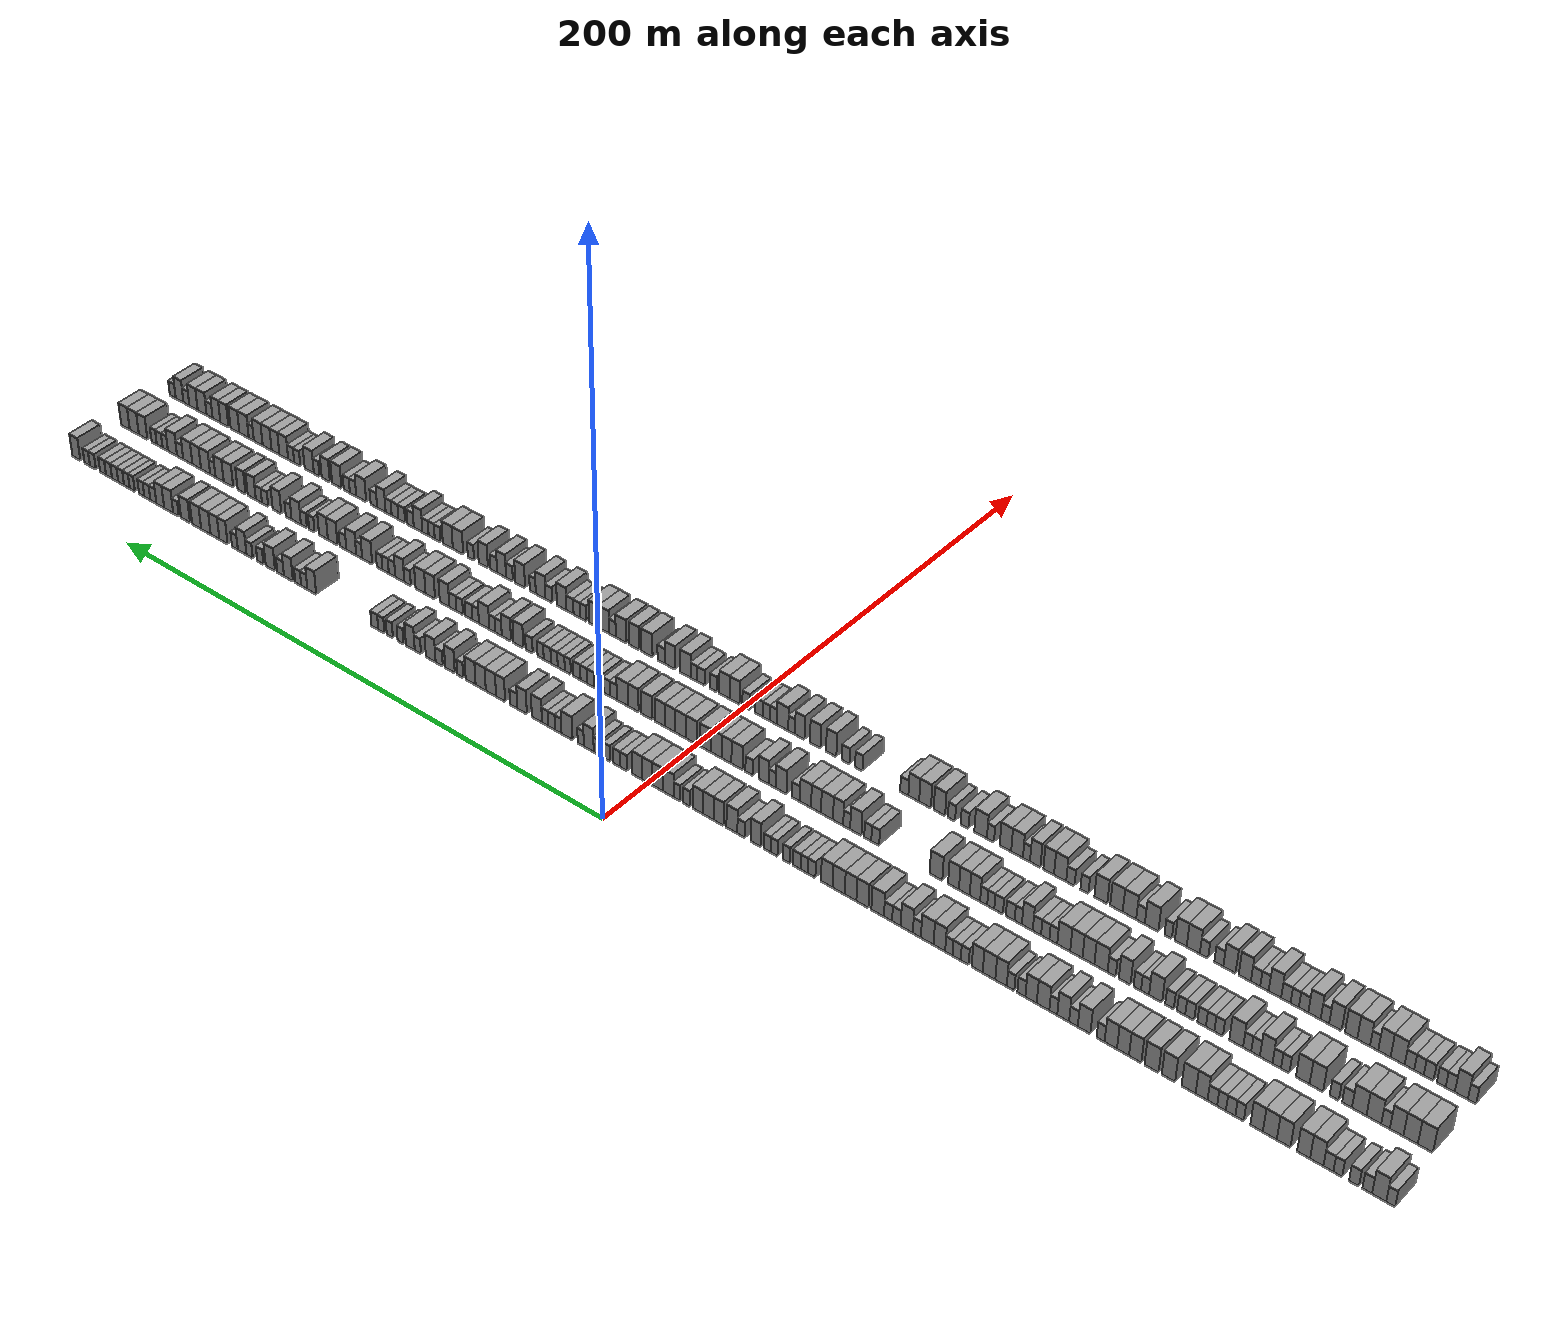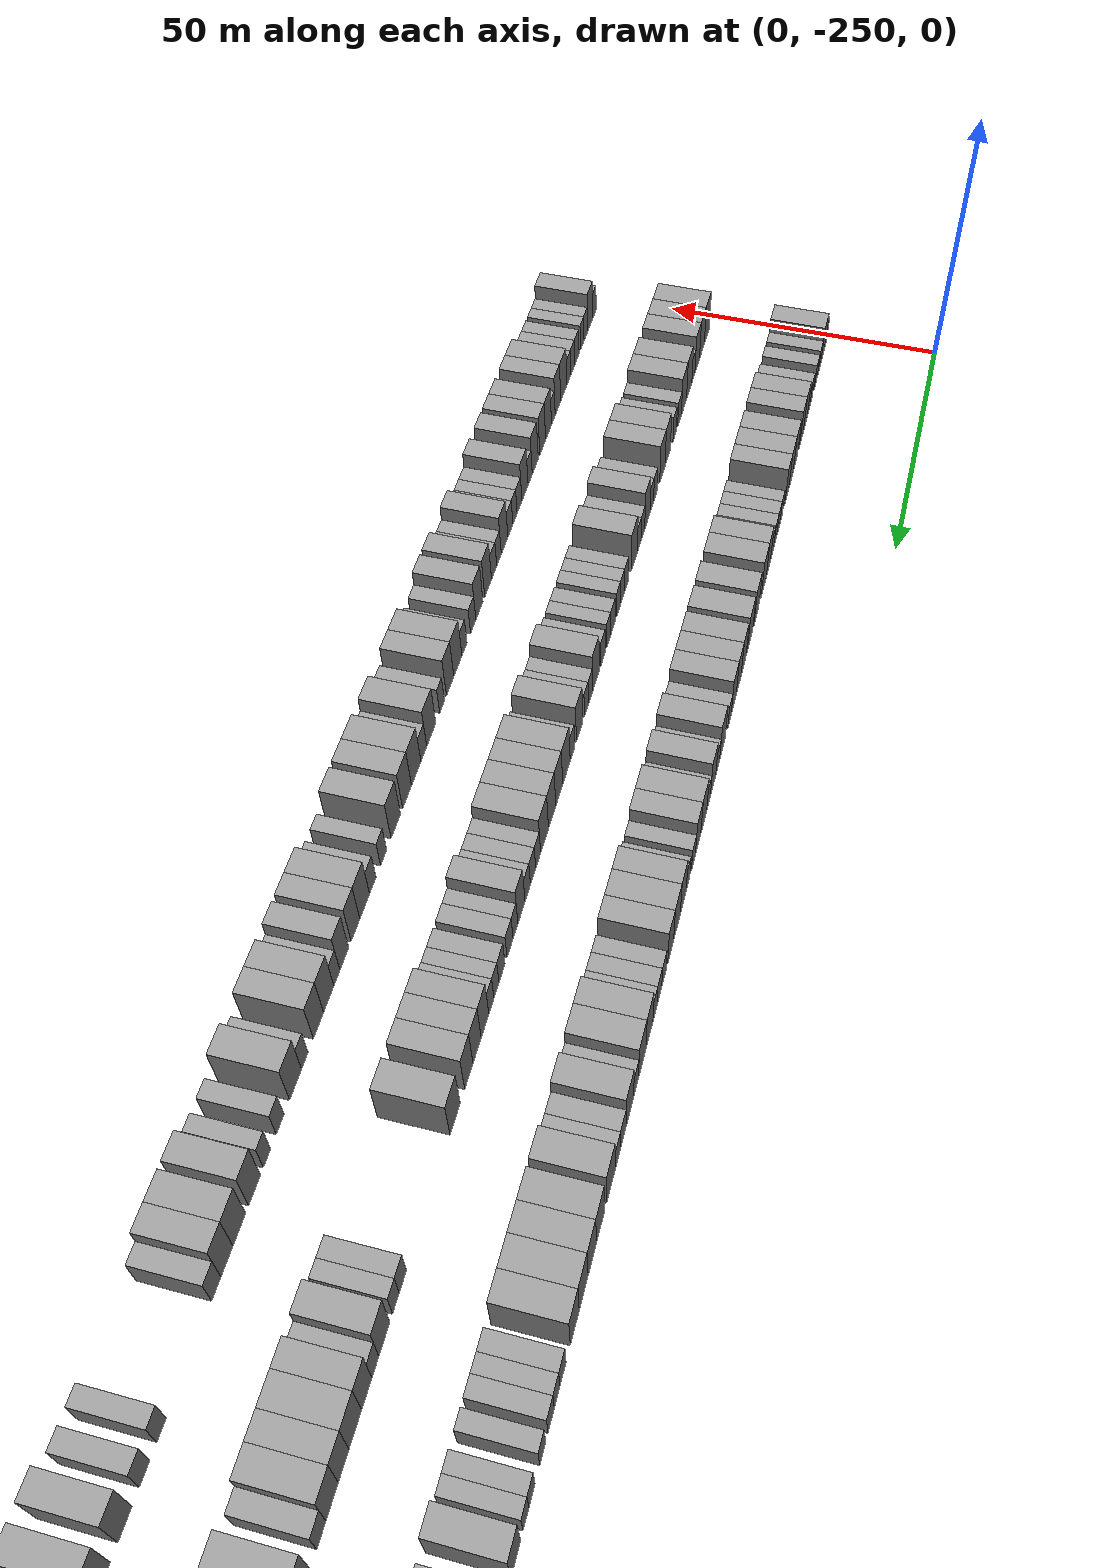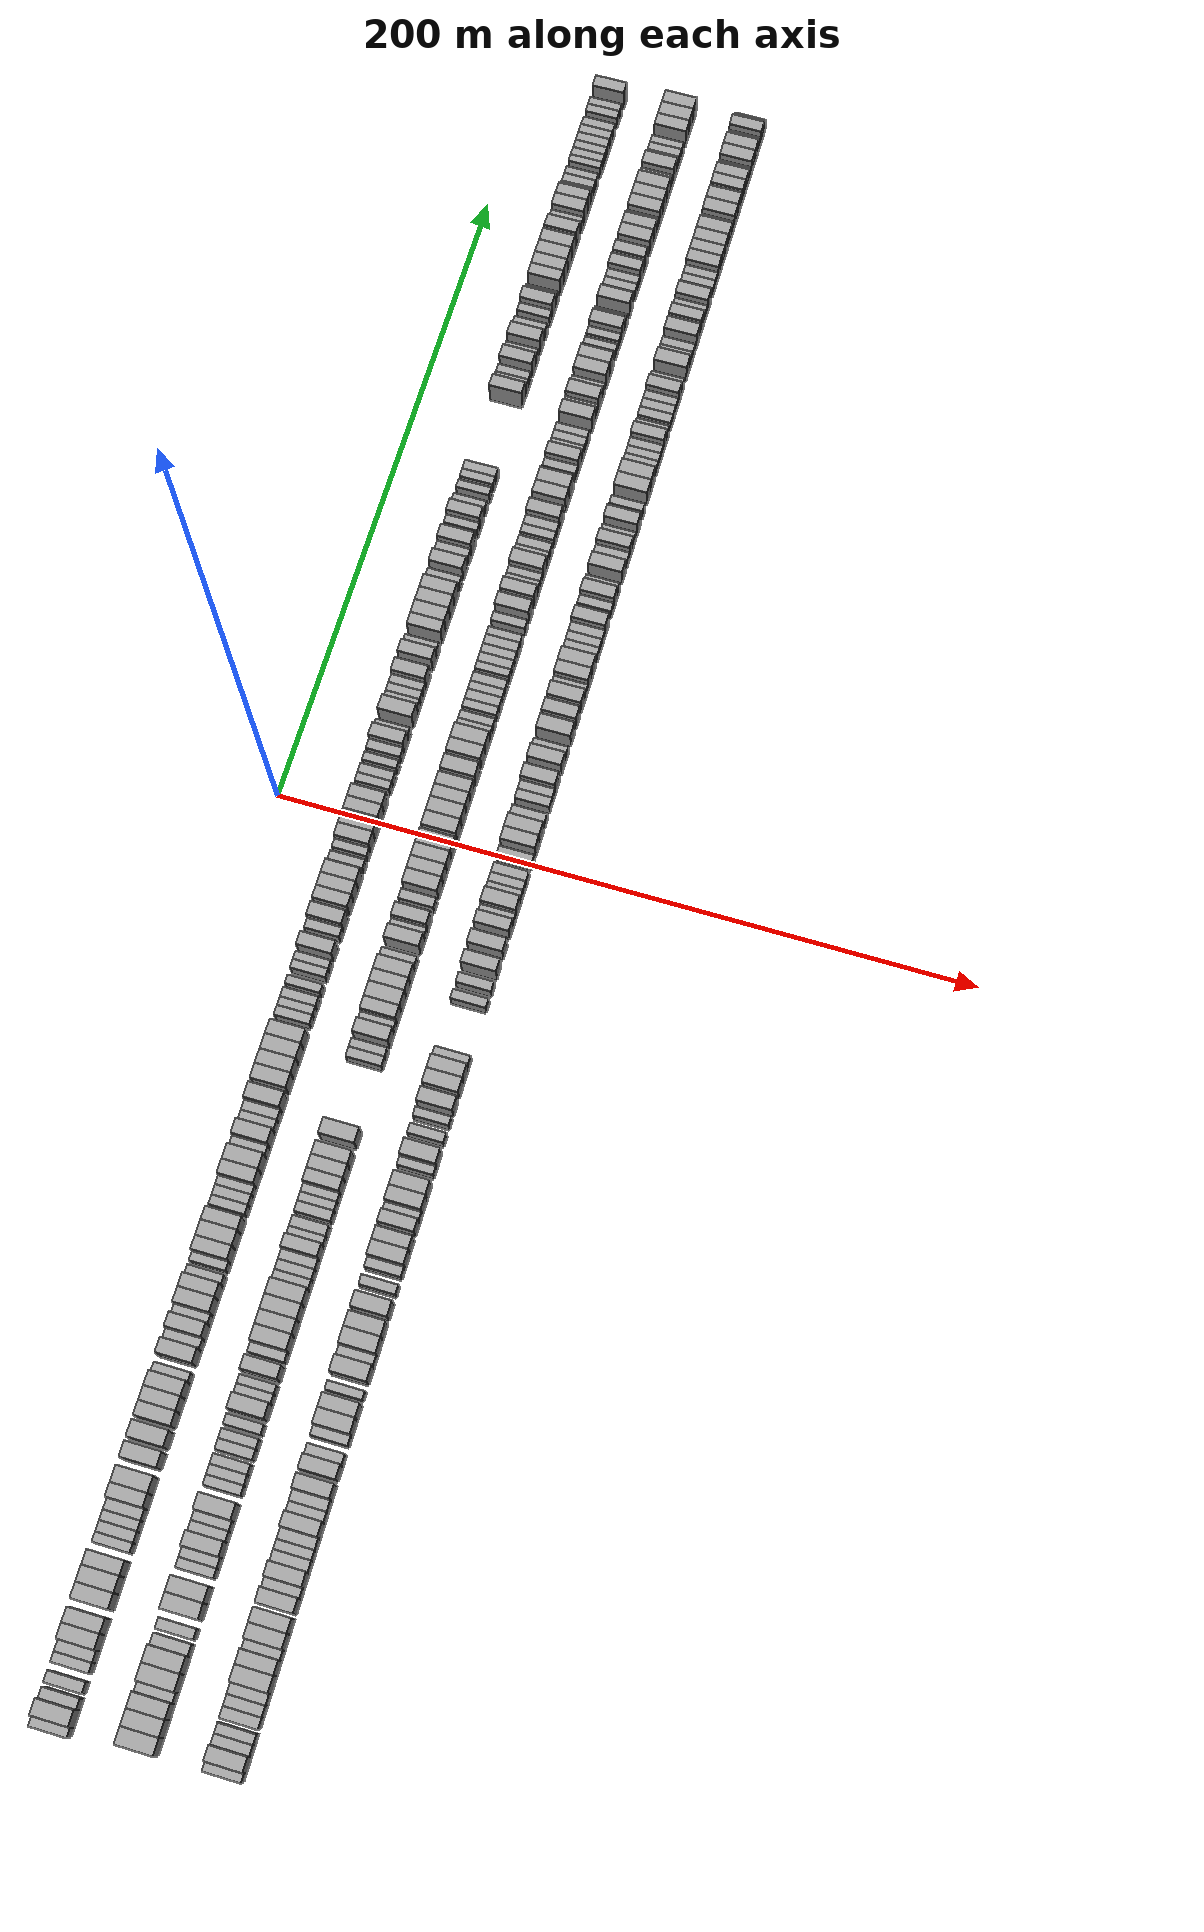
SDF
<sdf version="1.6">
 <world name="default">
  <scene>
   <sky><clouds><speed>12</speed></clouds></sky>
   <ambient>0.4 0.4 0.4 1</ambient>
   <background>0.7 0.7 0.7 1</background>
   <shadows>1</shadows>
  </scene>
  <gravity>0 0 -9.8066</gravity>
  <magnetic_field>6e-06 2.3e-05 -4.2e-05</magnetic_field>
  <physics default="0" name="default_physics" type="ode">
   <ode>
    <solver>
     <type>quick</type>
     <iters>10</iters>
     <sor>1.0</sor>
     <use_dynamic_moi_rescaling>0</use_dynamic_moi_rescaling>
    </solver>
    <constraints>
     <cfm>0</cfm>
     <erp>0.2</erp>
     <contact_max_correcting_vel>100</contact_max_correcting_vel>
     <contact_surface_layer>0.001</contact_surface_layer>
    </constraints>
   </ode>
   <max_step_size>0.004</max_step_size>
   <real_time_factor>1</real_time_factor>
   <real_time_update_rate>250</real_time_update_rate>
  </physics>
  <light name="sun" type="directional">
   <pose>0 0 10 0 0 0</pose>
   <diffuse>0.8 0.8 0.8 1</diffuse>
   <specular>0.2 0.2 0.2 1</specular>
   <attenuation>
    <range>1000</range>
    <constant>0.9</constant>
    <linear>0.01</linear>
    <quadratic>0.001</quadratic>
   </attenuation>
   <direction>-0.5 0.1 -0.9</direction>
  </light>
  <model name="building_1">
   <static>1</static>
   <pose>25.0000 -246.6970 0 0.000000 0.000000 0.000000</pose>
   <link name="link">
    <pose>0 0 3.00 0 0 0</pose>
    <collision name="collision"><geometry><box><size>10.0000 2.6060 6.0000</size></box></geometry></collision>
    <visual name="visual">
     <cast_shadows>0</cast_shadows>
     <geometry><box><size>10.0000 2.6060 6.0000</size></box></geometry>
     <material>
      <script>
       <uri>model://grey_wall/materials/scripts</uri>
       <uri>model://grey_wall/materials/textures</uri>
       <name>vrc/grey_wall</name>
      </script>
     </material>
    </visual>
   </link>
  </model>
  <model name="building_2">
   <static>1</static>
   <pose>25.0000 -243.3223 0 0.000000 0.000000 0.000000</pose>
   <link name="link">
    <pose>0 0 4.50 0 0 0</pose>
    <collision name="collision"><geometry><box><size>10.0000 4.1435 9.0000</size></box></geometry></collision>
    <visual name="visual">
     <cast_shadows>0</cast_shadows>
     <geometry><box><size>10.0000 4.1435 9.0000</size></box></geometry>
     <material>
      <script>
       <uri>model://grey_wall/materials/scripts</uri>
       <uri>model://grey_wall/materials/textures</uri>
       <name>vrc/grey_wall</name>
      </script>
     </material>
    </visual>
   </link>
  </model>
  <model name="building_3">
   <static>1</static>
   <pose>25.0000 -239.8434 0 0.000000 0.000000 0.000000</pose>
   <link name="link">
    <pose>0 0 3.00 0 0 0</pose>
    <collision name="collision"><geometry><box><size>10.0000 2.8142 6.0000</size></box></geometry></collision>
    <visual name="visual">
     <cast_shadows>0</cast_shadows>
     <geometry><box><size>10.0000 2.8142 6.0000</size></box></geometry>
     <material>
      <script>
       <uri>model://grey_wall/materials/scripts</uri>
       <uri>model://grey_wall/materials/textures</uri>
       <name>vrc/grey_wall</name>
      </script>
     </material>
    </visual>
   </link>
  </model>
  <model name="building_4">
   <static>1</static>
   <pose>25.0000 -235.9697 0 0.000000 0.000000 0.000000</pose>
   <link name="link">
    <pose>0 0 3.00 0 0 0</pose>
    <collision name="collision"><geometry><box><size>10.0000 2.9332 6.0000</size></box></geometry></collision>
    <visual name="visual">
     <cast_shadows>0</cast_shadows>
     <geometry><box><size>10.0000 2.9332 6.0000</size></box></geometry>
     <material>
      <script>
       <uri>model://grey_wall/materials/scripts</uri>
       <uri>model://grey_wall/materials/textures</uri>
       <name>vrc/grey_wall</name>
      </script>
     </material>
    </visual>
   </link>
  </model>
  <model name="building_5">
   <static>1</static>
   <pose>25.0000 -231.2033 0 0.000000 0.000000 0.000000</pose>
   <link name="link">
    <pose>0 0 3.00 0 0 0</pose>
    <collision name="collision"><geometry><box><size>10.0000 2.5995 6.0000</size></box></geometry></collision>
    <visual name="visual">
     <cast_shadows>0</cast_shadows>
     <geometry><box><size>10.0000 2.5995 6.0000</size></box></geometry>
     <material>
      <script>
       <uri>model://grey_wall/materials/scripts</uri>
       <uri>model://grey_wall/materials/textures</uri>
       <name>vrc/grey_wall</name>
      </script>
     </material>
    </visual>
   </link>
  </model>
  <model name="building_6">
   <static>1</static>
   <pose>25.0000 -228.4202 0 0.000000 0.000000 0.000000</pose>
   <link name="link">
    <pose>0 0 3.00 0 0 0</pose>
    <collision name="collision"><geometry><box><size>10.0000 2.9668 6.0000</size></box></geometry></collision>
    <visual name="visual">
     <cast_shadows>0</cast_shadows>
     <geometry><box><size>10.0000 2.9668 6.0000</size></box></geometry>
     <material>
      <script>
       <uri>model://grey_wall/materials/scripts</uri>
       <uri>model://grey_wall/materials/textures</uri>
       <name>vrc/grey_wall</name>
      </script>
     </material>
    </visual>
   </link>
  </model>
  <model name="building_7">
   <static>1</static>
   <pose>25.0000 -224.9501 0 0.000000 0.000000 0.000000</pose>
   <link name="link">
    <pose>0 0 4.50 0 0 0</pose>
    <collision name="collision"><geometry><box><size>10.0000 3.9732 9.0000</size></box></geometry></collision>
    <visual name="visual">
     <cast_shadows>0</cast_shadows>
     <geometry><box><size>10.0000 3.9732 9.0000</size></box></geometry>
     <material>
      <script>
       <uri>model://grey_wall/materials/scripts</uri>
       <uri>model://grey_wall/materials/textures</uri>
       <name>vrc/grey_wall</name>
      </script>
     </material>
    </visual>
   </link>
  </model>
  <model name="building_8">
   <static>1</static>
   <pose>25.0000 -221.0262 0 0.000000 0.000000 0.000000</pose>
   <link name="link">
    <pose>0 0 4.50 0 0 0</pose>
    <collision name="collision"><geometry><box><size>10.0000 3.8746 9.0000</size></box></geometry></collision>
    <visual name="visual">
     <cast_shadows>0</cast_shadows>
     <geometry><box><size>10.0000 3.8746 9.0000</size></box></geometry>
     <material>
      <script>
       <uri>model://grey_wall/materials/scripts</uri>
       <uri>model://grey_wall/materials/textures</uri>
       <name>vrc/grey_wall</name>
      </script>
     </material>
    </visual>
   </link>
  </model>
  <model name="building_9">
   <static>1</static>
   <pose>25.0000 -215.0378 0 0.000000 0.000000 0.000000</pose>
   <link name="link">
    <pose>0 0 4.50 0 0 0</pose>
    <collision name="collision"><geometry><box><size>10.0000 4.1022 9.0000</size></box></geometry></collision>
    <visual name="visual">
     <cast_shadows>0</cast_shadows>
     <geometry><box><size>10.0000 4.1022 9.0000</size></box></geometry>
     <material>
      <script>
       <uri>model://grey_wall/materials/scripts</uri>
       <uri>model://grey_wall/materials/textures</uri>
       <name>vrc/grey_wall</name>
      </script>
     </material>
    </visual>
   </link>
  </model>
  <model name="building_10">
   <static>1</static>
   <pose>25.0000 -210.8659 0 0.000000 0.000000 0.000000</pose>
   <link name="link">
    <pose>0 0 4.50 0 0 0</pose>
    <collision name="collision"><geometry><box><size>10.0000 4.2416 9.0000</size></box></geometry></collision>
    <visual name="visual">
     <cast_shadows>0</cast_shadows>
     <geometry><box><size>10.0000 4.2416 9.0000</size></box></geometry>
     <material>
      <script>
       <uri>model://grey_wall/materials/scripts</uri>
       <uri>model://grey_wall/materials/textures</uri>
       <name>vrc/grey_wall</name>
      </script>
     </material>
    </visual>
   </link>
  </model>
  <model name="building_11">
   <static>1</static>
   <pose>25.0000 -206.8452 0 0.000000 0.000000 0.000000</pose>
   <link name="link">
    <pose>0 0 4.50 0 0 0</pose>
    <collision name="collision"><geometry><box><size>10.0000 3.7999 9.0000</size></box></geometry></collision>
    <visual name="visual">
     <cast_shadows>0</cast_shadows>
     <geometry><box><size>10.0000 3.7999 9.0000</size></box></geometry>
     <material>
      <script>
       <uri>model://grey_wall/materials/scripts</uri>
       <uri>model://grey_wall/materials/textures</uri>
       <name>vrc/grey_wall</name>
      </script>
     </material>
    </visual>
   </link>
  </model>
  <model name="building_12">
   <static>1</static>
   <pose>25.0000 -201.6566 0 0.000000 0.000000 0.000000</pose>
   <link name="link">
    <pose>0 0 3.00 0 0 0</pose>
    <collision name="collision"><geometry><box><size>10.0000 2.5771 6.0000</size></box></geometry></collision>
    <visual name="visual">
     <cast_shadows>0</cast_shadows>
     <geometry><box><size>10.0000 2.5771 6.0000</size></box></geometry>
     <material>
      <script>
       <uri>model://grey_wall/materials/scripts</uri>
       <uri>model://grey_wall/materials/textures</uri>
       <name>vrc/grey_wall</name>
      </script>
     </material>
    </visual>
   </link>
  </model>
  <model name="building_13">
   <static>1</static>
   <pose>25.0000 -198.9184 0 0.000000 0.000000 0.000000</pose>
   <link name="link">
    <pose>0 0 3.00 0 0 0</pose>
    <collision name="collision"><geometry><box><size>10.0000 2.8992 6.0000</size></box></geometry></collision>
    <visual name="visual">
     <cast_shadows>0</cast_shadows>
     <geometry><box><size>10.0000 2.8992 6.0000</size></box></geometry>
     <material>
      <script>
       <uri>model://grey_wall/materials/scripts</uri>
       <uri>model://grey_wall/materials/textures</uri>
       <name>vrc/grey_wall</name>
      </script>
     </material>
    </visual>
   </link>
  </model>
  <model name="building_14">
   <static>1</static>
   <pose>25.0000 -196.1266 0 0.000000 0.000000 0.000000</pose>
   <link name="link">
    <pose>0 0 3.00 0 0 0</pose>
    <collision name="collision"><geometry><box><size>10.0000 2.6846 6.0000</size></box></geometry></collision>
    <visual name="visual">
     <cast_shadows>0</cast_shadows>
     <geometry><box><size>10.0000 2.6846 6.0000</size></box></geometry>
     <material>
      <script>
       <uri>model://grey_wall/materials/scripts</uri>
       <uri>model://grey_wall/materials/textures</uri>
       <name>vrc/grey_wall</name>
      </script>
     </material>
    </visual>
   </link>
  </model>
  <model name="building_15">
   <static>1</static>
   <pose>25.0000 -193.3024 0 0.000000 0.000000 0.000000</pose>
   <link name="link">
    <pose>0 0 3.00 0 0 0</pose>
    <collision name="collision"><geometry><box><size>10.0000 2.9638 6.0000</size></box></geometry></collision>
    <visual name="visual">
     <cast_shadows>0</cast_shadows>
     <geometry><box><size>10.0000 2.9638 6.0000</size></box></geometry>
     <material>
      <script>
       <uri>model://grey_wall/materials/scripts</uri>
       <uri>model://grey_wall/materials/textures</uri>
       <name>vrc/grey_wall</name>
      </script>
     </material>
    </visual>
   </link>
  </model>
  <model name="building_16">
   <static>1</static>
   <pose>25.0000 -189.9717 0 0.000000 0.000000 0.000000</pose>
   <link name="link">
    <pose>0 0 4.50 0 0 0</pose>
    <collision name="collision"><geometry><box><size>10.0000 3.6975 9.0000</size></box></geometry></collision>
    <visual name="visual">
     <cast_shadows>0</cast_shadows>
     <geometry><box><size>10.0000 3.6975 9.0000</size></box></geometry>
     <material>
      <script>
       <uri>model://grey_wall/materials/scripts</uri>
       <uri>model://grey_wall/materials/textures</uri>
       <name>vrc/grey_wall</name>
      </script>
     </material>
    </visual>
   </link>
  </model>
  <model name="building_17">
   <static>1</static>
   <pose>25.0000 -185.9258 0 0.000000 0.000000 0.000000</pose>
   <link name="link">
    <pose>0 0 4.50 0 0 0</pose>
    <collision name="collision"><geometry><box><size>10.0000 4.3942 9.0000</size></box></geometry></collision>
    <visual name="visual">
     <cast_shadows>0</cast_shadows>
     <geometry><box><size>10.0000 4.3942 9.0000</size></box></geometry>
     <material>
      <script>
       <uri>model://grey_wall/materials/scripts</uri>
       <uri>model://grey_wall/materials/textures</uri>
       <name>vrc/grey_wall</name>
      </script>
     </material>
    </visual>
   </link>
  </model>
  <model name="building_18">
   <static>1</static>
   <pose>25.0000 -179.6303 0 0.000000 0.000000 0.000000</pose>
   <link name="link">
    <pose>0 0 4.50 0 0 0</pose>
    <collision name="collision"><geometry><box><size>10.0000 4.1968 9.0000</size></box></geometry></collision>
    <visual name="visual">
     <cast_shadows>0</cast_shadows>
     <geometry><box><size>10.0000 4.1968 9.0000</size></box></geometry>
     <material>
      <script>
       <uri>model://grey_wall/materials/scripts</uri>
       <uri>model://grey_wall/materials/textures</uri>
       <name>vrc/grey_wall</name>
      </script>
     </material>
    </visual>
   </link>
  </model>
  <model name="building_19">
   <static>1</static>
   <pose>25.0000 -174.3043 0 0.000000 0.000000 0.000000</pose>
   <link name="link">
    <pose>0 0 4.50 0 0 0</pose>
    <collision name="collision"><geometry><box><size>10.0000 4.4552 9.0000</size></box></geometry></collision>
    <visual name="visual">
     <cast_shadows>0</cast_shadows>
     <geometry><box><size>10.0000 4.4552 9.0000</size></box></geometry>
     <material>
      <script>
       <uri>model://grey_wall/materials/scripts</uri>
       <uri>model://grey_wall/materials/textures</uri>
       <name>vrc/grey_wall</name>
      </script>
     </material>
    </visual>
   </link>
  </model>
  <model name="building_20">
   <static>1</static>
   <pose>25.0000 -169.1178 0 0.000000 0.000000 0.000000</pose>
   <link name="link">
    <pose>0 0 4.50 0 0 0</pose>
    <collision name="collision"><geometry><box><size>10.0000 3.9179 9.0000</size></box></geometry></collision>
    <visual name="visual">
     <cast_shadows>0</cast_shadows>
     <geometry><box><size>10.0000 3.9179 9.0000</size></box></geometry>
     <material>
      <script>
       <uri>model://grey_wall/materials/scripts</uri>
       <uri>model://grey_wall/materials/textures</uri>
       <name>vrc/grey_wall</name>
      </script>
     </material>
    </visual>
   </link>
  </model>
  <model name="building_21">
   <static>1</static>
   <pose>25.0000 -165.2449 0 0.000000 0.000000 0.000000</pose>
   <link name="link">
    <pose>0 0 4.50 0 0 0</pose>
    <collision name="collision"><geometry><box><size>10.0000 3.8280 9.0000</size></box></geometry></collision>
    <visual name="visual">
     <cast_shadows>0</cast_shadows>
     <geometry><box><size>10.0000 3.8280 9.0000</size></box></geometry>
     <material>
      <script>
       <uri>model://grey_wall/materials/scripts</uri>
       <uri>model://grey_wall/materials/textures</uri>
       <name>vrc/grey_wall</name>
      </script>
     </material>
    </visual>
   </link>
  </model>
  <model name="building_22">
   <static>1</static>
   <pose>25.0000 -161.3440 0 0.000000 0.000000 0.000000</pose>
   <link name="link">
    <pose>0 0 4.50 0 0 0</pose>
    <collision name="collision"><geometry><box><size>10.0000 3.9738 9.0000</size></box></geometry></collision>
    <visual name="visual">
     <cast_shadows>0</cast_shadows>
     <geometry><box><size>10.0000 3.9738 9.0000</size></box></geometry>
     <material>
      <script>
       <uri>model://grey_wall/materials/scripts</uri>
       <uri>model://grey_wall/materials/textures</uri>
       <name>vrc/grey_wall</name>
      </script>
     </material>
    </visual>
   </link>
  </model>
  <model name="building_23">
   <static>1</static>
   <pose>25.0000 -158.0768 0 0.000000 0.000000 0.000000</pose>
   <link name="link">
    <pose>0 0 3.00 0 0 0</pose>
    <collision name="collision"><geometry><box><size>10.0000 2.5608 6.0000</size></box></geometry></collision>
    <visual name="visual">
     <cast_shadows>0</cast_shadows>
     <geometry><box><size>10.0000 2.5608 6.0000</size></box></geometry>
     <material>
      <script>
       <uri>model://grey_wall/materials/scripts</uri>
       <uri>model://grey_wall/materials/textures</uri>
       <name>vrc/grey_wall</name>
      </script>
     </material>
    </visual>
   </link>
  </model>
  <model name="building_24">
   <static>1</static>
   <pose>25.0000 -152.7479 0 0.000000 0.000000 0.000000</pose>
   <link name="link">
    <pose>0 0 4.50 0 0 0</pose>
    <collision name="collision"><geometry><box><size>10.0000 4.0969 9.0000</size></box></geometry></collision>
    <visual name="visual">
     <cast_shadows>0</cast_shadows>
     <geometry><box><size>10.0000 4.0969 9.0000</size></box></geometry>
     <material>
      <script>
       <uri>model://grey_wall/materials/scripts</uri>
       <uri>model://grey_wall/materials/textures</uri>
       <name>vrc/grey_wall</name>
      </script>
     </material>
    </visual>
   </link>
  </model>
  <model name="building_25">
   <static>1</static>
   <pose>25.0000 -149.2939 0 0.000000 0.000000 0.000000</pose>
   <link name="link">
    <pose>0 0 3.00 0 0 0</pose>
    <collision name="collision"><geometry><box><size>10.0000 2.8112 6.0000</size></box></geometry></collision>
    <visual name="visual">
     <cast_shadows>0</cast_shadows>
     <geometry><box><size>10.0000 2.8112 6.0000</size></box></geometry>
     <material>
      <script>
       <uri>model://grey_wall/materials/scripts</uri>
       <uri>model://grey_wall/materials/textures</uri>
       <name>vrc/grey_wall</name>
      </script>
     </material>
    </visual>
   </link>
  </model>
  <model name="building_26">
   <static>1</static>
   <pose>25.0000 -145.9537 0 0.000000 0.000000 0.000000</pose>
   <link name="link">
    <pose>0 0 4.50 0 0 0</pose>
    <collision name="collision"><geometry><box><size>10.0000 3.8691 9.0000</size></box></geometry></collision>
    <visual name="visual">
     <cast_shadows>0</cast_shadows>
     <geometry><box><size>10.0000 3.8691 9.0000</size></box></geometry>
     <material>
      <script>
       <uri>model://grey_wall/materials/scripts</uri>
       <uri>model://grey_wall/materials/textures</uri>
       <name>vrc/grey_wall</name>
      </script>
     </material>
    </visual>
   </link>
  </model>
  <model name="building_27">
   <static>1</static>
   <pose>25.0000 -142.7333 0 0.000000 0.000000 0.000000</pose>
   <link name="link">
    <pose>0 0 3.00 0 0 0</pose>
    <collision name="collision"><geometry><box><size>10.0000 2.5717 6.0000</size></box></geometry></collision>
    <visual name="visual">
     <cast_shadows>0</cast_shadows>
     <geometry><box><size>10.0000 2.5717 6.0000</size></box></geometry>
     <material>
      <script>
       <uri>model://grey_wall/materials/scripts</uri>
       <uri>model://grey_wall/materials/textures</uri>
       <name>vrc/grey_wall</name>
      </script>
     </material>
    </visual>
   </link>
  </model>
  <model name="building_28">
   <static>1</static>
   <pose>25.0000 -139.3684 0 0.000000 0.000000 0.000000</pose>
   <link name="link">
    <pose>0 0 4.50 0 0 0</pose>
    <collision name="collision"><geometry><box><size>10.0000 4.1580 9.0000</size></box></geometry></collision>
    <visual name="visual">
     <cast_shadows>0</cast_shadows>
     <geometry><box><size>10.0000 4.1580 9.0000</size></box></geometry>
     <material>
      <script>
       <uri>model://grey_wall/materials/scripts</uri>
       <uri>model://grey_wall/materials/textures</uri>
       <name>vrc/grey_wall</name>
      </script>
     </material>
    </visual>
   </link>
  </model>
  <model name="building_29">
   <static>1</static>
   <pose>25.0000 -135.4226 0 0.000000 0.000000 0.000000</pose>
   <link name="link">
    <pose>0 0 4.50 0 0 0</pose>
    <collision name="collision"><geometry><box><size>10.0000 3.7335 9.0000</size></box></geometry></collision>
    <visual name="visual">
     <cast_shadows>0</cast_shadows>
     <geometry><box><size>10.0000 3.7335 9.0000</size></box></geometry>
     <material>
      <script>
       <uri>model://grey_wall/materials/scripts</uri>
       <uri>model://grey_wall/materials/textures</uri>
       <name>vrc/grey_wall</name>
      </script>
     </material>
    </visual>
   </link>
  </model>
  <model name="building_30">
   <static>1</static>
   <pose>25.0000 -132.2289 0 0.000000 0.000000 0.000000</pose>
   <link name="link">
    <pose>0 0 3.00 0 0 0</pose>
    <collision name="collision"><geometry><box><size>10.0000 2.6539 6.0000</size></box></geometry></collision>
    <visual name="visual">
     <cast_shadows>0</cast_shadows>
     <geometry><box><size>10.0000 2.6539 6.0000</size></box></geometry>
     <material>
      <script>
       <uri>model://grey_wall/materials/scripts</uri>
       <uri>model://grey_wall/materials/textures</uri>
       <name>vrc/grey_wall</name>
      </script>
     </material>
    </visual>
   </link>
  </model>
  <model name="building_31">
   <static>1</static>
   <pose>25.0000 -128.6428 0 0.000000 0.000000 0.000000</pose>
   <link name="link">
    <pose>0 0 3.00 0 0 0</pose>
    <collision name="collision"><geometry><box><size>10.0000 2.5184 6.0000</size></box></geometry></collision>
    <visual name="visual">
     <cast_shadows>0</cast_shadows>
     <geometry><box><size>10.0000 2.5184 6.0000</size></box></geometry>
     <material>
      <script>
       <uri>model://grey_wall/materials/scripts</uri>
       <uri>model://grey_wall/materials/textures</uri>
       <name>vrc/grey_wall</name>
      </script>
     </material>
    </visual>
   </link>
  </model>
  <model name="building_32">
   <static>1</static>
   <pose>25.0000 -125.4761 0 0.000000 0.000000 0.000000</pose>
   <link name="link">
    <pose>0 0 4.50 0 0 0</pose>
    <collision name="collision"><geometry><box><size>10.0000 3.8151 9.0000</size></box></geometry></collision>
    <visual name="visual">
     <cast_shadows>0</cast_shadows>
     <geometry><box><size>10.0000 3.8151 9.0000</size></box></geometry>
     <material>
      <script>
       <uri>model://grey_wall/materials/scripts</uri>
       <uri>model://grey_wall/materials/textures</uri>
       <name>vrc/grey_wall</name>
      </script>
     </material>
    </visual>
   </link>
  </model>
  <model name="building_33">
   <static>1</static>
   <pose>25.0000 -121.4594 0 0.000000 0.000000 0.000000</pose>
   <link name="link">
    <pose>0 0 4.50 0 0 0</pose>
    <collision name="collision"><geometry><box><size>10.0000 4.2183 9.0000</size></box></geometry></collision>
    <visual name="visual">
     <cast_shadows>0</cast_shadows>
     <geometry><box><size>10.0000 4.2183 9.0000</size></box></geometry>
     <material>
      <script>
       <uri>model://grey_wall/materials/scripts</uri>
       <uri>model://grey_wall/materials/textures</uri>
       <name>vrc/grey_wall</name>
      </script>
     </material>
    </visual>
   </link>
  </model>
  <model name="building_34">
   <static>1</static>
   <pose>25.0000 -117.4892 0 0.000000 0.000000 0.000000</pose>
   <link name="link">
    <pose>0 0 4.50 0 0 0</pose>
    <collision name="collision"><geometry><box><size>10.0000 3.7220 9.0000</size></box></geometry></collision>
    <visual name="visual">
     <cast_shadows>0</cast_shadows>
     <geometry><box><size>10.0000 3.7220 9.0000</size></box></geometry>
     <material>
      <script>
       <uri>model://grey_wall/materials/scripts</uri>
       <uri>model://grey_wall/materials/textures</uri>
       <name>vrc/grey_wall</name>
      </script>
     </material>
    </visual>
   </link>
  </model>
  <model name="building_35">
   <static>1</static>
   <pose>25.0000 -113.2872 0 0.000000 0.000000 0.000000</pose>
   <link name="link">
    <pose>0 0 3.00 0 0 0</pose>
    <collision name="collision"><geometry><box><size>10.0000 2.6820 6.0000</size></box></geometry></collision>
    <visual name="visual">
     <cast_shadows>0</cast_shadows>
     <geometry><box><size>10.0000 2.6820 6.0000</size></box></geometry>
     <material>
      <script>
       <uri>model://grey_wall/materials/scripts</uri>
       <uri>model://grey_wall/materials/textures</uri>
       <name>vrc/grey_wall</name>
      </script>
     </material>
    </visual>
   </link>
  </model>
  <model name="building_36">
   <static>1</static>
   <pose>25.0000 -110.5451 0 0.000000 0.000000 0.000000</pose>
   <link name="link">
    <pose>0 0 3.00 0 0 0</pose>
    <collision name="collision"><geometry><box><size>10.0000 2.8020 6.0000</size></box></geometry></collision>
    <visual name="visual">
     <cast_shadows>0</cast_shadows>
     <geometry><box><size>10.0000 2.8020 6.0000</size></box></geometry>
     <material>
      <script>
       <uri>model://grey_wall/materials/scripts</uri>
       <uri>model://grey_wall/materials/textures</uri>
       <name>vrc/grey_wall</name>
      </script>
     </material>
    </visual>
   </link>
  </model>
  <model name="building_37">
   <static>1</static>
   <pose>25.0000 -107.9055 0 0.000000 0.000000 0.000000</pose>
   <link name="link">
    <pose>0 0 3.00 0 0 0</pose>
    <collision name="collision"><geometry><box><size>10.0000 2.4773 6.0000</size></box></geometry></collision>
    <visual name="visual">
     <cast_shadows>0</cast_shadows>
     <geometry><box><size>10.0000 2.4773 6.0000</size></box></geometry>
     <material>
      <script>
       <uri>model://grey_wall/materials/scripts</uri>
       <uri>model://grey_wall/materials/textures</uri>
       <name>vrc/grey_wall</name>
      </script>
     </material>
    </visual>
   </link>
  </model>
  <model name="building_38">
   <static>1</static>
   <pose>25.0000 -104.6841 0 0.000000 0.000000 0.000000</pose>
   <link name="link">
    <pose>0 0 4.50 0 0 0</pose>
    <collision name="collision"><geometry><box><size>10.0000 3.9654 9.0000</size></box></geometry></collision>
    <visual name="visual">
     <cast_shadows>0</cast_shadows>
     <geometry><box><size>10.0000 3.9654 9.0000</size></box></geometry>
     <material>
      <script>
       <uri>model://grey_wall/materials/scripts</uri>
       <uri>model://grey_wall/materials/textures</uri>
       <name>vrc/grey_wall</name>
      </script>
     </material>
    </visual>
   </link>
  </model>
  <model name="building_39">
   <static>1</static>
   <pose>25.0000 -100.5283 0 0.000000 0.000000 0.000000</pose>
   <link name="link">
    <pose>0 0 4.50 0 0 0</pose>
    <collision name="collision"><geometry><box><size>10.0000 4.3463 9.0000</size></box></geometry></collision>
    <visual name="visual">
     <cast_shadows>0</cast_shadows>
     <geometry><box><size>10.0000 4.3463 9.0000</size></box></geometry>
     <material>
      <script>
       <uri>model://grey_wall/materials/scripts</uri>
       <uri>model://grey_wall/materials/textures</uri>
       <name>vrc/grey_wall</name>
      </script>
     </material>
    </visual>
   </link>
  </model>
  <model name="building_40">
   <static>1</static>
   <pose>25.0000 -96.9759 0 0.000000 0.000000 0.000000</pose>
   <link name="link">
    <pose>0 0 3.00 0 0 0</pose>
    <collision name="collision"><geometry><box><size>10.0000 2.7586 6.0000</size></box></geometry></collision>
    <visual name="visual">
     <cast_shadows>0</cast_shadows>
     <geometry><box><size>10.0000 2.7586 6.0000</size></box></geometry>
     <material>
      <script>
       <uri>model://grey_wall/materials/scripts</uri>
       <uri>model://grey_wall/materials/textures</uri>
       <name>vrc/grey_wall</name>
      </script>
     </material>
    </visual>
   </link>
  </model>
  <model name="building_41">
   <static>1</static>
   <pose>25.0000 -93.4938 0 0.000000 0.000000 0.000000</pose>
   <link name="link">
    <pose>0 0 4.50 0 0 0</pose>
    <collision name="collision"><geometry><box><size>10.0000 4.2056 9.0000</size></box></geometry></collision>
    <visual name="visual">
     <cast_shadows>0</cast_shadows>
     <geometry><box><size>10.0000 4.2056 9.0000</size></box></geometry>
     <material>
      <script>
       <uri>model://grey_wall/materials/scripts</uri>
       <uri>model://grey_wall/materials/textures</uri>
       <name>vrc/grey_wall</name>
      </script>
     </material>
    </visual>
   </link>
  </model>
  <model name="building_42">
   <static>1</static>
   <pose>25.0000 -89.9001 0 0.000000 0.000000 0.000000</pose>
   <link name="link">
    <pose>0 0 3.00 0 0 0</pose>
    <collision name="collision"><geometry><box><size>10.0000 2.9819 6.0000</size></box></geometry></collision>
    <visual name="visual">
     <cast_shadows>0</cast_shadows>
     <geometry><box><size>10.0000 2.9819 6.0000</size></box></geometry>
     <material>
      <script>
       <uri>model://grey_wall/materials/scripts</uri>
       <uri>model://grey_wall/materials/textures</uri>
       <name>vrc/grey_wall</name>
      </script>
     </material>
    </visual>
   </link>
  </model>
  <model name="building_43">
   <static>1</static>
   <pose>25.0000 -86.9947 0 0.000000 0.000000 0.000000</pose>
   <link name="link">
    <pose>0 0 3.00 0 0 0</pose>
    <collision name="collision"><geometry><box><size>10.0000 2.8288 6.0000</size></box></geometry></collision>
    <visual name="visual">
     <cast_shadows>0</cast_shadows>
     <geometry><box><size>10.0000 2.8288 6.0000</size></box></geometry>
     <material>
      <script>
       <uri>model://grey_wall/materials/scripts</uri>
       <uri>model://grey_wall/materials/textures</uri>
       <name>vrc/grey_wall</name>
      </script>
     </material>
    </visual>
   </link>
  </model>
  <model name="building_44">
   <static>1</static>
   <pose>25.0000 -83.3818 0 0.000000 0.000000 0.000000</pose>
   <link name="link">
    <pose>0 0 4.50 0 0 0</pose>
    <collision name="collision"><geometry><box><size>10.0000 4.3971 9.0000</size></box></geometry></collision>
    <visual name="visual">
     <cast_shadows>0</cast_shadows>
     <geometry><box><size>10.0000 4.3971 9.0000</size></box></geometry>
     <material>
      <script>
       <uri>model://grey_wall/materials/scripts</uri>
       <uri>model://grey_wall/materials/textures</uri>
       <name>vrc/grey_wall</name>
      </script>
     </material>
    </visual>
   </link>
  </model>
  <model name="building_45">
   <static>1</static>
   <pose>25.0000 -78.0550 0 0.000000 0.000000 0.000000</pose>
   <link name="link">
    <pose>0 0 4.50 0 0 0</pose>
    <collision name="collision"><geometry><box><size>10.0000 4.2565 9.0000</size></box></geometry></collision>
    <visual name="visual">
     <cast_shadows>0</cast_shadows>
     <geometry><box><size>10.0000 4.2565 9.0000</size></box></geometry>
     <material>
      <script>
       <uri>model://grey_wall/materials/scripts</uri>
       <uri>model://grey_wall/materials/textures</uri>
       <name>vrc/grey_wall</name>
      </script>
     </material>
    </visual>
   </link>
  </model>
  <model name="building_46">
   <static>1</static>
   <pose>25.0000 -73.8800 0 0.000000 0.000000 0.000000</pose>
   <link name="link">
    <pose>0 0 4.50 0 0 0</pose>
    <collision name="collision"><geometry><box><size>10.0000 4.0935 9.0000</size></box></geometry></collision>
    <visual name="visual">
     <cast_shadows>0</cast_shadows>
     <geometry><box><size>10.0000 4.0935 9.0000</size></box></geometry>
     <material>
      <script>
       <uri>model://grey_wall/materials/scripts</uri>
       <uri>model://grey_wall/materials/textures</uri>
       <name>vrc/grey_wall</name>
      </script>
     </material>
    </visual>
   </link>
  </model>
  <model name="building_47">
   <static>1</static>
   <pose>25.0000 -69.6777 0 0.000000 0.000000 0.000000</pose>
   <link name="link">
    <pose>0 0 4.50 0 0 0</pose>
    <collision name="collision"><geometry><box><size>10.0000 4.3112 9.0000</size></box></geometry></collision>
    <visual name="visual">
     <cast_shadows>0</cast_shadows>
     <geometry><box><size>10.0000 4.3112 9.0000</size></box></geometry>
     <material>
      <script>
       <uri>model://grey_wall/materials/scripts</uri>
       <uri>model://grey_wall/materials/textures</uri>
       <name>vrc/grey_wall</name>
      </script>
     </material>
    </visual>
   </link>
  </model>
  <model name="building_48">
   <static>1</static>
   <pose>25.0000 -65.4500 0 0.000000 0.000000 0.000000</pose>
   <link name="link">
    <pose>0 0 4.50 0 0 0</pose>
    <collision name="collision"><geometry><box><size>10.0000 4.1443 9.0000</size></box></geometry></collision>
    <visual name="visual">
     <cast_shadows>0</cast_shadows>
     <geometry><box><size>10.0000 4.1443 9.0000</size></box></geometry>
     <material>
      <script>
       <uri>model://grey_wall/materials/scripts</uri>
       <uri>model://grey_wall/materials/textures</uri>
       <name>vrc/grey_wall</name>
      </script>
     </material>
    </visual>
   </link>
  </model>
  <model name="building_49">
   <static>1</static>
   <pose>25.0000 -59.9845 0 0.000000 0.000000 0.000000</pose>
   <link name="link">
    <pose>0 0 3.00 0 0 0</pose>
    <collision name="collision"><geometry><box><size>10.0000 2.7867 6.0000</size></box></geometry></collision>
    <visual name="visual">
     <cast_shadows>0</cast_shadows>
     <geometry><box><size>10.0000 2.7867 6.0000</size></box></geometry>
     <material>
      <script>
       <uri>model://grey_wall/materials/scripts</uri>
       <uri>model://grey_wall/materials/textures</uri>
       <name>vrc/grey_wall</name>
      </script>
     </material>
    </visual>
   </link>
  </model>
  <model name="building_50">
   <static>1</static>
   <pose>25.0000 -57.3420 0 0.000000 0.000000 0.000000</pose>
   <link name="link">
    <pose>0 0 3.00 0 0 0</pose>
    <collision name="collision"><geometry><box><size>10.0000 2.4983 6.0000</size></box></geometry></collision>
    <visual name="visual">
     <cast_shadows>0</cast_shadows>
     <geometry><box><size>10.0000 2.4983 6.0000</size></box></geometry>
     <material>
      <script>
       <uri>model://grey_wall/materials/scripts</uri>
       <uri>model://grey_wall/materials/textures</uri>
       <name>vrc/grey_wall</name>
      </script>
     </material>
    </visual>
   </link>
  </model>
  <model name="building_51">
   <static>1</static>
   <pose>25.0000 -54.7018 0 0.000000 0.000000 0.000000</pose>
   <link name="link">
    <pose>0 0 3.00 0 0 0</pose>
    <collision name="collision"><geometry><box><size>10.0000 2.7822 6.0000</size></box></geometry></collision>
    <visual name="visual">
     <cast_shadows>0</cast_shadows>
     <geometry><box><size>10.0000 2.7822 6.0000</size></box></geometry>
     <material>
      <script>
       <uri>model://grey_wall/materials/scripts</uri>
       <uri>model://grey_wall/materials/textures</uri>
       <name>vrc/grey_wall</name>
      </script>
     </material>
    </visual>
   </link>
  </model>
  <model name="building_52">
   <static>1</static>
   <pose>25.0000 -51.0247 0 0.000000 0.000000 0.000000</pose>
   <link name="link">
    <pose>0 0 3.00 0 0 0</pose>
    <collision name="collision"><geometry><box><size>10.0000 2.5720 6.0000</size></box></geometry></collision>
    <visual name="visual">
     <cast_shadows>0</cast_shadows>
     <geometry><box><size>10.0000 2.5720 6.0000</size></box></geometry>
     <material>
      <script>
       <uri>model://grey_wall/materials/scripts</uri>
       <uri>model://grey_wall/materials/textures</uri>
       <name>vrc/grey_wall</name>
      </script>
     </material>
    </visual>
   </link>
  </model>
  <model name="building_53">
   <static>1</static>
   <pose>25.0000 -46.4626 0 0.000000 0.000000 0.000000</pose>
   <link name="link">
    <pose>0 0 3.00 0 0 0</pose>
    <collision name="collision"><geometry><box><size>10.0000 2.5521 6.0000</size></box></geometry></collision>
    <visual name="visual">
     <cast_shadows>0</cast_shadows>
     <geometry><box><size>10.0000 2.5521 6.0000</size></box></geometry>
     <material>
      <script>
       <uri>model://grey_wall/materials/scripts</uri>
       <uri>model://grey_wall/materials/textures</uri>
       <name>vrc/grey_wall</name>
      </script>
     </material>
    </visual>
   </link>
  </model>
  <model name="building_54">
   <static>1</static>
   <pose>25.0000 -43.9771 0 0.000000 0.000000 0.000000</pose>
   <link name="link">
    <pose>0 0 3.00 0 0 0</pose>
    <collision name="collision"><geometry><box><size>10.0000 2.4189 6.0000</size></box></geometry></collision>
    <visual name="visual">
     <cast_shadows>0</cast_shadows>
     <geometry><box><size>10.0000 2.4189 6.0000</size></box></geometry>
     <material>
      <script>
       <uri>model://grey_wall/materials/scripts</uri>
       <uri>model://grey_wall/materials/textures</uri>
       <name>vrc/grey_wall</name>
      </script>
     </material>
    </visual>
   </link>
  </model>
  <model name="building_55">
   <static>1</static>
   <pose>25.0000 -39.8528 0 0.000000 0.000000 0.000000</pose>
   <link name="link">
    <pose>0 0 4.50 0 0 0</pose>
    <collision name="collision"><geometry><box><size>10.0000 3.8297 9.0000</size></box></geometry></collision>
    <visual name="visual">
     <cast_shadows>0</cast_shadows>
     <geometry><box><size>10.0000 3.8297 9.0000</size></box></geometry>
     <material>
      <script>
       <uri>model://grey_wall/materials/scripts</uri>
       <uri>model://grey_wall/materials/textures</uri>
       <name>vrc/grey_wall</name>
      </script>
     </material>
    </visual>
   </link>
  </model>
  <model name="building_56">
   <static>1</static>
   <pose>25.0000 -34.5023 0 0.000000 0.000000 0.000000</pose>
   <link name="link">
    <pose>0 0 3.00 0 0 0</pose>
    <collision name="collision"><geometry><box><size>10.0000 2.8714 6.0000</size></box></geometry></collision>
    <visual name="visual">
     <cast_shadows>0</cast_shadows>
     <geometry><box><size>10.0000 2.8714 6.0000</size></box></geometry>
     <material>
      <script>
       <uri>model://grey_wall/materials/scripts</uri>
       <uri>model://grey_wall/materials/textures</uri>
       <name>vrc/grey_wall</name>
      </script>
     </material>
    </visual>
   </link>
  </model>
  <model name="building_57">
   <static>1</static>
   <pose>25.0000 -31.0442 0 0.000000 0.000000 0.000000</pose>
   <link name="link">
    <pose>0 0 4.50 0 0 0</pose>
    <collision name="collision"><geometry><box><size>10.0000 4.0449 9.0000</size></box></geometry></collision>
    <visual name="visual">
     <cast_shadows>0</cast_shadows>
     <geometry><box><size>10.0000 4.0449 9.0000</size></box></geometry>
     <material>
      <script>
       <uri>model://grey_wall/materials/scripts</uri>
       <uri>model://grey_wall/materials/textures</uri>
       <name>vrc/grey_wall</name>
      </script>
     </material>
    </visual>
   </link>
  </model>
  <model name="building_58">
   <static>1</static>
   <pose>25.0000 -26.1471 0 0.000000 0.000000 0.000000</pose>
   <link name="link">
    <pose>0 0 4.50 0 0 0</pose>
    <collision name="collision"><geometry><box><size>10.0000 3.7493 9.0000</size></box></geometry></collision>
    <visual name="visual">
     <cast_shadows>0</cast_shadows>
     <geometry><box><size>10.0000 3.7493 9.0000</size></box></geometry>
     <material>
      <script>
       <uri>model://grey_wall/materials/scripts</uri>
       <uri>model://grey_wall/materials/textures</uri>
       <name>vrc/grey_wall</name>
      </script>
     </material>
    </visual>
   </link>
  </model>
  <model name="building_59">
   <static>1</static>
   <pose>25.0000 -22.3431 0 0.000000 0.000000 0.000000</pose>
   <link name="link">
    <pose>0 0 4.50 0 0 0</pose>
    <collision name="collision"><geometry><box><size>10.0000 3.8588 9.0000</size></box></geometry></collision>
    <visual name="visual">
     <cast_shadows>0</cast_shadows>
     <geometry><box><size>10.0000 3.8588 9.0000</size></box></geometry>
     <material>
      <script>
       <uri>model://grey_wall/materials/scripts</uri>
       <uri>model://grey_wall/materials/textures</uri>
       <name>vrc/grey_wall</name>
      </script>
     </material>
    </visual>
   </link>
  </model>
  <model name="building_60">
   <static>1</static>
   <pose>25.0000 -18.4371 0 0.000000 0.000000 0.000000</pose>
   <link name="link">
    <pose>0 0 4.50 0 0 0</pose>
    <collision name="collision"><geometry><box><size>10.0000 3.9530 9.0000</size></box></geometry></collision>
    <visual name="visual">
     <cast_shadows>0</cast_shadows>
     <geometry><box><size>10.0000 3.9530 9.0000</size></box></geometry>
     <material>
      <script>
       <uri>model://grey_wall/materials/scripts</uri>
       <uri>model://grey_wall/materials/textures</uri>
       <name>vrc/grey_wall</name>
      </script>
     </material>
    </visual>
   </link>
  </model>
  <model name="building_61">
   <static>1</static>
   <pose>25.0000 -14.1558 0 0.000000 0.000000 0.000000</pose>
   <link name="link">
    <pose>0 0 3.00 0 0 0</pose>
    <collision name="collision"><geometry><box><size>10.0000 2.6096 6.0000</size></box></geometry></collision>
    <visual name="visual">
     <cast_shadows>0</cast_shadows>
     <geometry><box><size>10.0000 2.6096 6.0000</size></box></geometry>
     <material>
      <script>
       <uri>model://grey_wall/materials/scripts</uri>
       <uri>model://grey_wall/materials/textures</uri>
       <name>vrc/grey_wall</name>
      </script>
     </material>
    </visual>
   </link>
  </model>
  <model name="building_62">
   <static>1</static>
   <pose>25.0000 -10.5716 0 0.000000 0.000000 0.000000</pose>
   <link name="link">
    <pose>0 0 3.00 0 0 0</pose>
    <collision name="collision"><geometry><box><size>10.0000 2.5587 6.0000</size></box></geometry></collision>
    <visual name="visual">
     <cast_shadows>0</cast_shadows>
     <geometry><box><size>10.0000 2.5587 6.0000</size></box></geometry>
     <material>
      <script>
       <uri>model://grey_wall/materials/scripts</uri>
       <uri>model://grey_wall/materials/textures</uri>
       <name>vrc/grey_wall</name>
      </script>
     </material>
    </visual>
   </link>
  </model>
  <model name="building_63">
   <static>1</static>
   <pose>25.0000 -7.3534 0 0.000000 0.000000 0.000000</pose>
   <link name="link">
    <pose>0 0 4.50 0 0 0</pose>
    <collision name="collision"><geometry><box><size>10.0000 3.8778 9.0000</size></box></geometry></collision>
    <visual name="visual">
     <cast_shadows>0</cast_shadows>
     <geometry><box><size>10.0000 3.8778 9.0000</size></box></geometry>
     <material>
      <script>
       <uri>model://grey_wall/materials/scripts</uri>
       <uri>model://grey_wall/materials/textures</uri>
       <name>vrc/grey_wall</name>
      </script>
     </material>
    </visual>
   </link>
  </model>
  <model name="building_64">
   <static>1</static>
   <pose>25.0000 -3.2205 0 0.000000 0.000000 0.000000</pose>
   <link name="link">
    <pose>0 0 4.50 0 0 0</pose>
    <collision name="collision"><geometry><box><size>10.0000 4.3879 9.0000</size></box></geometry></collision>
    <visual name="visual">
     <cast_shadows>0</cast_shadows>
     <geometry><box><size>10.0000 4.3879 9.0000</size></box></geometry>
     <material>
      <script>
       <uri>model://grey_wall/materials/scripts</uri>
       <uri>model://grey_wall/materials/textures</uri>
       <name>vrc/grey_wall</name>
      </script>
     </material>
    </visual>
   </link>
  </model>
  <model name="building_65">
   <static>1</static>
   <pose>25.0000 0.8537 0 0.000000 0.000000 0.000000</pose>
   <link name="link">
    <pose>0 0 4.50 0 0 0</pose>
    <collision name="collision"><geometry><box><size>10.0000 3.7605 9.0000</size></box></geometry></collision>
    <visual name="visual">
     <cast_shadows>0</cast_shadows>
     <geometry><box><size>10.0000 3.7605 9.0000</size></box></geometry>
     <material>
      <script>
       <uri>model://grey_wall/materials/scripts</uri>
       <uri>model://grey_wall/materials/textures</uri>
       <name>vrc/grey_wall</name>
      </script>
     </material>
    </visual>
   </link>
  </model>
  <model name="building_66">
   <static>1</static>
   <pose>25.0000 4.5661 0 0.000000 0.000000 0.000000</pose>
   <link name="link">
    <pose>0 0 4.50 0 0 0</pose>
    <collision name="collision"><geometry><box><size>10.0000 3.6642 9.0000</size></box></geometry></collision>
    <visual name="visual">
     <cast_shadows>0</cast_shadows>
     <geometry><box><size>10.0000 3.6642 9.0000</size></box></geometry>
     <material>
      <script>
       <uri>model://grey_wall/materials/scripts</uri>
       <uri>model://grey_wall/materials/textures</uri>
       <name>vrc/grey_wall</name>
      </script>
     </material>
    </visual>
   </link>
  </model>
  <model name="building_67">
   <static>1</static>
   <pose>25.0000 9.7088 0 0.000000 0.000000 0.000000</pose>
   <link name="link">
    <pose>0 0 3.00 0 0 0</pose>
    <collision name="collision"><geometry><box><size>10.0000 2.6213 6.0000</size></box></geometry></collision>
    <visual name="visual">
     <cast_shadows>0</cast_shadows>
     <geometry><box><size>10.0000 2.6213 6.0000</size></box></geometry>
     <material>
      <script>
       <uri>model://grey_wall/materials/scripts</uri>
       <uri>model://grey_wall/materials/textures</uri>
       <name>vrc/grey_wall</name>
      </script>
     </material>
    </visual>
   </link>
  </model>
  <model name="building_68">
   <static>1</static>
   <pose>25.0000 12.4688 0 0.000000 0.000000 0.000000</pose>
   <link name="link">
    <pose>0 0 3.00 0 0 0</pose>
    <collision name="collision"><geometry><box><size>10.0000 2.8986 6.0000</size></box></geometry></collision>
    <visual name="visual">
     <cast_shadows>0</cast_shadows>
     <geometry><box><size>10.0000 2.8986 6.0000</size></box></geometry>
     <material>
      <script>
       <uri>model://grey_wall/materials/scripts</uri>
       <uri>model://grey_wall/materials/textures</uri>
       <name>vrc/grey_wall</name>
      </script>
     </material>
    </visual>
   </link>
  </model>
  <model name="building_69">
   <static>1</static>
   <pose>25.0000 16.1987 0 0.000000 0.000000 0.000000</pose>
   <link name="link">
    <pose>0 0 3.00 0 0 0</pose>
    <collision name="collision"><geometry><box><size>10.0000 2.5612 6.0000</size></box></geometry></collision>
    <visual name="visual">
     <cast_shadows>0</cast_shadows>
     <geometry><box><size>10.0000 2.5612 6.0000</size></box></geometry>
     <material>
      <script>
       <uri>model://grey_wall/materials/scripts</uri>
       <uri>model://grey_wall/materials/textures</uri>
       <name>vrc/grey_wall</name>
      </script>
     </material>
    </visual>
   </link>
  </model>
  <model name="building_70">
   <static>1</static>
   <pose>25.0000 19.9389 0 0.000000 0.000000 0.000000</pose>
   <link name="link">
    <pose>0 0 3.00 0 0 0</pose>
    <collision name="collision"><geometry><box><size>10.0000 2.9192 6.0000</size></box></geometry></collision>
    <visual name="visual">
     <cast_shadows>0</cast_shadows>
     <geometry><box><size>10.0000 2.9192 6.0000</size></box></geometry>
     <material>
      <script>
       <uri>model://grey_wall/materials/scripts</uri>
       <uri>model://grey_wall/materials/textures</uri>
       <name>vrc/grey_wall</name>
      </script>
     </material>
    </visual>
   </link>
  </model>
  <model name="building_71">
   <static>1</static>
   <pose>25.0000 23.3274 0 0.000000 0.000000 0.000000</pose>
   <link name="link">
    <pose>0 0 4.50 0 0 0</pose>
    <collision name="collision"><geometry><box><size>10.0000 3.8577 9.0000</size></box></geometry></collision>
    <visual name="visual">
     <cast_shadows>0</cast_shadows>
     <geometry><box><size>10.0000 3.8577 9.0000</size></box></geometry>
     <material>
      <script>
       <uri>model://grey_wall/materials/scripts</uri>
       <uri>model://grey_wall/materials/textures</uri>
       <name>vrc/grey_wall</name>
      </script>
     </material>
    </visual>
   </link>
  </model>
  <model name="building_72">
   <static>1</static>
   <pose>25.0000 26.4591 0 0.000000 0.000000 0.000000</pose>
   <link name="link">
    <pose>0 0 3.00 0 0 0</pose>
    <collision name="collision"><geometry><box><size>10.0000 2.4058 6.0000</size></box></geometry></collision>
    <visual name="visual">
     <cast_shadows>0</cast_shadows>
     <geometry><box><size>10.0000 2.4058 6.0000</size></box></geometry>
     <material>
      <script>
       <uri>model://grey_wall/materials/scripts</uri>
       <uri>model://grey_wall/materials/textures</uri>
       <name>vrc/grey_wall</name>
      </script>
     </material>
    </visual>
   </link>
  </model>
  <model name="building_73">
   <static>1</static>
   <pose>25.0000 31.8438 0 0.000000 0.000000 0.000000</pose>
   <link name="link">
    <pose>0 0 4.50 0 0 0</pose>
    <collision name="collision"><geometry><box><size>10.0000 4.3636 9.0000</size></box></geometry></collision>
    <visual name="visual">
     <cast_shadows>0</cast_shadows>
     <geometry><box><size>10.0000 4.3636 9.0000</size></box></geometry>
     <material>
      <script>
       <uri>model://grey_wall/materials/scripts</uri>
       <uri>model://grey_wall/materials/textures</uri>
       <name>vrc/grey_wall</name>
      </script>
     </material>
    </visual>
   </link>
  </model>
  <model name="building_74">
   <static>1</static>
   <pose>25.0000 35.3195 0 0.000000 0.000000 0.000000</pose>
   <link name="link">
    <pose>0 0 3.00 0 0 0</pose>
    <collision name="collision"><geometry><box><size>10.0000 2.5879 6.0000</size></box></geometry></collision>
    <visual name="visual">
     <cast_shadows>0</cast_shadows>
     <geometry><box><size>10.0000 2.5879 6.0000</size></box></geometry>
     <material>
      <script>
       <uri>model://grey_wall/materials/scripts</uri>
       <uri>model://grey_wall/materials/textures</uri>
       <name>vrc/grey_wall</name>
      </script>
     </material>
    </visual>
   </link>
  </model>
  <model name="building_75">
   <static>1</static>
   <pose>25.0000 37.9067 0 0.000000 0.000000 0.000000</pose>
   <link name="link">
    <pose>0 0 3.00 0 0 0</pose>
    <collision name="collision"><geometry><box><size>10.0000 2.5865 6.0000</size></box></geometry></collision>
    <visual name="visual">
     <cast_shadows>0</cast_shadows>
     <geometry><box><size>10.0000 2.5865 6.0000</size></box></geometry>
     <material>
      <script>
       <uri>model://grey_wall/materials/scripts</uri>
       <uri>model://grey_wall/materials/textures</uri>
       <name>vrc/grey_wall</name>
      </script>
     </material>
    </visual>
   </link>
  </model>
  <model name="building_76">
   <static>1</static>
   <pose>25.0000 40.4949 0 0.000000 0.000000 0.000000</pose>
   <link name="link">
    <pose>0 0 3.00 0 0 0</pose>
    <collision name="collision"><geometry><box><size>10.0000 2.5899 6.0000</size></box></geometry></collision>
    <visual name="visual">
     <cast_shadows>0</cast_shadows>
     <geometry><box><size>10.0000 2.5899 6.0000</size></box></geometry>
     <material>
      <script>
       <uri>model://grey_wall/materials/scripts</uri>
       <uri>model://grey_wall/materials/textures</uri>
       <name>vrc/grey_wall</name>
      </script>
     </material>
    </visual>
   </link>
  </model>
  <model name="building_77">
   <static>1</static>
   <pose>25.0000 43.8039 0 0.000000 0.000000 0.000000</pose>
   <link name="link">
    <pose>0 0 4.50 0 0 0</pose>
    <collision name="collision"><geometry><box><size>10.0000 4.0281 9.0000</size></box></geometry></collision>
    <visual name="visual">
     <cast_shadows>0</cast_shadows>
     <geometry><box><size>10.0000 4.0281 9.0000</size></box></geometry>
     <material>
      <script>
       <uri>model://grey_wall/materials/scripts</uri>
       <uri>model://grey_wall/materials/textures</uri>
       <name>vrc/grey_wall</name>
      </script>
     </material>
    </visual>
   </link>
  </model>
  <model name="building_78">
   <static>1</static>
   <pose>25.0000 49.7385 0 0.000000 0.000000 0.000000</pose>
   <link name="link">
    <pose>0 0 4.50 0 0 0</pose>
    <collision name="collision"><geometry><box><size>10.0000 3.8412 9.0000</size></box></geometry></collision>
    <visual name="visual">
     <cast_shadows>0</cast_shadows>
     <geometry><box><size>10.0000 3.8412 9.0000</size></box></geometry>
     <material>
      <script>
       <uri>model://grey_wall/materials/scripts</uri>
       <uri>model://grey_wall/materials/textures</uri>
       <name>vrc/grey_wall</name>
      </script>
     </material>
    </visual>
   </link>
  </model>
  <model name="building_79">
   <static>1</static>
   <pose>25.0000 53.1087 0 0.000000 0.000000 0.000000</pose>
   <link name="link">
    <pose>0 0 3.00 0 0 0</pose>
    <collision name="collision"><geometry><box><size>10.0000 2.8990 6.0000</size></box></geometry></collision>
    <visual name="visual">
     <cast_shadows>0</cast_shadows>
     <geometry><box><size>10.0000 2.8990 6.0000</size></box></geometry>
     <material>
      <script>
       <uri>model://grey_wall/materials/scripts</uri>
       <uri>model://grey_wall/materials/textures</uri>
       <name>vrc/grey_wall</name>
      </script>
     </material>
    </visual>
   </link>
  </model>
  <model name="building_80">
   <static>1</static>
   <pose>25.0000 58.3945 0 0.000000 0.000000 0.000000</pose>
   <link name="link">
    <pose>0 0 4.50 0 0 0</pose>
    <collision name="collision"><geometry><box><size>10.0000 3.6726 9.0000</size></box></geometry></collision>
    <visual name="visual">
     <cast_shadows>0</cast_shadows>
     <geometry><box><size>10.0000 3.6726 9.0000</size></box></geometry>
     <material>
      <script>
       <uri>model://grey_wall/materials/scripts</uri>
       <uri>model://grey_wall/materials/textures</uri>
       <name>vrc/grey_wall</name>
      </script>
     </material>
    </visual>
   </link>
  </model>
  <model name="building_81">
   <static>1</static>
   <pose>25.0000 62.3206 0 0.000000 0.000000 0.000000</pose>
   <link name="link">
    <pose>0 0 4.50 0 0 0</pose>
    <collision name="collision"><geometry><box><size>10.0000 4.1797 9.0000</size></box></geometry></collision>
    <visual name="visual">
     <cast_shadows>0</cast_shadows>
     <geometry><box><size>10.0000 4.1797 9.0000</size></box></geometry>
     <material>
      <script>
       <uri>model://grey_wall/materials/scripts</uri>
       <uri>model://grey_wall/materials/textures</uri>
       <name>vrc/grey_wall</name>
      </script>
     </material>
    </visual>
   </link>
  </model>
  <model name="building_82">
   <static>1</static>
   <pose>25.0000 66.4880 0 0.000000 0.000000 0.000000</pose>
   <link name="link">
    <pose>0 0 4.50 0 0 0</pose>
    <collision name="collision"><geometry><box><size>10.0000 4.1550 9.0000</size></box></geometry></collision>
    <visual name="visual">
     <cast_shadows>0</cast_shadows>
     <geometry><box><size>10.0000 4.1550 9.0000</size></box></geometry>
     <material>
      <script>
       <uri>model://grey_wall/materials/scripts</uri>
       <uri>model://grey_wall/materials/textures</uri>
       <name>vrc/grey_wall</name>
      </script>
     </material>
    </visual>
   </link>
  </model>
  <model name="building_83">
   <static>1</static>
   <pose>25.0000 70.5972 0 0.000000 0.000000 0.000000</pose>
   <link name="link">
    <pose>0 0 4.50 0 0 0</pose>
    <collision name="collision"><geometry><box><size>10.0000 4.0636 9.0000</size></box></geometry></collision>
    <visual name="visual">
     <cast_shadows>0</cast_shadows>
     <geometry><box><size>10.0000 4.0636 9.0000</size></box></geometry>
     <material>
      <script>
       <uri>model://grey_wall/materials/scripts</uri>
       <uri>model://grey_wall/materials/textures</uri>
       <name>vrc/grey_wall</name>
      </script>
     </material>
    </visual>
   </link>
  </model>
  <model name="building_84">
   <static>1</static>
   <pose>25.0000 74.8687 0 0.000000 0.000000 0.000000</pose>
   <link name="link">
    <pose>0 0 3.00 0 0 0</pose>
    <collision name="collision"><geometry><box><size>10.0000 2.4794 6.0000</size></box></geometry></collision>
    <visual name="visual">
     <cast_shadows>0</cast_shadows>
     <geometry><box><size>10.0000 2.4794 6.0000</size></box></geometry>
     <material>
      <script>
       <uri>model://grey_wall/materials/scripts</uri>
       <uri>model://grey_wall/materials/textures</uri>
       <name>vrc/grey_wall</name>
      </script>
     </material>
    </visual>
   </link>
  </model>
  <model name="building_85">
   <static>1</static>
   <pose>25.0000 79.0882 0 0.000000 0.000000 0.000000</pose>
   <link name="link">
    <pose>0 0 4.50 0 0 0</pose>
    <collision name="collision"><geometry><box><size>10.0000 3.9595 9.0000</size></box></geometry></collision>
    <visual name="visual">
     <cast_shadows>0</cast_shadows>
     <geometry><box><size>10.0000 3.9595 9.0000</size></box></geometry>
     <material>
      <script>
       <uri>model://grey_wall/materials/scripts</uri>
       <uri>model://grey_wall/materials/textures</uri>
       <name>vrc/grey_wall</name>
      </script>
     </material>
    </visual>
   </link>
  </model>
  <model name="building_86">
   <static>1</static>
   <pose>25.0000 83.5553 0 0.000000 0.000000 0.000000</pose>
   <link name="link">
    <pose>0 0 3.00 0 0 0</pose>
    <collision name="collision"><geometry><box><size>10.0000 2.9748 6.0000</size></box></geometry></collision>
    <visual name="visual">
     <cast_shadows>0</cast_shadows>
     <geometry><box><size>10.0000 2.9748 6.0000</size></box></geometry>
     <material>
      <script>
       <uri>model://grey_wall/materials/scripts</uri>
       <uri>model://grey_wall/materials/textures</uri>
       <name>vrc/grey_wall</name>
      </script>
     </material>
    </visual>
   </link>
  </model>
  <model name="building_87">
   <static>1</static>
   <pose>25.0000 87.0784 0 0.000000 0.000000 0.000000</pose>
   <link name="link">
    <pose>0 0 4.50 0 0 0</pose>
    <collision name="collision"><geometry><box><size>10.0000 4.0715 9.0000</size></box></geometry></collision>
    <visual name="visual">
     <cast_shadows>0</cast_shadows>
     <geometry><box><size>10.0000 4.0715 9.0000</size></box></geometry>
     <material>
      <script>
       <uri>model://grey_wall/materials/scripts</uri>
       <uri>model://grey_wall/materials/textures</uri>
       <name>vrc/grey_wall</name>
      </script>
     </material>
    </visual>
   </link>
  </model>
  <model name="building_88">
   <static>1</static>
   <pose>25.0000 92.4299 0 0.000000 0.000000 0.000000</pose>
   <link name="link">
    <pose>0 0 3.00 0 0 0</pose>
    <collision name="collision"><geometry><box><size>10.0000 2.6314 6.0000</size></box></geometry></collision>
    <visual name="visual">
     <cast_shadows>0</cast_shadows>
     <geometry><box><size>10.0000 2.6314 6.0000</size></box></geometry>
     <material>
      <script>
       <uri>model://grey_wall/materials/scripts</uri>
       <uri>model://grey_wall/materials/textures</uri>
       <name>vrc/grey_wall</name>
      </script>
     </material>
    </visual>
   </link>
  </model>
  <model name="building_89">
   <static>1</static>
   <pose>25.0000 95.6100 0 0.000000 0.000000 0.000000</pose>
   <link name="link">
    <pose>0 0 4.50 0 0 0</pose>
    <collision name="collision"><geometry><box><size>10.0000 3.7290 9.0000</size></box></geometry></collision>
    <visual name="visual">
     <cast_shadows>0</cast_shadows>
     <geometry><box><size>10.0000 3.7290 9.0000</size></box></geometry>
     <material>
      <script>
       <uri>model://grey_wall/materials/scripts</uri>
       <uri>model://grey_wall/materials/textures</uri>
       <name>vrc/grey_wall</name>
      </script>
     </material>
    </visual>
   </link>
  </model>
  <model name="building_90">
   <static>1</static>
   <pose>25.0000 99.7196 0 0.000000 0.000000 0.000000</pose>
   <link name="link">
    <pose>0 0 3.00 0 0 0</pose>
    <collision name="collision"><geometry><box><size>10.0000 2.4901 6.0000</size></box></geometry></collision>
    <visual name="visual">
     <cast_shadows>0</cast_shadows>
     <geometry><box><size>10.0000 2.4901 6.0000</size></box></geometry>
     <material>
      <script>
       <uri>model://grey_wall/materials/scripts</uri>
       <uri>model://grey_wall/materials/textures</uri>
       <name>vrc/grey_wall</name>
      </script>
     </material>
    </visual>
   </link>
  </model>
  <model name="building_91">
   <static>1</static>
   <pose>25.0000 104.2655 0 0.000000 0.000000 0.000000</pose>
   <link name="link">
    <pose>0 0 3.00 0 0 0</pose>
    <collision name="collision"><geometry><box><size>10.0000 2.6017 6.0000</size></box></geometry></collision>
    <visual name="visual">
     <cast_shadows>0</cast_shadows>
     <geometry><box><size>10.0000 2.6017 6.0000</size></box></geometry>
     <material>
      <script>
       <uri>model://grey_wall/materials/scripts</uri>
       <uri>model://grey_wall/materials/textures</uri>
       <name>vrc/grey_wall</name>
      </script>
     </material>
    </visual>
   </link>
  </model>
  <model name="building_92">
   <static>1</static>
   <pose>25.0000 107.8807 0 0.000000 0.000000 0.000000</pose>
   <link name="link">
    <pose>0 0 3.00 0 0 0</pose>
    <collision name="collision"><geometry><box><size>10.0000 2.6288 6.0000</size></box></geometry></collision>
    <visual name="visual">
     <cast_shadows>0</cast_shadows>
     <geometry><box><size>10.0000 2.6288 6.0000</size></box></geometry>
     <material>
      <script>
       <uri>model://grey_wall/materials/scripts</uri>
       <uri>model://grey_wall/materials/textures</uri>
       <name>vrc/grey_wall</name>
      </script>
     </material>
    </visual>
   </link>
  </model>
  <model name="building_93">
   <static>1</static>
   <pose>25.0000 110.6476 0 0.000000 0.000000 0.000000</pose>
   <link name="link">
    <pose>0 0 3.00 0 0 0</pose>
    <collision name="collision"><geometry><box><size>10.0000 2.9050 6.0000</size></box></geometry></collision>
    <visual name="visual">
     <cast_shadows>0</cast_shadows>
     <geometry><box><size>10.0000 2.9050 6.0000</size></box></geometry>
     <material>
      <script>
       <uri>model://grey_wall/materials/scripts</uri>
       <uri>model://grey_wall/materials/textures</uri>
       <name>vrc/grey_wall</name>
      </script>
     </material>
    </visual>
   </link>
  </model>
  <model name="building_94">
   <static>1</static>
   <pose>25.0000 137.8790 0 0.000000 0.000000 0.000000</pose>
   <link name="link">
    <pose>0 0 4.50 0 0 0</pose>
    <collision name="collision"><geometry><box><size>10.0000 3.8525 9.0000</size></box></geometry></collision>
    <visual name="visual">
     <cast_shadows>0</cast_shadows>
     <geometry><box><size>10.0000 3.8525 9.0000</size></box></geometry>
     <material>
      <script>
       <uri>model://grey_wall/materials/scripts</uri>
       <uri>model://grey_wall/materials/textures</uri>
       <name>vrc/grey_wall</name>
      </script>
     </material>
    </visual>
   </link>
  </model>
  <model name="building_95">
   <static>1</static>
   <pose>25.0000 141.1552 0 0.000000 0.000000 0.000000</pose>
   <link name="link">
    <pose>0 0 3.00 0 0 0</pose>
    <collision name="collision"><geometry><box><size>10.0000 2.7000 6.0000</size></box></geometry></collision>
    <visual name="visual">
     <cast_shadows>0</cast_shadows>
     <geometry><box><size>10.0000 2.7000 6.0000</size></box></geometry>
     <material>
      <script>
       <uri>model://grey_wall/materials/scripts</uri>
       <uri>model://grey_wall/materials/textures</uri>
       <name>vrc/grey_wall</name>
      </script>
     </material>
    </visual>
   </link>
  </model>
  <model name="building_96">
   <static>1</static>
   <pose>25.0000 143.8195 0 0.000000 0.000000 0.000000</pose>
   <link name="link">
    <pose>0 0 3.00 0 0 0</pose>
    <collision name="collision"><geometry><box><size>10.0000 2.6285 6.0000</size></box></geometry></collision>
    <visual name="visual">
     <cast_shadows>0</cast_shadows>
     <geometry><box><size>10.0000 2.6285 6.0000</size></box></geometry>
     <material>
      <script>
       <uri>model://grey_wall/materials/scripts</uri>
       <uri>model://grey_wall/materials/textures</uri>
       <name>vrc/grey_wall</name>
      </script>
     </material>
    </visual>
   </link>
  </model>
  <model name="building_97">
   <static>1</static>
   <pose>25.0000 148.1342 0 0.000000 0.000000 0.000000</pose>
   <link name="link">
    <pose>0 0 4.50 0 0 0</pose>
    <collision name="collision"><geometry><box><size>10.0000 4.0010 9.0000</size></box></geometry></collision>
    <visual name="visual">
     <cast_shadows>0</cast_shadows>
     <geometry><box><size>10.0000 4.0010 9.0000</size></box></geometry>
     <material>
      <script>
       <uri>model://grey_wall/materials/scripts</uri>
       <uri>model://grey_wall/materials/textures</uri>
       <name>vrc/grey_wall</name>
      </script>
     </material>
    </visual>
   </link>
  </model>
  <model name="building_98">
   <static>1</static>
   <pose>25.0000 151.5983 0 0.000000 0.000000 0.000000</pose>
   <link name="link">
    <pose>0 0 3.00 0 0 0</pose>
    <collision name="collision"><geometry><box><size>10.0000 2.9272 6.0000</size></box></geometry></collision>
    <visual name="visual">
     <cast_shadows>0</cast_shadows>
     <geometry><box><size>10.0000 2.9272 6.0000</size></box></geometry>
     <material>
      <script>
       <uri>model://grey_wall/materials/scripts</uri>
       <uri>model://grey_wall/materials/textures</uri>
       <name>vrc/grey_wall</name>
      </script>
     </material>
    </visual>
   </link>
  </model>
  <model name="building_99">
   <static>1</static>
   <pose>25.0000 156.1459 0 0.000000 0.000000 0.000000</pose>
   <link name="link">
    <pose>0 0 4.50 0 0 0</pose>
    <collision name="collision"><geometry><box><size>10.0000 4.1679 9.0000</size></box></geometry></collision>
    <visual name="visual">
     <cast_shadows>0</cast_shadows>
     <geometry><box><size>10.0000 4.1679 9.0000</size></box></geometry>
     <material>
      <script>
       <uri>model://grey_wall/materials/scripts</uri>
       <uri>model://grey_wall/materials/textures</uri>
       <name>vrc/grey_wall</name>
      </script>
     </material>
    </visual>
   </link>
  </model>
  <model name="building_100">
   <static>1</static>
   <pose>25.0000 160.6145 0 0.000000 0.000000 0.000000</pose>
   <link name="link">
    <pose>0 0 3.00 0 0 0</pose>
    <collision name="collision"><geometry><box><size>10.0000 2.7693 6.0000</size></box></geometry></collision>
    <visual name="visual">
     <cast_shadows>0</cast_shadows>
     <geometry><box><size>10.0000 2.7693 6.0000</size></box></geometry>
     <material>
      <script>
       <uri>model://grey_wall/materials/scripts</uri>
       <uri>model://grey_wall/materials/textures</uri>
       <name>vrc/grey_wall</name>
      </script>
     </material>
    </visual>
   </link>
  </model>
  <model name="building_101">
   <static>1</static>
   <pose>25.0000 165.4070 0 0.000000 0.000000 0.000000</pose>
   <link name="link">
    <pose>0 0 3.00 0 0 0</pose>
    <collision name="collision"><geometry><box><size>10.0000 2.8158 6.0000</size></box></geometry></collision>
    <visual name="visual">
     <cast_shadows>0</cast_shadows>
     <geometry><box><size>10.0000 2.8158 6.0000</size></box></geometry>
     <material>
      <script>
       <uri>model://grey_wall/materials/scripts</uri>
       <uri>model://grey_wall/materials/textures</uri>
       <name>vrc/grey_wall</name>
      </script>
     </material>
    </visual>
   </link>
  </model>
  <model name="building_102">
   <static>1</static>
   <pose>25.0000 168.7871 0 0.000000 0.000000 0.000000</pose>
   <link name="link">
    <pose>0 0 4.50 0 0 0</pose>
    <collision name="collision"><geometry><box><size>10.0000 3.9444 9.0000</size></box></geometry></collision>
    <visual name="visual">
     <cast_shadows>0</cast_shadows>
     <geometry><box><size>10.0000 3.9444 9.0000</size></box></geometry>
     <material>
      <script>
       <uri>model://grey_wall/materials/scripts</uri>
       <uri>model://grey_wall/materials/textures</uri>
       <name>vrc/grey_wall</name>
      </script>
     </material>
    </visual>
   </link>
  </model>
  <model name="building_103">
   <static>1</static>
   <pose>25.0000 172.0795 0 0.000000 0.000000 0.000000</pose>
   <link name="link">
    <pose>0 0 3.00 0 0 0</pose>
    <collision name="collision"><geometry><box><size>10.0000 2.6404 6.0000</size></box></geometry></collision>
    <visual name="visual">
     <cast_shadows>0</cast_shadows>
     <geometry><box><size>10.0000 2.6404 6.0000</size></box></geometry>
     <material>
      <script>
       <uri>model://grey_wall/materials/scripts</uri>
       <uri>model://grey_wall/materials/textures</uri>
       <name>vrc/grey_wall</name>
      </script>
     </material>
    </visual>
   </link>
  </model>
  <model name="building_104">
   <static>1</static>
   <pose>25.0000 177.2628 0 0.000000 0.000000 0.000000</pose>
   <link name="link">
    <pose>0 0 4.50 0 0 0</pose>
    <collision name="collision"><geometry><box><size>10.0000 3.7262 9.0000</size></box></geometry></collision>
    <visual name="visual">
     <cast_shadows>0</cast_shadows>
     <geometry><box><size>10.0000 3.7262 9.0000</size></box></geometry>
     <material>
      <script>
       <uri>model://grey_wall/materials/scripts</uri>
       <uri>model://grey_wall/materials/textures</uri>
       <name>vrc/grey_wall</name>
      </script>
     </material>
    </visual>
   </link>
  </model>
  <model name="building_105">
   <static>1</static>
   <pose>25.0000 181.1314 0 0.000000 0.000000 0.000000</pose>
   <link name="link">
    <pose>0 0 4.50 0 0 0</pose>
    <collision name="collision"><geometry><box><size>10.0000 4.0110 9.0000</size></box></geometry></collision>
    <visual name="visual">
     <cast_shadows>0</cast_shadows>
     <geometry><box><size>10.0000 4.0110 9.0000</size></box></geometry>
     <material>
      <script>
       <uri>model://grey_wall/materials/scripts</uri>
       <uri>model://grey_wall/materials/textures</uri>
       <name>vrc/grey_wall</name>
      </script>
     </material>
    </visual>
   </link>
  </model>
  <model name="building_106">
   <static>1</static>
   <pose>25.0000 185.3044 0 0.000000 0.000000 0.000000</pose>
   <link name="link">
    <pose>0 0 4.50 0 0 0</pose>
    <collision name="collision"><geometry><box><size>10.0000 4.3349 9.0000</size></box></geometry></collision>
    <visual name="visual">
     <cast_shadows>0</cast_shadows>
     <geometry><box><size>10.0000 4.3349 9.0000</size></box></geometry>
     <material>
      <script>
       <uri>model://grey_wall/materials/scripts</uri>
       <uri>model://grey_wall/materials/textures</uri>
       <name>vrc/grey_wall</name>
      </script>
     </material>
    </visual>
   </link>
  </model>
  <model name="building_107">
   <static>1</static>
   <pose>25.0000 189.5412 0 0.000000 0.000000 0.000000</pose>
   <link name="link">
    <pose>0 0 4.50 0 0 0</pose>
    <collision name="collision"><geometry><box><size>10.0000 4.1389 9.0000</size></box></geometry></collision>
    <visual name="visual">
     <cast_shadows>0</cast_shadows>
     <geometry><box><size>10.0000 4.1389 9.0000</size></box></geometry>
     <material>
      <script>
       <uri>model://grey_wall/materials/scripts</uri>
       <uri>model://grey_wall/materials/textures</uri>
       <name>vrc/grey_wall</name>
      </script>
     </material>
    </visual>
   </link>
  </model>
  <model name="building_108">
   <static>1</static>
   <pose>25.0000 194.6650 0 0.000000 0.000000 0.000000</pose>
   <link name="link">
    <pose>0 0 4.50 0 0 0</pose>
    <collision name="collision"><geometry><box><size>10.0000 4.1087 9.0000</size></box></geometry></collision>
    <visual name="visual">
     <cast_shadows>0</cast_shadows>
     <geometry><box><size>10.0000 4.1087 9.0000</size></box></geometry>
     <material>
      <script>
       <uri>model://grey_wall/materials/scripts</uri>
       <uri>model://grey_wall/materials/textures</uri>
       <name>vrc/grey_wall</name>
      </script>
     </material>
    </visual>
   </link>
  </model>
  <model name="building_109">
   <static>1</static>
   <pose>25.0000 199.0300 0 0.000000 0.000000 0.000000</pose>
   <link name="link">
    <pose>0 0 3.00 0 0 0</pose>
    <collision name="collision"><geometry><box><size>10.0000 2.6212 6.0000</size></box></geometry></collision>
    <visual name="visual">
     <cast_shadows>0</cast_shadows>
     <geometry><box><size>10.0000 2.6212 6.0000</size></box></geometry>
     <material>
      <script>
       <uri>model://grey_wall/materials/scripts</uri>
       <uri>model://grey_wall/materials/textures</uri>
       <name>vrc/grey_wall</name>
      </script>
     </material>
    </visual>
   </link>
  </model>
  <model name="building_110">
   <static>1</static>
   <pose>25.0000 202.4560 0 0.000000 0.000000 0.000000</pose>
   <link name="link">
    <pose>0 0 4.50 0 0 0</pose>
    <collision name="collision"><geometry><box><size>10.0000 4.2308 9.0000</size></box></geometry></collision>
    <visual name="visual">
     <cast_shadows>0</cast_shadows>
     <geometry><box><size>10.0000 4.2308 9.0000</size></box></geometry>
     <material>
      <script>
       <uri>model://grey_wall/materials/scripts</uri>
       <uri>model://grey_wall/materials/textures</uri>
       <name>vrc/grey_wall</name>
      </script>
     </material>
    </visual>
   </link>
  </model>
  <model name="building_111">
   <static>1</static>
   <pose>25.0000 206.3911 0 0.000000 0.000000 0.000000</pose>
   <link name="link">
    <pose>0 0 4.50 0 0 0</pose>
    <collision name="collision"><geometry><box><size>10.0000 3.6393 9.0000</size></box></geometry></collision>
    <visual name="visual">
     <cast_shadows>0</cast_shadows>
     <geometry><box><size>10.0000 3.6393 9.0000</size></box></geometry>
     <material>
      <script>
       <uri>model://grey_wall/materials/scripts</uri>
       <uri>model://grey_wall/materials/textures</uri>
       <name>vrc/grey_wall</name>
      </script>
     </material>
    </visual>
   </link>
  </model>
  <model name="building_112">
   <static>1</static>
   <pose>25.0000 209.6090 0 0.000000 0.000000 0.000000</pose>
   <link name="link">
    <pose>0 0 3.00 0 0 0</pose>
    <collision name="collision"><geometry><box><size>10.0000 2.7966 6.0000</size></box></geometry></collision>
    <visual name="visual">
     <cast_shadows>0</cast_shadows>
     <geometry><box><size>10.0000 2.7966 6.0000</size></box></geometry>
     <material>
      <script>
       <uri>model://grey_wall/materials/scripts</uri>
       <uri>model://grey_wall/materials/textures</uri>
       <name>vrc/grey_wall</name>
      </script>
     </material>
    </visual>
   </link>
  </model>
  <model name="building_113">
   <static>1</static>
   <pose>25.0000 212.4356 0 0.000000 0.000000 0.000000</pose>
   <link name="link">
    <pose>0 0 3.00 0 0 0</pose>
    <collision name="collision"><geometry><box><size>10.0000 2.8567 6.0000</size></box></geometry></collision>
    <visual name="visual">
     <cast_shadows>0</cast_shadows>
     <geometry><box><size>10.0000 2.8567 6.0000</size></box></geometry>
     <material>
      <script>
       <uri>model://grey_wall/materials/scripts</uri>
       <uri>model://grey_wall/materials/textures</uri>
       <name>vrc/grey_wall</name>
      </script>
     </material>
    </visual>
   </link>
  </model>
  <model name="building_114">
   <static>1</static>
   <pose>25.0000 215.0895 0 0.000000 0.000000 0.000000</pose>
   <link name="link">
    <pose>0 0 3.00 0 0 0</pose>
    <collision name="collision"><geometry><box><size>10.0000 2.4511 6.0000</size></box></geometry></collision>
    <visual name="visual">
     <cast_shadows>0</cast_shadows>
     <geometry><box><size>10.0000 2.4511 6.0000</size></box></geometry>
     <material>
      <script>
       <uri>model://grey_wall/materials/scripts</uri>
       <uri>model://grey_wall/materials/textures</uri>
       <name>vrc/grey_wall</name>
      </script>
     </material>
    </visual>
   </link>
  </model>
  <model name="building_115">
   <static>1</static>
   <pose>25.0000 219.5354 0 0.000000 0.000000 0.000000</pose>
   <link name="link">
    <pose>0 0 3.00 0 0 0</pose>
    <collision name="collision"><geometry><box><size>10.0000 2.4409 6.0000</size></box></geometry></collision>
    <visual name="visual">
     <cast_shadows>0</cast_shadows>
     <geometry><box><size>10.0000 2.4409 6.0000</size></box></geometry>
     <material>
      <script>
       <uri>model://grey_wall/materials/scripts</uri>
       <uri>model://grey_wall/materials/textures</uri>
       <name>vrc/grey_wall</name>
      </script>
     </material>
    </visual>
   </link>
  </model>
  <model name="building_116">
   <static>1</static>
   <pose>25.0000 222.1003 0 0.000000 0.000000 0.000000</pose>
   <link name="link">
    <pose>0 0 3.00 0 0 0</pose>
    <collision name="collision"><geometry><box><size>10.0000 2.6889 6.0000</size></box></geometry></collision>
    <visual name="visual">
     <cast_shadows>0</cast_shadows>
     <geometry><box><size>10.0000 2.6889 6.0000</size></box></geometry>
     <material>
      <script>
       <uri>model://grey_wall/materials/scripts</uri>
       <uri>model://grey_wall/materials/textures</uri>
       <name>vrc/grey_wall</name>
      </script>
     </material>
    </visual>
   </link>
  </model>
  <model name="building_117">
   <static>1</static>
   <pose>25.0000 224.8164 0 0.000000 0.000000 0.000000</pose>
   <link name="link">
    <pose>0 0 3.00 0 0 0</pose>
    <collision name="collision"><geometry><box><size>10.0000 2.7432 6.0000</size></box></geometry></collision>
    <visual name="visual">
     <cast_shadows>0</cast_shadows>
     <geometry><box><size>10.0000 2.7432 6.0000</size></box></geometry>
     <material>
      <script>
       <uri>model://grey_wall/materials/scripts</uri>
       <uri>model://grey_wall/materials/textures</uri>
       <name>vrc/grey_wall</name>
      </script>
     </material>
    </visual>
   </link>
  </model>
  <model name="building_118">
   <static>1</static>
   <pose>25.0000 227.6877 0 0.000000 0.000000 0.000000</pose>
   <link name="link">
    <pose>0 0 3.00 0 0 0</pose>
    <collision name="collision"><geometry><box><size>10.0000 2.9994 6.0000</size></box></geometry></collision>
    <visual name="visual">
     <cast_shadows>0</cast_shadows>
     <geometry><box><size>10.0000 2.9994 6.0000</size></box></geometry>
     <material>
      <script>
       <uri>model://grey_wall/materials/scripts</uri>
       <uri>model://grey_wall/materials/textures</uri>
       <name>vrc/grey_wall</name>
      </script>
     </material>
    </visual>
   </link>
  </model>
  <model name="building_119">
   <static>1</static>
   <pose>25.0000 230.6287 0 0.000000 0.000000 0.000000</pose>
   <link name="link">
    <pose>0 0 3.00 0 0 0</pose>
    <collision name="collision"><geometry><box><size>10.0000 2.8824 6.0000</size></box></geometry></collision>
    <visual name="visual">
     <cast_shadows>0</cast_shadows>
     <geometry><box><size>10.0000 2.8824 6.0000</size></box></geometry>
     <material>
      <script>
       <uri>model://grey_wall/materials/scripts</uri>
       <uri>model://grey_wall/materials/textures</uri>
       <name>vrc/grey_wall</name>
      </script>
     </material>
    </visual>
   </link>
  </model>
  <model name="building_120">
   <static>1</static>
   <pose>25.0000 233.4946 0 0.000000 0.000000 0.000000</pose>
   <link name="link">
    <pose>0 0 3.00 0 0 0</pose>
    <collision name="collision"><geometry><box><size>10.0000 2.8493 6.0000</size></box></geometry></collision>
    <visual name="visual">
     <cast_shadows>0</cast_shadows>
     <geometry><box><size>10.0000 2.8493 6.0000</size></box></geometry>
     <material>
      <script>
       <uri>model://grey_wall/materials/scripts</uri>
       <uri>model://grey_wall/materials/textures</uri>
       <name>vrc/grey_wall</name>
      </script>
     </material>
    </visual>
   </link>
  </model>
  <model name="building_121">
   <static>1</static>
   <pose>25.0000 238.3489 0 0.000000 0.000000 0.000000</pose>
   <link name="link">
    <pose>0 0 3.00 0 0 0</pose>
    <collision name="collision"><geometry><box><size>10.0000 2.8593 6.0000</size></box></geometry></collision>
    <visual name="visual">
     <cast_shadows>0</cast_shadows>
     <geometry><box><size>10.0000 2.8593 6.0000</size></box></geometry>
     <material>
      <script>
       <uri>model://grey_wall/materials/scripts</uri>
       <uri>model://grey_wall/materials/textures</uri>
       <name>vrc/grey_wall</name>
      </script>
     </material>
    </visual>
   </link>
  </model>
  <model name="building_122">
   <static>1</static>
   <pose>25.0000 241.0852 0 0.000000 0.000000 0.000000</pose>
   <link name="link">
    <pose>0 0 3.00 0 0 0</pose>
    <collision name="collision"><geometry><box><size>10.0000 2.6133 6.0000</size></box></geometry></collision>
    <visual name="visual">
     <cast_shadows>0</cast_shadows>
     <geometry><box><size>10.0000 2.6133 6.0000</size></box></geometry>
     <material>
      <script>
       <uri>model://grey_wall/materials/scripts</uri>
       <uri>model://grey_wall/materials/textures</uri>
       <name>vrc/grey_wall</name>
      </script>
     </material>
    </visual>
   </link>
  </model>
  <model name="building_123">
   <static>1</static>
   <pose>25.0000 246.3215 0 0.000000 0.000000 0.000000</pose>
   <link name="link">
    <pose>0 0 4.50 0 0 0</pose>
    <collision name="collision"><geometry><box><size>10.0000 3.8594 9.0000</size></box></geometry></collision>
    <visual name="visual">
     <cast_shadows>0</cast_shadows>
     <geometry><box><size>10.0000 3.8594 9.0000</size></box></geometry>
     <material>
      <script>
       <uri>model://grey_wall/materials/scripts</uri>
       <uri>model://grey_wall/materials/textures</uri>
       <name>vrc/grey_wall</name>
      </script>
     </material>
    </visual>
   </link>
  </model>
  <model name="building_124">
   <static>1</static>
   <pose>47.0000 -243.7824 0 0.000000 0.000000 0.000000</pose>
   <link name="link">
    <pose>0 0 4.50 0 0 0</pose>
    <collision name="collision"><geometry><box><size>10.0000 4.4352 9.0000</size></box></geometry></collision>
    <visual name="visual">
     <cast_shadows>0</cast_shadows>
     <geometry><box><size>10.0000 4.4352 9.0000</size></box></geometry>
     <material>
      <script>
       <uri>model://grey_wall/materials/scripts</uri>
       <uri>model://grey_wall/materials/textures</uri>
       <name>vrc/grey_wall</name>
      </script>
     </material>
    </visual>
   </link>
  </model>
  <model name="building_125">
   <static>1</static>
   <pose>47.0000 -239.4387 0 0.000000 0.000000 0.000000</pose>
   <link name="link">
    <pose>0 0 4.50 0 0 0</pose>
    <collision name="collision"><geometry><box><size>10.0000 4.2520 9.0000</size></box></geometry></collision>
    <visual name="visual">
     <cast_shadows>0</cast_shadows>
     <geometry><box><size>10.0000 4.2520 9.0000</size></box></geometry>
     <material>
      <script>
       <uri>model://grey_wall/materials/scripts</uri>
       <uri>model://grey_wall/materials/textures</uri>
       <name>vrc/grey_wall</name>
      </script>
     </material>
    </visual>
   </link>
  </model>
  <model name="building_126">
   <static>1</static>
   <pose>47.0000 -235.3154 0 0.000000 0.000000 0.000000</pose>
   <link name="link">
    <pose>0 0 4.50 0 0 0</pose>
    <collision name="collision"><geometry><box><size>10.0000 3.9947 9.0000</size></box></geometry></collision>
    <visual name="visual">
     <cast_shadows>0</cast_shadows>
     <geometry><box><size>10.0000 3.9947 9.0000</size></box></geometry>
     <material>
      <script>
       <uri>model://grey_wall/materials/scripts</uri>
       <uri>model://grey_wall/materials/textures</uri>
       <name>vrc/grey_wall</name>
      </script>
     </material>
    </visual>
   </link>
  </model>
  <model name="building_127">
   <static>1</static>
   <pose>47.0000 -232.0359 0 0.000000 0.000000 0.000000</pose>
   <link name="link">
    <pose>0 0 3.00 0 0 0</pose>
    <collision name="collision"><geometry><box><size>10.0000 2.5642 6.0000</size></box></geometry></collision>
    <visual name="visual">
     <cast_shadows>0</cast_shadows>
     <geometry><box><size>10.0000 2.5642 6.0000</size></box></geometry>
     <material>
      <script>
       <uri>model://grey_wall/materials/scripts</uri>
       <uri>model://grey_wall/materials/textures</uri>
       <name>vrc/grey_wall</name>
      </script>
     </material>
    </visual>
   </link>
  </model>
  <model name="building_128">
   <static>1</static>
   <pose>47.0000 -228.5365 0 0.000000 0.000000 0.000000</pose>
   <link name="link">
    <pose>0 0 4.50 0 0 0</pose>
    <collision name="collision"><geometry><box><size>10.0000 4.4346 9.0000</size></box></geometry></collision>
    <visual name="visual">
     <cast_shadows>0</cast_shadows>
     <geometry><box><size>10.0000 4.4346 9.0000</size></box></geometry>
     <material>
      <script>
       <uri>model://grey_wall/materials/scripts</uri>
       <uri>model://grey_wall/materials/textures</uri>
       <name>vrc/grey_wall</name>
      </script>
     </material>
    </visual>
   </link>
  </model>
  <model name="building_129">
   <static>1</static>
   <pose>47.0000 -224.1446 0 0.000000 0.000000 0.000000</pose>
   <link name="link">
    <pose>0 0 4.50 0 0 0</pose>
    <collision name="collision"><geometry><box><size>10.0000 4.3493 9.0000</size></box></geometry></collision>
    <visual name="visual">
     <cast_shadows>0</cast_shadows>
     <geometry><box><size>10.0000 4.3493 9.0000</size></box></geometry>
     <material>
      <script>
       <uri>model://grey_wall/materials/scripts</uri>
       <uri>model://grey_wall/materials/textures</uri>
       <name>vrc/grey_wall</name>
      </script>
     </material>
    </visual>
   </link>
  </model>
  <model name="building_130">
   <static>1</static>
   <pose>47.0000 -220.4897 0 0.000000 0.000000 0.000000</pose>
   <link name="link">
    <pose>0 0 3.00 0 0 0</pose>
    <collision name="collision"><geometry><box><size>10.0000 2.9606 6.0000</size></box></geometry></collision>
    <visual name="visual">
     <cast_shadows>0</cast_shadows>
     <geometry><box><size>10.0000 2.9606 6.0000</size></box></geometry>
     <material>
      <script>
       <uri>model://grey_wall/materials/scripts</uri>
       <uri>model://grey_wall/materials/textures</uri>
       <name>vrc/grey_wall</name>
      </script>
     </material>
    </visual>
   </link>
  </model>
  <model name="building_131">
   <static>1</static>
   <pose>47.0000 -216.6274 0 0.000000 0.000000 0.000000</pose>
   <link name="link">
    <pose>0 0 3.00 0 0 0</pose>
    <collision name="collision"><geometry><box><size>10.0000 2.7639 6.0000</size></box></geometry></collision>
    <visual name="visual">
     <cast_shadows>0</cast_shadows>
     <geometry><box><size>10.0000 2.7639 6.0000</size></box></geometry>
     <material>
      <script>
       <uri>model://grey_wall/materials/scripts</uri>
       <uri>model://grey_wall/materials/textures</uri>
       <name>vrc/grey_wall</name>
      </script>
     </material>
    </visual>
   </link>
  </model>
  <model name="building_132">
   <static>1</static>
   <pose>47.0000 -211.1855 0 0.000000 0.000000 0.000000</pose>
   <link name="link">
    <pose>0 0 4.50 0 0 0</pose>
    <collision name="collision"><geometry><box><size>10.0000 4.1198 9.0000</size></box></geometry></collision>
    <visual name="visual">
     <cast_shadows>0</cast_shadows>
     <geometry><box><size>10.0000 4.1198 9.0000</size></box></geometry>
     <material>
      <script>
       <uri>model://grey_wall/materials/scripts</uri>
       <uri>model://grey_wall/materials/textures</uri>
       <name>vrc/grey_wall</name>
      </script>
     </material>
    </visual>
   </link>
  </model>
  <model name="building_133">
   <static>1</static>
   <pose>47.0000 -207.0410 0 0.000000 0.000000 0.000000</pose>
   <link name="link">
    <pose>0 0 4.50 0 0 0</pose>
    <collision name="collision"><geometry><box><size>10.0000 4.1692 9.0000</size></box></geometry></collision>
    <visual name="visual">
     <cast_shadows>0</cast_shadows>
     <geometry><box><size>10.0000 4.1692 9.0000</size></box></geometry>
     <material>
      <script>
       <uri>model://grey_wall/materials/scripts</uri>
       <uri>model://grey_wall/materials/textures</uri>
       <name>vrc/grey_wall</name>
      </script>
     </material>
    </visual>
   </link>
  </model>
  <model name="building_134">
   <static>1</static>
   <pose>47.0000 -201.6583 0 0.000000 0.000000 0.000000</pose>
   <link name="link">
    <pose>0 0 3.00 0 0 0</pose>
    <collision name="collision"><geometry><box><size>10.0000 2.5963 6.0000</size></box></geometry></collision>
    <visual name="visual">
     <cast_shadows>0</cast_shadows>
     <geometry><box><size>10.0000 2.5963 6.0000</size></box></geometry>
     <material>
      <script>
       <uri>model://grey_wall/materials/scripts</uri>
       <uri>model://grey_wall/materials/textures</uri>
       <name>vrc/grey_wall</name>
      </script>
     </material>
    </visual>
   </link>
  </model>
  <model name="building_135">
   <static>1</static>
   <pose>47.0000 -199.0377 0 0.000000 0.000000 0.000000</pose>
   <link name="link">
    <pose>0 0 3.00 0 0 0</pose>
    <collision name="collision"><geometry><box><size>10.0000 2.6450 6.0000</size></box></geometry></collision>
    <visual name="visual">
     <cast_shadows>0</cast_shadows>
     <geometry><box><size>10.0000 2.6450 6.0000</size></box></geometry>
     <material>
      <script>
       <uri>model://grey_wall/materials/scripts</uri>
       <uri>model://grey_wall/materials/textures</uri>
       <name>vrc/grey_wall</name>
      </script>
     </material>
    </visual>
   </link>
  </model>
  <model name="building_136">
   <static>1</static>
   <pose>47.0000 -195.7688 0 0.000000 0.000000 0.000000</pose>
   <link name="link">
    <pose>0 0 4.50 0 0 0</pose>
    <collision name="collision"><geometry><box><size>10.0000 3.8927 9.0000</size></box></geometry></collision>
    <visual name="visual">
     <cast_shadows>0</cast_shadows>
     <geometry><box><size>10.0000 3.8927 9.0000</size></box></geometry>
     <material>
      <script>
       <uri>model://grey_wall/materials/scripts</uri>
       <uri>model://grey_wall/materials/textures</uri>
       <name>vrc/grey_wall</name>
      </script>
     </material>
    </visual>
   </link>
  </model>
  <model name="building_137">
   <static>1</static>
   <pose>47.0000 -192.4594 0 0.000000 0.000000 0.000000</pose>
   <link name="link">
    <pose>0 0 3.00 0 0 0</pose>
    <collision name="collision"><geometry><box><size>10.0000 2.7261 6.0000</size></box></geometry></collision>
    <visual name="visual">
     <cast_shadows>0</cast_shadows>
     <geometry><box><size>10.0000 2.7261 6.0000</size></box></geometry>
     <material>
      <script>
       <uri>model://grey_wall/materials/scripts</uri>
       <uri>model://grey_wall/materials/textures</uri>
       <name>vrc/grey_wall</name>
      </script>
     </material>
    </visual>
   </link>
  </model>
  <model name="building_138">
   <static>1</static>
   <pose>47.0000 -189.8411 0 0.000000 0.000000 0.000000</pose>
   <link name="link">
    <pose>0 0 3.00 0 0 0</pose>
    <collision name="collision"><geometry><box><size>10.0000 2.5106 6.0000</size></box></geometry></collision>
    <visual name="visual">
     <cast_shadows>0</cast_shadows>
     <geometry><box><size>10.0000 2.5106 6.0000</size></box></geometry>
     <material>
      <script>
       <uri>model://grey_wall/materials/scripts</uri>
       <uri>model://grey_wall/materials/textures</uri>
       <name>vrc/grey_wall</name>
      </script>
     </material>
    </visual>
   </link>
  </model>
  <model name="building_139">
   <static>1</static>
   <pose>47.0000 -186.4212 0 0.000000 0.000000 0.000000</pose>
   <link name="link">
    <pose>0 0 4.50 0 0 0</pose>
    <collision name="collision"><geometry><box><size>10.0000 4.3291 9.0000</size></box></geometry></collision>
    <visual name="visual">
     <cast_shadows>0</cast_shadows>
     <geometry><box><size>10.0000 4.3291 9.0000</size></box></geometry>
     <material>
      <script>
       <uri>model://grey_wall/materials/scripts</uri>
       <uri>model://grey_wall/materials/textures</uri>
       <name>vrc/grey_wall</name>
      </script>
     </material>
    </visual>
   </link>
  </model>
  <model name="building_140">
   <static>1</static>
   <pose>47.0000 -180.9013 0 0.000000 0.000000 0.000000</pose>
   <link name="link">
    <pose>0 0 3.00 0 0 0</pose>
    <collision name="collision"><geometry><box><size>10.0000 2.7108 6.0000</size></box></geometry></collision>
    <visual name="visual">
     <cast_shadows>0</cast_shadows>
     <geometry><box><size>10.0000 2.7108 6.0000</size></box></geometry>
     <material>
      <script>
       <uri>model://grey_wall/materials/scripts</uri>
       <uri>model://grey_wall/materials/textures</uri>
       <name>vrc/grey_wall</name>
      </script>
     </material>
    </visual>
   </link>
  </model>
  <model name="building_141">
   <static>1</static>
   <pose>47.0000 -178.2037 0 0.000000 0.000000 0.000000</pose>
   <link name="link">
    <pose>0 0 3.00 0 0 0</pose>
    <collision name="collision"><geometry><box><size>10.0000 2.6844 6.0000</size></box></geometry></collision>
    <visual name="visual">
     <cast_shadows>0</cast_shadows>
     <geometry><box><size>10.0000 2.6844 6.0000</size></box></geometry>
     <material>
      <script>
       <uri>model://grey_wall/materials/scripts</uri>
       <uri>model://grey_wall/materials/textures</uri>
       <name>vrc/grey_wall</name>
      </script>
     </material>
    </visual>
   </link>
  </model>
  <model name="building_142">
   <static>1</static>
   <pose>47.0000 -175.4995 0 0.000000 0.000000 0.000000</pose>
   <link name="link">
    <pose>0 0 3.00 0 0 0</pose>
    <collision name="collision"><geometry><box><size>10.0000 2.7240 6.0000</size></box></geometry></collision>
    <visual name="visual">
     <cast_shadows>0</cast_shadows>
     <geometry><box><size>10.0000 2.7240 6.0000</size></box></geometry>
     <material>
      <script>
       <uri>model://grey_wall/materials/scripts</uri>
       <uri>model://grey_wall/materials/textures</uri>
       <name>vrc/grey_wall</name>
      </script>
     </material>
    </visual>
   </link>
  </model>
  <model name="building_143">
   <static>1</static>
   <pose>47.0000 -171.7091 0 0.000000 0.000000 0.000000</pose>
   <link name="link">
    <pose>0 0 3.00 0 0 0</pose>
    <collision name="collision"><geometry><box><size>10.0000 2.8568 6.0000</size></box></geometry></collision>
    <visual name="visual">
     <cast_shadows>0</cast_shadows>
     <geometry><box><size>10.0000 2.8568 6.0000</size></box></geometry>
     <material>
      <script>
       <uri>model://grey_wall/materials/scripts</uri>
       <uri>model://grey_wall/materials/textures</uri>
       <name>vrc/grey_wall</name>
      </script>
     </material>
    </visual>
   </link>
  </model>
  <model name="building_144">
   <static>1</static>
   <pose>47.0000 -168.9692 0 0.000000 0.000000 0.000000</pose>
   <link name="link">
    <pose>0 0 3.00 0 0 0</pose>
    <collision name="collision"><geometry><box><size>10.0000 2.6231 6.0000</size></box></geometry></collision>
    <visual name="visual">
     <cast_shadows>0</cast_shadows>
     <geometry><box><size>10.0000 2.6231 6.0000</size></box></geometry>
     <material>
      <script>
       <uri>model://grey_wall/materials/scripts</uri>
       <uri>model://grey_wall/materials/textures</uri>
       <name>vrc/grey_wall</name>
      </script>
     </material>
    </visual>
   </link>
  </model>
  <model name="building_145">
   <static>1</static>
   <pose>47.0000 -165.2765 0 0.000000 0.000000 0.000000</pose>
   <link name="link">
    <pose>0 0 3.00 0 0 0</pose>
    <collision name="collision"><geometry><box><size>10.0000 2.7622 6.0000</size></box></geometry></collision>
    <visual name="visual">
     <cast_shadows>0</cast_shadows>
     <geometry><box><size>10.0000 2.7622 6.0000</size></box></geometry>
     <material>
      <script>
       <uri>model://grey_wall/materials/scripts</uri>
       <uri>model://grey_wall/materials/textures</uri>
       <name>vrc/grey_wall</name>
      </script>
     </material>
    </visual>
   </link>
  </model>
  <model name="building_146">
   <static>1</static>
   <pose>47.0000 -160.7940 0 0.000000 0.000000 0.000000</pose>
   <link name="link">
    <pose>0 0 4.50 0 0 0</pose>
    <collision name="collision"><geometry><box><size>10.0000 4.2029 9.0000</size></box></geometry></collision>
    <visual name="visual">
     <cast_shadows>0</cast_shadows>
     <geometry><box><size>10.0000 4.2029 9.0000</size></box></geometry>
     <material>
      <script>
       <uri>model://grey_wall/materials/scripts</uri>
       <uri>model://grey_wall/materials/textures</uri>
       <name>vrc/grey_wall</name>
      </script>
     </material>
    </visual>
   </link>
  </model>
  <model name="building_147">
   <static>1</static>
   <pose>47.0000 -157.3845 0 0.000000 0.000000 0.000000</pose>
   <link name="link">
    <pose>0 0 3.00 0 0 0</pose>
    <collision name="collision"><geometry><box><size>10.0000 2.6161 6.0000</size></box></geometry></collision>
    <visual name="visual">
     <cast_shadows>0</cast_shadows>
     <geometry><box><size>10.0000 2.6161 6.0000</size></box></geometry>
     <material>
      <script>
       <uri>model://grey_wall/materials/scripts</uri>
       <uri>model://grey_wall/materials/textures</uri>
       <name>vrc/grey_wall</name>
      </script>
     </material>
    </visual>
   </link>
  </model>
  <model name="building_148">
   <static>1</static>
   <pose>47.0000 -154.8651 0 0.000000 0.000000 0.000000</pose>
   <link name="link">
    <pose>0 0 3.00 0 0 0</pose>
    <collision name="collision"><geometry><box><size>10.0000 2.4227 6.0000</size></box></geometry></collision>
    <visual name="visual">
     <cast_shadows>0</cast_shadows>
     <geometry><box><size>10.0000 2.4227 6.0000</size></box></geometry>
     <material>
      <script>
       <uri>model://grey_wall/materials/scripts</uri>
       <uri>model://grey_wall/materials/textures</uri>
       <name>vrc/grey_wall</name>
      </script>
     </material>
    </visual>
   </link>
  </model>
  <model name="building_149">
   <static>1</static>
   <pose>47.0000 -150.7483 0 0.000000 0.000000 0.000000</pose>
   <link name="link">
    <pose>0 0 4.50 0 0 0</pose>
    <collision name="collision"><geometry><box><size>10.0000 3.8109 9.0000</size></box></geometry></collision>
    <visual name="visual">
     <cast_shadows>0</cast_shadows>
     <geometry><box><size>10.0000 3.8109 9.0000</size></box></geometry>
     <material>
      <script>
       <uri>model://grey_wall/materials/scripts</uri>
       <uri>model://grey_wall/materials/textures</uri>
       <name>vrc/grey_wall</name>
      </script>
     </material>
    </visual>
   </link>
  </model>
  <model name="building_150">
   <static>1</static>
   <pose>47.0000 -146.4935 0 0.000000 0.000000 0.000000</pose>
   <link name="link">
    <pose>0 0 3.00 0 0 0</pose>
    <collision name="collision"><geometry><box><size>10.0000 2.6988 6.0000</size></box></geometry></collision>
    <visual name="visual">
     <cast_shadows>0</cast_shadows>
     <geometry><box><size>10.0000 2.6988 6.0000</size></box></geometry>
     <material>
      <script>
       <uri>model://grey_wall/materials/scripts</uri>
       <uri>model://grey_wall/materials/textures</uri>
       <name>vrc/grey_wall</name>
      </script>
     </material>
    </visual>
   </link>
  </model>
  <model name="building_151">
   <static>1</static>
   <pose>47.0000 -142.9771 0 0.000000 0.000000 0.000000</pose>
   <link name="link">
    <pose>0 0 4.50 0 0 0</pose>
    <collision name="collision"><geometry><box><size>10.0000 4.3339 9.0000</size></box></geometry></collision>
    <visual name="visual">
     <cast_shadows>0</cast_shadows>
     <geometry><box><size>10.0000 4.3339 9.0000</size></box></geometry>
     <material>
      <script>
       <uri>model://grey_wall/materials/scripts</uri>
       <uri>model://grey_wall/materials/textures</uri>
       <name>vrc/grey_wall</name>
      </script>
     </material>
    </visual>
   </link>
  </model>
  <model name="building_152">
   <static>1</static>
   <pose>47.0000 -138.8488 0 0.000000 0.000000 0.000000</pose>
   <link name="link">
    <pose>0 0 4.50 0 0 0</pose>
    <collision name="collision"><geometry><box><size>10.0000 3.9226 9.0000</size></box></geometry></collision>
    <visual name="visual">
     <cast_shadows>0</cast_shadows>
     <geometry><box><size>10.0000 3.9226 9.0000</size></box></geometry>
     <material>
      <script>
       <uri>model://grey_wall/materials/scripts</uri>
       <uri>model://grey_wall/materials/textures</uri>
       <name>vrc/grey_wall</name>
      </script>
     </material>
    </visual>
   </link>
  </model>
  <model name="building_153">
   <static>1</static>
   <pose>47.0000 -134.8536 0 0.000000 0.000000 0.000000</pose>
   <link name="link">
    <pose>0 0 4.50 0 0 0</pose>
    <collision name="collision"><geometry><box><size>10.0000 4.0679 9.0000</size></box></geometry></collision>
    <visual name="visual">
     <cast_shadows>0</cast_shadows>
     <geometry><box><size>10.0000 4.0679 9.0000</size></box></geometry>
     <material>
      <script>
       <uri>model://grey_wall/materials/scripts</uri>
       <uri>model://grey_wall/materials/textures</uri>
       <name>vrc/grey_wall</name>
      </script>
     </material>
    </visual>
   </link>
  </model>
  <model name="building_154">
   <static>1</static>
   <pose>47.0000 -130.6628 0 0.000000 0.000000 0.000000</pose>
   <link name="link">
    <pose>0 0 4.50 0 0 0</pose>
    <collision name="collision"><geometry><box><size>10.0000 4.3137 9.0000</size></box></geometry></collision>
    <visual name="visual">
     <cast_shadows>0</cast_shadows>
     <geometry><box><size>10.0000 4.3137 9.0000</size></box></geometry>
     <material>
      <script>
       <uri>model://grey_wall/materials/scripts</uri>
       <uri>model://grey_wall/materials/textures</uri>
       <name>vrc/grey_wall</name>
      </script>
     </material>
    </visual>
   </link>
  </model>
  <model name="building_155">
   <static>1</static>
   <pose>47.0000 -127.1813 0 0.000000 0.000000 0.000000</pose>
   <link name="link">
    <pose>0 0 3.00 0 0 0</pose>
    <collision name="collision"><geometry><box><size>10.0000 2.6493 6.0000</size></box></geometry></collision>
    <visual name="visual">
     <cast_shadows>0</cast_shadows>
     <geometry><box><size>10.0000 2.6493 6.0000</size></box></geometry>
     <material>
      <script>
       <uri>model://grey_wall/materials/scripts</uri>
       <uri>model://grey_wall/materials/textures</uri>
       <name>vrc/grey_wall</name>
      </script>
     </material>
    </visual>
   </link>
  </model>
  <model name="building_156">
   <static>1</static>
   <pose>47.0000 -124.4696 0 0.000000 0.000000 0.000000</pose>
   <link name="link">
    <pose>0 0 3.00 0 0 0</pose>
    <collision name="collision"><geometry><box><size>10.0000 2.7742 6.0000</size></box></geometry></collision>
    <visual name="visual">
     <cast_shadows>0</cast_shadows>
     <geometry><box><size>10.0000 2.7742 6.0000</size></box></geometry>
     <material>
      <script>
       <uri>model://grey_wall/materials/scripts</uri>
       <uri>model://grey_wall/materials/textures</uri>
       <name>vrc/grey_wall</name>
      </script>
     </material>
    </visual>
   </link>
  </model>
  <model name="building_157">
   <static>1</static>
   <pose>47.0000 -121.6845 0 0.000000 0.000000 0.000000</pose>
   <link name="link">
    <pose>0 0 3.00 0 0 0</pose>
    <collision name="collision"><geometry><box><size>10.0000 2.7959 6.0000</size></box></geometry></collision>
    <visual name="visual">
     <cast_shadows>0</cast_shadows>
     <geometry><box><size>10.0000 2.7959 6.0000</size></box></geometry>
     <material>
      <script>
       <uri>model://grey_wall/materials/scripts</uri>
       <uri>model://grey_wall/materials/textures</uri>
       <name>vrc/grey_wall</name>
      </script>
     </material>
    </visual>
   </link>
  </model>
  <model name="building_158">
   <static>1</static>
   <pose>47.0000 -118.4428 0 0.000000 0.000000 0.000000</pose>
   <link name="link">
    <pose>0 0 4.50 0 0 0</pose>
    <collision name="collision"><geometry><box><size>10.0000 3.6875 9.0000</size></box></geometry></collision>
    <visual name="visual">
     <cast_shadows>0</cast_shadows>
     <geometry><box><size>10.0000 3.6875 9.0000</size></box></geometry>
     <material>
      <script>
       <uri>model://grey_wall/materials/scripts</uri>
       <uri>model://grey_wall/materials/textures</uri>
       <name>vrc/grey_wall</name>
      </script>
     </material>
    </visual>
   </link>
  </model>
  <model name="building_159">
   <static>1</static>
   <pose>47.0000 -115.3745 0 0.000000 0.000000 0.000000</pose>
   <link name="link">
    <pose>0 0 3.00 0 0 0</pose>
    <collision name="collision"><geometry><box><size>10.0000 2.4492 6.0000</size></box></geometry></collision>
    <visual name="visual">
     <cast_shadows>0</cast_shadows>
     <geometry><box><size>10.0000 2.4492 6.0000</size></box></geometry>
     <material>
      <script>
       <uri>model://grey_wall/materials/scripts</uri>
       <uri>model://grey_wall/materials/textures</uri>
       <name>vrc/grey_wall</name>
      </script>
     </material>
    </visual>
   </link>
  </model>
  <model name="building_160">
   <static>1</static>
   <pose>47.0000 -112.6530 0 0.000000 0.000000 0.000000</pose>
   <link name="link">
    <pose>0 0 3.00 0 0 0</pose>
    <collision name="collision"><geometry><box><size>10.0000 2.9938 6.0000</size></box></geometry></collision>
    <visual name="visual">
     <cast_shadows>0</cast_shadows>
     <geometry><box><size>10.0000 2.9938 6.0000</size></box></geometry>
     <material>
      <script>
       <uri>model://grey_wall/materials/scripts</uri>
       <uri>model://grey_wall/materials/textures</uri>
       <name>vrc/grey_wall</name>
      </script>
     </material>
    </visual>
   </link>
  </model>
  <model name="building_161">
   <static>1</static>
   <pose>47.0000 -108.6886 0 0.000000 0.000000 0.000000</pose>
   <link name="link">
    <pose>0 0 3.00 0 0 0</pose>
    <collision name="collision"><geometry><box><size>10.0000 2.9349 6.0000</size></box></geometry></collision>
    <visual name="visual">
     <cast_shadows>0</cast_shadows>
     <geometry><box><size>10.0000 2.9349 6.0000</size></box></geometry>
     <material>
      <script>
       <uri>model://grey_wall/materials/scripts</uri>
       <uri>model://grey_wall/materials/textures</uri>
       <name>vrc/grey_wall</name>
      </script>
     </material>
    </visual>
   </link>
  </model>
  <model name="building_162">
   <static>1</static>
   <pose>47.0000 -105.9998 0 0.000000 0.000000 0.000000</pose>
   <link name="link">
    <pose>0 0 3.00 0 0 0</pose>
    <collision name="collision"><geometry><box><size>10.0000 2.4426 6.0000</size></box></geometry></collision>
    <visual name="visual">
     <cast_shadows>0</cast_shadows>
     <geometry><box><size>10.0000 2.4426 6.0000</size></box></geometry>
     <material>
      <script>
       <uri>model://grey_wall/materials/scripts</uri>
       <uri>model://grey_wall/materials/textures</uri>
       <name>vrc/grey_wall</name>
      </script>
     </material>
    </visual>
   </link>
  </model>
  <model name="building_163">
   <static>1</static>
   <pose>47.0000 -103.5715 0 0.000000 0.000000 0.000000</pose>
   <link name="link">
    <pose>0 0 3.00 0 0 0</pose>
    <collision name="collision"><geometry><box><size>10.0000 2.4141 6.0000</size></box></geometry></collision>
    <visual name="visual">
     <cast_shadows>0</cast_shadows>
     <geometry><box><size>10.0000 2.4141 6.0000</size></box></geometry>
     <material>
      <script>
       <uri>model://grey_wall/materials/scripts</uri>
       <uri>model://grey_wall/materials/textures</uri>
       <name>vrc/grey_wall</name>
      </script>
     </material>
    </visual>
   </link>
  </model>
  <model name="building_164">
   <static>1</static>
   <pose>47.0000 -100.5625 0 0.000000 0.000000 0.000000</pose>
   <link name="link">
    <pose>0 0 4.50 0 0 0</pose>
    <collision name="collision"><geometry><box><size>10.0000 3.6038 9.0000</size></box></geometry></collision>
    <visual name="visual">
     <cast_shadows>0</cast_shadows>
     <geometry><box><size>10.0000 3.6038 9.0000</size></box></geometry>
     <material>
      <script>
       <uri>model://grey_wall/materials/scripts</uri>
       <uri>model://grey_wall/materials/textures</uri>
       <name>vrc/grey_wall</name>
      </script>
     </material>
    </visual>
   </link>
  </model>
  <model name="building_165">
   <static>1</static>
   <pose>47.0000 -96.8923 0 0.000000 0.000000 0.000000</pose>
   <link name="link">
    <pose>0 0 4.50 0 0 0</pose>
    <collision name="collision"><geometry><box><size>10.0000 3.7366 9.0000</size></box></geometry></collision>
    <visual name="visual">
     <cast_shadows>0</cast_shadows>
     <geometry><box><size>10.0000 3.7366 9.0000</size></box></geometry>
     <material>
      <script>
       <uri>model://grey_wall/materials/scripts</uri>
       <uri>model://grey_wall/materials/textures</uri>
       <name>vrc/grey_wall</name>
      </script>
     </material>
    </visual>
   </link>
  </model>
  <model name="building_166">
   <static>1</static>
   <pose>47.0000 -93.1430 0 0.000000 0.000000 0.000000</pose>
   <link name="link">
    <pose>0 0 4.50 0 0 0</pose>
    <collision name="collision"><geometry><box><size>10.0000 3.7621 9.0000</size></box></geometry></collision>
    <visual name="visual">
     <cast_shadows>0</cast_shadows>
     <geometry><box><size>10.0000 3.7621 9.0000</size></box></geometry>
     <material>
      <script>
       <uri>model://grey_wall/materials/scripts</uri>
       <uri>model://grey_wall/materials/textures</uri>
       <name>vrc/grey_wall</name>
      </script>
     </material>
    </visual>
   </link>
  </model>
  <model name="building_167">
   <static>1</static>
   <pose>47.0000 -87.0473 0 0.000000 0.000000 0.000000</pose>
   <link name="link">
    <pose>0 0 4.50 0 0 0</pose>
    <collision name="collision"><geometry><box><size>10.0000 4.4292 9.0000</size></box></geometry></collision>
    <visual name="visual">
     <cast_shadows>0</cast_shadows>
     <geometry><box><size>10.0000 4.4292 9.0000</size></box></geometry>
     <material>
      <script>
       <uri>model://grey_wall/materials/scripts</uri>
       <uri>model://grey_wall/materials/textures</uri>
       <name>vrc/grey_wall</name>
      </script>
     </material>
    </visual>
   </link>
  </model>
  <model name="building_168">
   <static>1</static>
   <pose>47.0000 -65.5724 0 0.000000 0.000000 0.000000</pose>
   <link name="link">
    <pose>0 0 3.00 0 0 0</pose>
    <collision name="collision"><geometry><box><size>10.0000 2.8402 6.0000</size></box></geometry></collision>
    <visual name="visual">
     <cast_shadows>0</cast_shadows>
     <geometry><box><size>10.0000 2.8402 6.0000</size></box></geometry>
     <material>
      <script>
       <uri>model://grey_wall/materials/scripts</uri>
       <uri>model://grey_wall/materials/textures</uri>
       <name>vrc/grey_wall</name>
      </script>
     </material>
    </visual>
   </link>
  </model>
  <model name="building_169">
   <static>1</static>
   <pose>47.0000 -62.8886 0 0.000000 0.000000 0.000000</pose>
   <link name="link">
    <pose>0 0 3.00 0 0 0</pose>
    <collision name="collision"><geometry><box><size>10.0000 2.5274 6.0000</size></box></geometry></collision>
    <visual name="visual">
     <cast_shadows>0</cast_shadows>
     <geometry><box><size>10.0000 2.5274 6.0000</size></box></geometry>
     <material>
      <script>
       <uri>model://grey_wall/materials/scripts</uri>
       <uri>model://grey_wall/materials/textures</uri>
       <name>vrc/grey_wall</name>
      </script>
     </material>
    </visual>
   </link>
  </model>
  <model name="building_170">
   <static>1</static>
   <pose>47.0000 -58.5935 0 0.000000 0.000000 0.000000</pose>
   <link name="link">
    <pose>0 0 4.50 0 0 0</pose>
    <collision name="collision"><geometry><box><size>10.0000 4.0627 9.0000</size></box></geometry></collision>
    <visual name="visual">
     <cast_shadows>0</cast_shadows>
     <geometry><box><size>10.0000 4.0627 9.0000</size></box></geometry>
     <material>
      <script>
       <uri>model://grey_wall/materials/scripts</uri>
       <uri>model://grey_wall/materials/textures</uri>
       <name>vrc/grey_wall</name>
      </script>
     </material>
    </visual>
   </link>
  </model>
  <model name="building_171">
   <static>1</static>
   <pose>47.0000 -55.2957 0 0.000000 0.000000 0.000000</pose>
   <link name="link">
    <pose>0 0 3.00 0 0 0</pose>
    <collision name="collision"><geometry><box><size>10.0000 2.5330 6.0000</size></box></geometry></collision>
    <visual name="visual">
     <cast_shadows>0</cast_shadows>
     <geometry><box><size>10.0000 2.5330 6.0000</size></box></geometry>
     <material>
      <script>
       <uri>model://grey_wall/materials/scripts</uri>
       <uri>model://grey_wall/materials/textures</uri>
       <name>vrc/grey_wall</name>
      </script>
     </material>
    </visual>
   </link>
  </model>
  <model name="building_172">
   <static>1</static>
   <pose>47.0000 -52.1849 0 0.000000 0.000000 0.000000</pose>
   <link name="link">
    <pose>0 0 4.50 0 0 0</pose>
    <collision name="collision"><geometry><box><size>10.0000 3.6887 9.0000</size></box></geometry></collision>
    <visual name="visual">
     <cast_shadows>0</cast_shadows>
     <geometry><box><size>10.0000 3.6887 9.0000</size></box></geometry>
     <material>
      <script>
       <uri>model://grey_wall/materials/scripts</uri>
       <uri>model://grey_wall/materials/textures</uri>
       <name>vrc/grey_wall</name>
      </script>
     </material>
    </visual>
   </link>
  </model>
  <model name="building_173">
   <static>1</static>
   <pose>47.0000 -48.1587 0 0.000000 0.000000 0.000000</pose>
   <link name="link">
    <pose>0 0 4.50 0 0 0</pose>
    <collision name="collision"><geometry><box><size>10.0000 4.3637 9.0000</size></box></geometry></collision>
    <visual name="visual">
     <cast_shadows>0</cast_shadows>
     <geometry><box><size>10.0000 4.3637 9.0000</size></box></geometry>
     <material>
      <script>
       <uri>model://grey_wall/materials/scripts</uri>
       <uri>model://grey_wall/materials/textures</uri>
       <name>vrc/grey_wall</name>
      </script>
     </material>
    </visual>
   </link>
  </model>
  <model name="building_174">
   <static>1</static>
   <pose>47.0000 -44.1613 0 0.000000 0.000000 0.000000</pose>
   <link name="link">
    <pose>0 0 4.50 0 0 0</pose>
    <collision name="collision"><geometry><box><size>10.0000 3.6310 9.0000</size></box></geometry></collision>
    <visual name="visual">
     <cast_shadows>0</cast_shadows>
     <geometry><box><size>10.0000 3.6310 9.0000</size></box></geometry>
     <material>
      <script>
       <uri>model://grey_wall/materials/scripts</uri>
       <uri>model://grey_wall/materials/textures</uri>
       <name>vrc/grey_wall</name>
      </script>
     </material>
    </visual>
   </link>
  </model>
  <model name="building_175">
   <static>1</static>
   <pose>47.0000 -40.2994 0 0.000000 0.000000 0.000000</pose>
   <link name="link">
    <pose>0 0 4.50 0 0 0</pose>
    <collision name="collision"><geometry><box><size>10.0000 4.0929 9.0000</size></box></geometry></collision>
    <visual name="visual">
     <cast_shadows>0</cast_shadows>
     <geometry><box><size>10.0000 4.0929 9.0000</size></box></geometry>
     <material>
      <script>
       <uri>model://grey_wall/materials/scripts</uri>
       <uri>model://grey_wall/materials/textures</uri>
       <name>vrc/grey_wall</name>
      </script>
     </material>
    </visual>
   </link>
  </model>
  <model name="building_176">
   <static>1</static>
   <pose>47.0000 -36.7631 0 0.000000 0.000000 0.000000</pose>
   <link name="link">
    <pose>0 0 3.00 0 0 0</pose>
    <collision name="collision"><geometry><box><size>10.0000 2.9797 6.0000</size></box></geometry></collision>
    <visual name="visual">
     <cast_shadows>0</cast_shadows>
     <geometry><box><size>10.0000 2.9797 6.0000</size></box></geometry>
     <material>
      <script>
       <uri>model://grey_wall/materials/scripts</uri>
       <uri>model://grey_wall/materials/textures</uri>
       <name>vrc/grey_wall</name>
      </script>
     </material>
    </visual>
   </link>
  </model>
  <model name="building_177">
   <static>1</static>
   <pose>47.0000 -31.2637 0 0.000000 0.000000 0.000000</pose>
   <link name="link">
    <pose>0 0 4.50 0 0 0</pose>
    <collision name="collision"><geometry><box><size>10.0000 4.0190 9.0000</size></box></geometry></collision>
    <visual name="visual">
     <cast_shadows>0</cast_shadows>
     <geometry><box><size>10.0000 4.0190 9.0000</size></box></geometry>
     <material>
      <script>
       <uri>model://grey_wall/materials/scripts</uri>
       <uri>model://grey_wall/materials/textures</uri>
       <name>vrc/grey_wall</name>
      </script>
     </material>
    </visual>
   </link>
  </model>
  <model name="building_178">
   <static>1</static>
   <pose>47.0000 -28.0204 0 0.000000 0.000000 0.000000</pose>
   <link name="link">
    <pose>0 0 3.00 0 0 0</pose>
    <collision name="collision"><geometry><box><size>10.0000 2.4677 6.0000</size></box></geometry></collision>
    <visual name="visual">
     <cast_shadows>0</cast_shadows>
     <geometry><box><size>10.0000 2.4677 6.0000</size></box></geometry>
     <material>
      <script>
       <uri>model://grey_wall/materials/scripts</uri>
       <uri>model://grey_wall/materials/textures</uri>
       <name>vrc/grey_wall</name>
      </script>
     </material>
    </visual>
   </link>
  </model>
  <model name="building_179">
   <static>1</static>
   <pose>47.0000 -24.8448 0 0.000000 0.000000 0.000000</pose>
   <link name="link">
    <pose>0 0 4.50 0 0 0</pose>
    <collision name="collision"><geometry><box><size>10.0000 3.8834 9.0000</size></box></geometry></collision>
    <visual name="visual">
     <cast_shadows>0</cast_shadows>
     <geometry><box><size>10.0000 3.8834 9.0000</size></box></geometry>
     <material>
      <script>
       <uri>model://grey_wall/materials/scripts</uri>
       <uri>model://grey_wall/materials/textures</uri>
       <name>vrc/grey_wall</name>
      </script>
     </material>
    </visual>
   </link>
  </model>
  <model name="building_180">
   <static>1</static>
   <pose>47.0000 -19.4322 0 0.000000 0.000000 0.000000</pose>
   <link name="link">
    <pose>0 0 3.00 0 0 0</pose>
    <collision name="collision"><geometry><box><size>10.0000 2.9420 6.0000</size></box></geometry></collision>
    <visual name="visual">
     <cast_shadows>0</cast_shadows>
     <geometry><box><size>10.0000 2.9420 6.0000</size></box></geometry>
     <material>
      <script>
       <uri>model://grey_wall/materials/scripts</uri>
       <uri>model://grey_wall/materials/textures</uri>
       <name>vrc/grey_wall</name>
      </script>
     </material>
    </visual>
   </link>
  </model>
  <model name="building_181">
   <static>1</static>
   <pose>47.0000 -14.8256 0 0.000000 0.000000 0.000000</pose>
   <link name="link">
    <pose>0 0 4.50 0 0 0</pose>
    <collision name="collision"><geometry><box><size>10.0000 4.2712 9.0000</size></box></geometry></collision>
    <visual name="visual">
     <cast_shadows>0</cast_shadows>
     <geometry><box><size>10.0000 4.2712 9.0000</size></box></geometry>
     <material>
      <script>
       <uri>model://grey_wall/materials/scripts</uri>
       <uri>model://grey_wall/materials/textures</uri>
       <name>vrc/grey_wall</name>
      </script>
     </material>
    </visual>
   </link>
  </model>
  <model name="building_182">
   <static>1</static>
   <pose>47.0000 -10.8338 0 0.000000 0.000000 0.000000</pose>
   <link name="link">
    <pose>0 0 4.50 0 0 0</pose>
    <collision name="collision"><geometry><box><size>10.0000 3.7123 9.0000</size></box></geometry></collision>
    <visual name="visual">
     <cast_shadows>0</cast_shadows>
     <geometry><box><size>10.0000 3.7123 9.0000</size></box></geometry>
     <material>
      <script>
       <uri>model://grey_wall/materials/scripts</uri>
       <uri>model://grey_wall/materials/textures</uri>
       <name>vrc/grey_wall</name>
      </script>
     </material>
    </visual>
   </link>
  </model>
  <model name="building_183">
   <static>1</static>
   <pose>47.0000 -6.9833 0 0.000000 0.000000 0.000000</pose>
   <link name="link">
    <pose>0 0 4.50 0 0 0</pose>
    <collision name="collision"><geometry><box><size>10.0000 3.9887 9.0000</size></box></geometry></collision>
    <visual name="visual">
     <cast_shadows>0</cast_shadows>
     <geometry><box><size>10.0000 3.9887 9.0000</size></box></geometry>
     <material>
      <script>
       <uri>model://grey_wall/materials/scripts</uri>
       <uri>model://grey_wall/materials/textures</uri>
       <name>vrc/grey_wall</name>
      </script>
     </material>
    </visual>
   </link>
  </model>
  <model name="building_184">
   <static>1</static>
   <pose>47.0000 -2.8457 0 0.000000 0.000000 0.000000</pose>
   <link name="link">
    <pose>0 0 4.50 0 0 0</pose>
    <collision name="collision"><geometry><box><size>10.0000 4.2864 9.0000</size></box></geometry></collision>
    <visual name="visual">
     <cast_shadows>0</cast_shadows>
     <geometry><box><size>10.0000 4.2864 9.0000</size></box></geometry>
     <material>
      <script>
       <uri>model://grey_wall/materials/scripts</uri>
       <uri>model://grey_wall/materials/textures</uri>
       <name>vrc/grey_wall</name>
      </script>
     </material>
    </visual>
   </link>
  </model>
  <model name="building_185">
   <static>1</static>
   <pose>47.0000 2.4934 0 0.000000 0.000000 0.000000</pose>
   <link name="link">
    <pose>0 0 4.50 0 0 0</pose>
    <collision name="collision"><geometry><box><size>10.0000 4.3920 9.0000</size></box></geometry></collision>
    <visual name="visual">
     <cast_shadows>0</cast_shadows>
     <geometry><box><size>10.0000 4.3920 9.0000</size></box></geometry>
     <material>
      <script>
       <uri>model://grey_wall/materials/scripts</uri>
       <uri>model://grey_wall/materials/textures</uri>
       <name>vrc/grey_wall</name>
      </script>
     </material>
    </visual>
   </link>
  </model>
  <model name="building_186">
   <static>1</static>
   <pose>47.0000 6.8278 0 0.000000 0.000000 0.000000</pose>
   <link name="link">
    <pose>0 0 4.50 0 0 0</pose>
    <collision name="collision"><geometry><box><size>10.0000 4.2767 9.0000</size></box></geometry></collision>
    <visual name="visual">
     <cast_shadows>0</cast_shadows>
     <geometry><box><size>10.0000 4.2767 9.0000</size></box></geometry>
     <material>
      <script>
       <uri>model://grey_wall/materials/scripts</uri>
       <uri>model://grey_wall/materials/textures</uri>
       <name>vrc/grey_wall</name>
      </script>
     </material>
    </visual>
   </link>
  </model>
  <model name="building_187">
   <static>1</static>
   <pose>47.0000 10.8590 0 0.000000 0.000000 0.000000</pose>
   <link name="link">
    <pose>0 0 4.50 0 0 0</pose>
    <collision name="collision"><geometry><box><size>10.0000 3.7857 9.0000</size></box></geometry></collision>
    <visual name="visual">
     <cast_shadows>0</cast_shadows>
     <geometry><box><size>10.0000 3.7857 9.0000</size></box></geometry>
     <material>
      <script>
       <uri>model://grey_wall/materials/scripts</uri>
       <uri>model://grey_wall/materials/textures</uri>
       <name>vrc/grey_wall</name>
      </script>
     </material>
    </visual>
   </link>
  </model>
  <model name="building_188">
   <static>1</static>
   <pose>47.0000 14.6752 0 0.000000 0.000000 0.000000</pose>
   <link name="link">
    <pose>0 0 4.50 0 0 0</pose>
    <collision name="collision"><geometry><box><size>10.0000 3.8468 9.0000</size></box></geometry></collision>
    <visual name="visual">
     <cast_shadows>0</cast_shadows>
     <geometry><box><size>10.0000 3.8468 9.0000</size></box></geometry>
     <material>
      <script>
       <uri>model://grey_wall/materials/scripts</uri>
       <uri>model://grey_wall/materials/textures</uri>
       <name>vrc/grey_wall</name>
      </script>
     </material>
    </visual>
   </link>
  </model>
  <model name="building_189">
   <static>1</static>
   <pose>47.0000 19.8191 0 0.000000 0.000000 0.000000</pose>
   <link name="link">
    <pose>0 0 4.50 0 0 0</pose>
    <collision name="collision"><geometry><box><size>10.0000 4.4408 9.0000</size></box></geometry></collision>
    <visual name="visual">
     <cast_shadows>0</cast_shadows>
     <geometry><box><size>10.0000 4.4408 9.0000</size></box></geometry>
     <material>
      <script>
       <uri>model://grey_wall/materials/scripts</uri>
       <uri>model://grey_wall/materials/textures</uri>
       <name>vrc/grey_wall</name>
      </script>
     </material>
    </visual>
   </link>
  </model>
  <model name="building_190">
   <static>1</static>
   <pose>47.0000 25.0992 0 0.000000 0.000000 0.000000</pose>
   <link name="link">
    <pose>0 0 4.50 0 0 0</pose>
    <collision name="collision"><geometry><box><size>10.0000 4.1194 9.0000</size></box></geometry></collision>
    <visual name="visual">
     <cast_shadows>0</cast_shadows>
     <geometry><box><size>10.0000 4.1194 9.0000</size></box></geometry>
     <material>
      <script>
       <uri>model://grey_wall/materials/scripts</uri>
       <uri>model://grey_wall/materials/textures</uri>
       <name>vrc/grey_wall</name>
      </script>
     </material>
    </visual>
   </link>
  </model>
  <model name="building_191">
   <static>1</static>
   <pose>47.0000 29.3911 0 0.000000 0.000000 0.000000</pose>
   <link name="link">
    <pose>0 0 4.50 0 0 0</pose>
    <collision name="collision"><geometry><box><size>10.0000 4.4644 9.0000</size></box></geometry></collision>
    <visual name="visual">
     <cast_shadows>0</cast_shadows>
     <geometry><box><size>10.0000 4.4644 9.0000</size></box></geometry>
     <material>
      <script>
       <uri>model://grey_wall/materials/scripts</uri>
       <uri>model://grey_wall/materials/textures</uri>
       <name>vrc/grey_wall</name>
      </script>
     </material>
    </visual>
   </link>
  </model>
  <model name="building_192">
   <static>1</static>
   <pose>47.0000 32.9718 0 0.000000 0.000000 0.000000</pose>
   <link name="link">
    <pose>0 0 3.00 0 0 0</pose>
    <collision name="collision"><geometry><box><size>10.0000 2.6970 6.0000</size></box></geometry></collision>
    <visual name="visual">
     <cast_shadows>0</cast_shadows>
     <geometry><box><size>10.0000 2.6970 6.0000</size></box></geometry>
     <material>
      <script>
       <uri>model://grey_wall/materials/scripts</uri>
       <uri>model://grey_wall/materials/textures</uri>
       <name>vrc/grey_wall</name>
      </script>
     </material>
    </visual>
   </link>
  </model>
  <model name="building_193">
   <static>1</static>
   <pose>47.0000 35.5860 0 0.000000 0.000000 0.000000</pose>
   <link name="link">
    <pose>0 0 3.00 0 0 0</pose>
    <collision name="collision"><geometry><box><size>10.0000 2.5315 6.0000</size></box></geometry></collision>
    <visual name="visual">
     <cast_shadows>0</cast_shadows>
     <geometry><box><size>10.0000 2.5315 6.0000</size></box></geometry>
     <material>
      <script>
       <uri>model://grey_wall/materials/scripts</uri>
       <uri>model://grey_wall/materials/textures</uri>
       <name>vrc/grey_wall</name>
      </script>
     </material>
    </visual>
   </link>
  </model>
  <model name="building_194">
   <static>1</static>
   <pose>47.0000 39.1845 0 0.000000 0.000000 0.000000</pose>
   <link name="link">
    <pose>0 0 3.00 0 0 0</pose>
    <collision name="collision"><geometry><box><size>10.0000 2.6654 6.0000</size></box></geometry></collision>
    <visual name="visual">
     <cast_shadows>0</cast_shadows>
     <geometry><box><size>10.0000 2.6654 6.0000</size></box></geometry>
     <material>
      <script>
       <uri>model://grey_wall/materials/scripts</uri>
       <uri>model://grey_wall/materials/textures</uri>
       <name>vrc/grey_wall</name>
      </script>
     </material>
    </visual>
   </link>
  </model>
  <model name="building_195">
   <static>1</static>
   <pose>47.0000 42.0144 0 0.000000 0.000000 0.000000</pose>
   <link name="link">
    <pose>0 0 3.00 0 0 0</pose>
    <collision name="collision"><geometry><box><size>10.0000 2.9943 6.0000</size></box></geometry></collision>
    <visual name="visual">
     <cast_shadows>0</cast_shadows>
     <geometry><box><size>10.0000 2.9943 6.0000</size></box></geometry>
     <material>
      <script>
       <uri>model://grey_wall/materials/scripts</uri>
       <uri>model://grey_wall/materials/textures</uri>
       <name>vrc/grey_wall</name>
      </script>
     </material>
    </visual>
   </link>
  </model>
  <model name="building_196">
   <static>1</static>
   <pose>47.0000 44.7816 0 0.000000 0.000000 0.000000</pose>
   <link name="link">
    <pose>0 0 3.00 0 0 0</pose>
    <collision name="collision"><geometry><box><size>10.0000 2.5402 6.0000</size></box></geometry></collision>
    <visual name="visual">
     <cast_shadows>0</cast_shadows>
     <geometry><box><size>10.0000 2.5402 6.0000</size></box></geometry>
     <material>
      <script>
       <uri>model://grey_wall/materials/scripts</uri>
       <uri>model://grey_wall/materials/textures</uri>
       <name>vrc/grey_wall</name>
      </script>
     </material>
    </visual>
   </link>
  </model>
  <model name="building_197">
   <static>1</static>
   <pose>47.0000 47.5078 0 0.000000 0.000000 0.000000</pose>
   <link name="link">
    <pose>0 0 3.00 0 0 0</pose>
    <collision name="collision"><geometry><box><size>10.0000 2.9122 6.0000</size></box></geometry></collision>
    <visual name="visual">
     <cast_shadows>0</cast_shadows>
     <geometry><box><size>10.0000 2.9122 6.0000</size></box></geometry>
     <material>
      <script>
       <uri>model://grey_wall/materials/scripts</uri>
       <uri>model://grey_wall/materials/textures</uri>
       <name>vrc/grey_wall</name>
      </script>
     </material>
    </visual>
   </link>
  </model>
  <model name="building_198">
   <static>1</static>
   <pose>47.0000 51.1799 0 0.000000 0.000000 0.000000</pose>
   <link name="link">
    <pose>0 0 3.00 0 0 0</pose>
    <collision name="collision"><geometry><box><size>10.0000 2.4320 6.0000</size></box></geometry></collision>
    <visual name="visual">
     <cast_shadows>0</cast_shadows>
     <geometry><box><size>10.0000 2.4320 6.0000</size></box></geometry>
     <material>
      <script>
       <uri>model://grey_wall/materials/scripts</uri>
       <uri>model://grey_wall/materials/textures</uri>
       <name>vrc/grey_wall</name>
      </script>
     </material>
    </visual>
   </link>
  </model>
  <model name="building_199">
   <static>1</static>
   <pose>47.0000 53.8303 0 0.000000 0.000000 0.000000</pose>
   <link name="link">
    <pose>0 0 3.00 0 0 0</pose>
    <collision name="collision"><geometry><box><size>10.0000 2.8690 6.0000</size></box></geometry></collision>
    <visual name="visual">
     <cast_shadows>0</cast_shadows>
     <geometry><box><size>10.0000 2.8690 6.0000</size></box></geometry>
     <material>
      <script>
       <uri>model://grey_wall/materials/scripts</uri>
       <uri>model://grey_wall/materials/textures</uri>
       <name>vrc/grey_wall</name>
      </script>
     </material>
    </visual>
   </link>
  </model>
  <model name="building_200">
   <static>1</static>
   <pose>47.0000 56.6304 0 0.000000 0.000000 0.000000</pose>
   <link name="link">
    <pose>0 0 3.00 0 0 0</pose>
    <collision name="collision"><geometry><box><size>10.0000 2.7310 6.0000</size></box></geometry></collision>
    <visual name="visual">
     <cast_shadows>0</cast_shadows>
     <geometry><box><size>10.0000 2.7310 6.0000</size></box></geometry>
     <material>
      <script>
       <uri>model://grey_wall/materials/scripts</uri>
       <uri>model://grey_wall/materials/textures</uri>
       <name>vrc/grey_wall</name>
      </script>
     </material>
    </visual>
   </link>
  </model>
  <model name="building_201">
   <static>1</static>
   <pose>47.0000 59.4720 0 0.000000 0.000000 0.000000</pose>
   <link name="link">
    <pose>0 0 3.00 0 0 0</pose>
    <collision name="collision"><geometry><box><size>10.0000 2.9523 6.0000</size></box></geometry></collision>
    <visual name="visual">
     <cast_shadows>0</cast_shadows>
     <geometry><box><size>10.0000 2.9523 6.0000</size></box></geometry>
     <material>
      <script>
       <uri>model://grey_wall/materials/scripts</uri>
       <uri>model://grey_wall/materials/textures</uri>
       <name>vrc/grey_wall</name>
      </script>
     </material>
    </visual>
   </link>
  </model>
  <model name="building_202">
   <static>1</static>
   <pose>47.0000 62.1938 0 0.000000 0.000000 0.000000</pose>
   <link name="link">
    <pose>0 0 3.00 0 0 0</pose>
    <collision name="collision"><geometry><box><size>10.0000 2.4914 6.0000</size></box></geometry></collision>
    <visual name="visual">
     <cast_shadows>0</cast_shadows>
     <geometry><box><size>10.0000 2.4914 6.0000</size></box></geometry>
     <material>
      <script>
       <uri>model://grey_wall/materials/scripts</uri>
       <uri>model://grey_wall/materials/textures</uri>
       <name>vrc/grey_wall</name>
      </script>
     </material>
    </visual>
   </link>
  </model>
  <model name="building_203">
   <static>1</static>
   <pose>47.0000 66.8633 0 0.000000 0.000000 0.000000</pose>
   <link name="link">
    <pose>0 0 3.00 0 0 0</pose>
    <collision name="collision"><geometry><box><size>10.0000 2.8476 6.0000</size></box></geometry></collision>
    <visual name="visual">
     <cast_shadows>0</cast_shadows>
     <geometry><box><size>10.0000 2.8476 6.0000</size></box></geometry>
     <material>
      <script>
       <uri>model://grey_wall/materials/scripts</uri>
       <uri>model://grey_wall/materials/textures</uri>
       <name>vrc/grey_wall</name>
      </script>
     </material>
    </visual>
   </link>
  </model>
  <model name="building_204">
   <static>1</static>
   <pose>47.0000 71.3145 0 0.000000 0.000000 0.000000</pose>
   <link name="link">
    <pose>0 0 4.50 0 0 0</pose>
    <collision name="collision"><geometry><box><size>10.0000 4.0547 9.0000</size></box></geometry></collision>
    <visual name="visual">
     <cast_shadows>0</cast_shadows>
     <geometry><box><size>10.0000 4.0547 9.0000</size></box></geometry>
     <material>
      <script>
       <uri>model://grey_wall/materials/scripts</uri>
       <uri>model://grey_wall/materials/textures</uri>
       <name>vrc/grey_wall</name>
      </script>
     </material>
    </visual>
   </link>
  </model>
  <model name="building_205">
   <static>1</static>
   <pose>47.0000 76.2511 0 0.000000 0.000000 0.000000</pose>
   <link name="link">
    <pose>0 0 4.50 0 0 0</pose>
    <collision name="collision"><geometry><box><size>10.0000 3.8185 9.0000</size></box></geometry></collision>
    <visual name="visual">
     <cast_shadows>0</cast_shadows>
     <geometry><box><size>10.0000 3.8185 9.0000</size></box></geometry>
     <material>
      <script>
       <uri>model://grey_wall/materials/scripts</uri>
       <uri>model://grey_wall/materials/textures</uri>
       <name>vrc/grey_wall</name>
      </script>
     </material>
    </visual>
   </link>
  </model>
  <model name="building_206">
   <static>1</static>
   <pose>47.0000 79.5154 0 0.000000 0.000000 0.000000</pose>
   <link name="link">
    <pose>0 0 3.00 0 0 0</pose>
    <collision name="collision"><geometry><box><size>10.0000 2.7102 6.0000</size></box></geometry></collision>
    <visual name="visual">
     <cast_shadows>0</cast_shadows>
     <geometry><box><size>10.0000 2.7102 6.0000</size></box></geometry>
     <material>
      <script>
       <uri>model://grey_wall/materials/scripts</uri>
       <uri>model://grey_wall/materials/textures</uri>
       <name>vrc/grey_wall</name>
      </script>
     </material>
    </visual>
   </link>
  </model>
  <model name="building_207">
   <static>1</static>
   <pose>47.0000 82.0980 0 0.000000 0.000000 0.000000</pose>
   <link name="link">
    <pose>0 0 3.00 0 0 0</pose>
    <collision name="collision"><geometry><box><size>10.0000 2.4549 6.0000</size></box></geometry></collision>
    <visual name="visual">
     <cast_shadows>0</cast_shadows>
     <geometry><box><size>10.0000 2.4549 6.0000</size></box></geometry>
     <material>
      <script>
       <uri>model://grey_wall/materials/scripts</uri>
       <uri>model://grey_wall/materials/textures</uri>
       <name>vrc/grey_wall</name>
      </script>
     </material>
    </visual>
   </link>
  </model>
  <model name="building_208">
   <static>1</static>
   <pose>47.0000 85.4906 0 0.000000 0.000000 0.000000</pose>
   <link name="link">
    <pose>0 0 4.50 0 0 0</pose>
    <collision name="collision"><geometry><box><size>10.0000 4.3303 9.0000</size></box></geometry></collision>
    <visual name="visual">
     <cast_shadows>0</cast_shadows>
     <geometry><box><size>10.0000 4.3303 9.0000</size></box></geometry>
     <material>
      <script>
       <uri>model://grey_wall/materials/scripts</uri>
       <uri>model://grey_wall/materials/textures</uri>
       <name>vrc/grey_wall</name>
      </script>
     </material>
    </visual>
   </link>
  </model>
  <model name="building_209">
   <static>1</static>
   <pose>47.0000 89.0313 0 0.000000 0.000000 0.000000</pose>
   <link name="link">
    <pose>0 0 3.00 0 0 0</pose>
    <collision name="collision"><geometry><box><size>10.0000 2.7510 6.0000</size></box></geometry></collision>
    <visual name="visual">
     <cast_shadows>0</cast_shadows>
     <geometry><box><size>10.0000 2.7510 6.0000</size></box></geometry>
     <material>
      <script>
       <uri>model://grey_wall/materials/scripts</uri>
       <uri>model://grey_wall/materials/textures</uri>
       <name>vrc/grey_wall</name>
      </script>
     </material>
    </visual>
   </link>
  </model>
  <model name="building_210">
   <static>1</static>
   <pose>47.0000 91.8618 0 0.000000 0.000000 0.000000</pose>
   <link name="link">
    <pose>0 0 3.00 0 0 0</pose>
    <collision name="collision"><geometry><box><size>10.0000 2.9099 6.0000</size></box></geometry></collision>
    <visual name="visual">
     <cast_shadows>0</cast_shadows>
     <geometry><box><size>10.0000 2.9099 6.0000</size></box></geometry>
     <material>
      <script>
       <uri>model://grey_wall/materials/scripts</uri>
       <uri>model://grey_wall/materials/textures</uri>
       <name>vrc/grey_wall</name>
      </script>
     </material>
    </visual>
   </link>
  </model>
  <model name="building_211">
   <static>1</static>
   <pose>47.0000 95.7289 0 0.000000 0.000000 0.000000</pose>
   <link name="link">
    <pose>0 0 3.00 0 0 0</pose>
    <collision name="collision"><geometry><box><size>10.0000 2.8244 6.0000</size></box></geometry></collision>
    <visual name="visual">
     <cast_shadows>0</cast_shadows>
     <geometry><box><size>10.0000 2.8244 6.0000</size></box></geometry>
     <material>
      <script>
       <uri>model://grey_wall/materials/scripts</uri>
       <uri>model://grey_wall/materials/textures</uri>
       <name>vrc/grey_wall</name>
      </script>
     </material>
    </visual>
   </link>
  </model>
  <model name="building_212">
   <static>1</static>
   <pose>47.0000 98.6253 0 0.000000 0.000000 0.000000</pose>
   <link name="link">
    <pose>0 0 3.00 0 0 0</pose>
    <collision name="collision"><geometry><box><size>10.0000 2.9684 6.0000</size></box></geometry></collision>
    <visual name="visual">
     <cast_shadows>0</cast_shadows>
     <geometry><box><size>10.0000 2.9684 6.0000</size></box></geometry>
     <material>
      <script>
       <uri>model://grey_wall/materials/scripts</uri>
       <uri>model://grey_wall/materials/textures</uri>
       <name>vrc/grey_wall</name>
      </script>
     </material>
    </visual>
   </link>
  </model>
  <model name="building_213">
   <static>1</static>
   <pose>47.0000 102.1371 0 0.000000 0.000000 0.000000</pose>
   <link name="link">
    <pose>0 0 4.50 0 0 0</pose>
    <collision name="collision"><geometry><box><size>10.0000 4.0552 9.0000</size></box></geometry></collision>
    <visual name="visual">
     <cast_shadows>0</cast_shadows>
     <geometry><box><size>10.0000 4.0552 9.0000</size></box></geometry>
     <material>
      <script>
       <uri>model://grey_wall/materials/scripts</uri>
       <uri>model://grey_wall/materials/textures</uri>
       <name>vrc/grey_wall</name>
      </script>
     </material>
    </visual>
   </link>
  </model>
  <model name="building_214">
   <static>1</static>
   <pose>47.0000 108.1888 0 0.000000 0.000000 0.000000</pose>
   <link name="link">
    <pose>0 0 4.50 0 0 0</pose>
    <collision name="collision"><geometry><box><size>10.0000 4.0483 9.0000</size></box></geometry></collision>
    <visual name="visual">
     <cast_shadows>0</cast_shadows>
     <geometry><box><size>10.0000 4.0483 9.0000</size></box></geometry>
     <material>
      <script>
       <uri>model://grey_wall/materials/scripts</uri>
       <uri>model://grey_wall/materials/textures</uri>
       <name>vrc/grey_wall</name>
      </script>
     </material>
    </visual>
   </link>
  </model>
  <model name="building_215">
   <static>1</static>
   <pose>47.0000 112.3559 0 0.000000 0.000000 0.000000</pose>
   <link name="link">
    <pose>0 0 4.50 0 0 0</pose>
    <collision name="collision"><geometry><box><size>10.0000 4.2857 9.0000</size></box></geometry></collision>
    <visual name="visual">
     <cast_shadows>0</cast_shadows>
     <geometry><box><size>10.0000 4.2857 9.0000</size></box></geometry>
     <material>
      <script>
       <uri>model://grey_wall/materials/scripts</uri>
       <uri>model://grey_wall/materials/textures</uri>
       <name>vrc/grey_wall</name>
      </script>
     </material>
    </visual>
   </link>
  </model>
  <model name="building_216">
   <static>1</static>
   <pose>47.0000 117.9064 0 0.000000 0.000000 0.000000</pose>
   <link name="link">
    <pose>0 0 3.00 0 0 0</pose>
    <collision name="collision"><geometry><box><size>10.0000 2.8153 6.0000</size></box></geometry></collision>
    <visual name="visual">
     <cast_shadows>0</cast_shadows>
     <geometry><box><size>10.0000 2.8153 6.0000</size></box></geometry>
     <material>
      <script>
       <uri>model://grey_wall/materials/scripts</uri>
       <uri>model://grey_wall/materials/textures</uri>
       <name>vrc/grey_wall</name>
      </script>
     </material>
    </visual>
   </link>
  </model>
  <model name="building_217">
   <static>1</static>
   <pose>47.0000 121.2693 0 0.000000 0.000000 0.000000</pose>
   <link name="link">
    <pose>0 0 4.50 0 0 0</pose>
    <collision name="collision"><geometry><box><size>10.0000 3.9105 9.0000</size></box></geometry></collision>
    <visual name="visual">
     <cast_shadows>0</cast_shadows>
     <geometry><box><size>10.0000 3.9105 9.0000</size></box></geometry>
     <material>
      <script>
       <uri>model://grey_wall/materials/scripts</uri>
       <uri>model://grey_wall/materials/textures</uri>
       <name>vrc/grey_wall</name>
      </script>
     </material>
    </visual>
   </link>
  </model>
  <model name="building_218">
   <static>1</static>
   <pose>47.0000 124.6210 0 0.000000 0.000000 0.000000</pose>
   <link name="link">
    <pose>0 0 3.00 0 0 0</pose>
    <collision name="collision"><geometry><box><size>10.0000 2.7929 6.0000</size></box></geometry></collision>
    <visual name="visual">
     <cast_shadows>0</cast_shadows>
     <geometry><box><size>10.0000 2.7929 6.0000</size></box></geometry>
     <material>
      <script>
       <uri>model://grey_wall/materials/scripts</uri>
       <uri>model://grey_wall/materials/textures</uri>
       <name>vrc/grey_wall</name>
      </script>
     </material>
    </visual>
   </link>
  </model>
  <model name="building_219">
   <static>1</static>
   <pose>47.0000 127.4013 0 0.000000 0.000000 0.000000</pose>
   <link name="link">
    <pose>0 0 3.00 0 0 0</pose>
    <collision name="collision"><geometry><box><size>10.0000 2.7678 6.0000</size></box></geometry></collision>
    <visual name="visual">
     <cast_shadows>0</cast_shadows>
     <geometry><box><size>10.0000 2.7678 6.0000</size></box></geometry>
     <material>
      <script>
       <uri>model://grey_wall/materials/scripts</uri>
       <uri>model://grey_wall/materials/textures</uri>
       <name>vrc/grey_wall</name>
      </script>
     </material>
    </visual>
   </link>
  </model>
  <model name="building_220">
   <static>1</static>
   <pose>47.0000 130.0310 0 0.000000 0.000000 0.000000</pose>
   <link name="link">
    <pose>0 0 3.00 0 0 0</pose>
    <collision name="collision"><geometry><box><size>10.0000 2.4915 6.0000</size></box></geometry></collision>
    <visual name="visual">
     <cast_shadows>0</cast_shadows>
     <geometry><box><size>10.0000 2.4915 6.0000</size></box></geometry>
     <material>
      <script>
       <uri>model://grey_wall/materials/scripts</uri>
       <uri>model://grey_wall/materials/textures</uri>
       <name>vrc/grey_wall</name>
      </script>
     </material>
    </visual>
   </link>
  </model>
  <model name="building_221">
   <static>1</static>
   <pose>47.0000 135.4652 0 0.000000 0.000000 0.000000</pose>
   <link name="link">
    <pose>0 0 4.50 0 0 0</pose>
    <collision name="collision"><geometry><box><size>10.0000 4.3771 9.0000</size></box></geometry></collision>
    <visual name="visual">
     <cast_shadows>0</cast_shadows>
     <geometry><box><size>10.0000 4.3771 9.0000</size></box></geometry>
     <material>
      <script>
       <uri>model://grey_wall/materials/scripts</uri>
       <uri>model://grey_wall/materials/textures</uri>
       <name>vrc/grey_wall</name>
      </script>
     </material>
    </visual>
   </link>
  </model>
  <model name="building_222">
   <static>1</static>
   <pose>47.0000 138.9546 0 0.000000 0.000000 0.000000</pose>
   <link name="link">
    <pose>0 0 3.00 0 0 0</pose>
    <collision name="collision"><geometry><box><size>10.0000 2.6017 6.0000</size></box></geometry></collision>
    <visual name="visual">
     <cast_shadows>0</cast_shadows>
     <geometry><box><size>10.0000 2.6017 6.0000</size></box></geometry>
     <material>
      <script>
       <uri>model://grey_wall/materials/scripts</uri>
       <uri>model://grey_wall/materials/textures</uri>
       <name>vrc/grey_wall</name>
      </script>
     </material>
    </visual>
   </link>
  </model>
  <model name="building_223">
   <static>1</static>
   <pose>47.0000 142.4318 0 0.000000 0.000000 0.000000</pose>
   <link name="link">
    <pose>0 0 4.50 0 0 0</pose>
    <collision name="collision"><geometry><box><size>10.0000 4.3525 9.0000</size></box></geometry></collision>
    <visual name="visual">
     <cast_shadows>0</cast_shadows>
     <geometry><box><size>10.0000 4.3525 9.0000</size></box></geometry>
     <material>
      <script>
       <uri>model://grey_wall/materials/scripts</uri>
       <uri>model://grey_wall/materials/textures</uri>
       <name>vrc/grey_wall</name>
      </script>
     </material>
    </visual>
   </link>
  </model>
  <model name="building_224">
   <static>1</static>
   <pose>47.0000 146.0608 0 0.000000 0.000000 0.000000</pose>
   <link name="link">
    <pose>0 0 3.00 0 0 0</pose>
    <collision name="collision"><geometry><box><size>10.0000 2.9055 6.0000</size></box></geometry></collision>
    <visual name="visual">
     <cast_shadows>0</cast_shadows>
     <geometry><box><size>10.0000 2.9055 6.0000</size></box></geometry>
     <material>
      <script>
       <uri>model://grey_wall/materials/scripts</uri>
       <uri>model://grey_wall/materials/textures</uri>
       <name>vrc/grey_wall</name>
      </script>
     </material>
    </visual>
   </link>
  </model>
  <model name="building_225">
   <static>1</static>
   <pose>47.0000 150.6540 0 0.000000 0.000000 0.000000</pose>
   <link name="link">
    <pose>0 0 4.50 0 0 0</pose>
    <collision name="collision"><geometry><box><size>10.0000 4.2809 9.0000</size></box></geometry></collision>
    <visual name="visual">
     <cast_shadows>0</cast_shadows>
     <geometry><box><size>10.0000 4.2809 9.0000</size></box></geometry>
     <material>
      <script>
       <uri>model://grey_wall/materials/scripts</uri>
       <uri>model://grey_wall/materials/textures</uri>
       <name>vrc/grey_wall</name>
      </script>
     </material>
    </visual>
   </link>
  </model>
  <model name="building_226">
   <static>1</static>
   <pose>47.0000 154.7542 0 0.000000 0.000000 0.000000</pose>
   <link name="link">
    <pose>0 0 4.50 0 0 0</pose>
    <collision name="collision"><geometry><box><size>10.0000 3.9195 9.0000</size></box></geometry></collision>
    <visual name="visual">
     <cast_shadows>0</cast_shadows>
     <geometry><box><size>10.0000 3.9195 9.0000</size></box></geometry>
     <material>
      <script>
       <uri>model://grey_wall/materials/scripts</uri>
       <uri>model://grey_wall/materials/textures</uri>
       <name>vrc/grey_wall</name>
      </script>
     </material>
    </visual>
   </link>
  </model>
  <model name="building_227">
   <static>1</static>
   <pose>47.0000 159.9321 0 0.000000 0.000000 0.000000</pose>
   <link name="link">
    <pose>0 0 3.00 0 0 0</pose>
    <collision name="collision"><geometry><box><size>10.0000 2.4363 6.0000</size></box></geometry></collision>
    <visual name="visual">
     <cast_shadows>0</cast_shadows>
     <geometry><box><size>10.0000 2.4363 6.0000</size></box></geometry>
     <material>
      <script>
       <uri>model://grey_wall/materials/scripts</uri>
       <uri>model://grey_wall/materials/textures</uri>
       <name>vrc/grey_wall</name>
      </script>
     </material>
    </visual>
   </link>
  </model>
  <model name="building_228">
   <static>1</static>
   <pose>47.0000 163.4997 0 0.000000 0.000000 0.000000</pose>
   <link name="link">
    <pose>0 0 3.00 0 0 0</pose>
    <collision name="collision"><geometry><box><size>10.0000 2.6988 6.0000</size></box></geometry></collision>
    <visual name="visual">
     <cast_shadows>0</cast_shadows>
     <geometry><box><size>10.0000 2.6988 6.0000</size></box></geometry>
     <material>
      <script>
       <uri>model://grey_wall/materials/scripts</uri>
       <uri>model://grey_wall/materials/textures</uri>
       <name>vrc/grey_wall</name>
      </script>
     </material>
    </visual>
   </link>
  </model>
  <model name="building_229">
   <static>1</static>
   <pose>47.0000 166.9710 0 0.000000 0.000000 0.000000</pose>
   <link name="link">
    <pose>0 0 4.50 0 0 0</pose>
    <collision name="collision"><geometry><box><size>10.0000 4.2438 9.0000</size></box></geometry></collision>
    <visual name="visual">
     <cast_shadows>0</cast_shadows>
     <geometry><box><size>10.0000 4.2438 9.0000</size></box></geometry>
     <material>
      <script>
       <uri>model://grey_wall/materials/scripts</uri>
       <uri>model://grey_wall/materials/textures</uri>
       <name>vrc/grey_wall</name>
      </script>
     </material>
    </visual>
   </link>
  </model>
  <model name="building_230">
   <static>1</static>
   <pose>47.0000 170.3910 0 0.000000 0.000000 0.000000</pose>
   <link name="link">
    <pose>0 0 3.00 0 0 0</pose>
    <collision name="collision"><geometry><box><size>10.0000 2.5962 6.0000</size></box></geometry></collision>
    <visual name="visual">
     <cast_shadows>0</cast_shadows>
     <geometry><box><size>10.0000 2.5962 6.0000</size></box></geometry>
     <material>
      <script>
       <uri>model://grey_wall/materials/scripts</uri>
       <uri>model://grey_wall/materials/textures</uri>
       <name>vrc/grey_wall</name>
      </script>
     </material>
    </visual>
   </link>
  </model>
  <model name="building_231">
   <static>1</static>
   <pose>47.0000 175.6767 0 0.000000 0.000000 0.000000</pose>
   <link name="link">
    <pose>0 0 4.50 0 0 0</pose>
    <collision name="collision"><geometry><box><size>10.0000 3.9751 9.0000</size></box></geometry></collision>
    <visual name="visual">
     <cast_shadows>0</cast_shadows>
     <geometry><box><size>10.0000 3.9751 9.0000</size></box></geometry>
     <material>
      <script>
       <uri>model://grey_wall/materials/scripts</uri>
       <uri>model://grey_wall/materials/textures</uri>
       <name>vrc/grey_wall</name>
      </script>
     </material>
    </visual>
   </link>
  </model>
  <model name="building_232">
   <static>1</static>
   <pose>47.0000 181.0941 0 0.000000 0.000000 0.000000</pose>
   <link name="link">
    <pose>0 0 3.00 0 0 0</pose>
    <collision name="collision"><geometry><box><size>10.0000 2.8597 6.0000</size></box></geometry></collision>
    <visual name="visual">
     <cast_shadows>0</cast_shadows>
     <geometry><box><size>10.0000 2.8597 6.0000</size></box></geometry>
     <material>
      <script>
       <uri>model://grey_wall/materials/scripts</uri>
       <uri>model://grey_wall/materials/textures</uri>
       <name>vrc/grey_wall</name>
      </script>
     </material>
    </visual>
   </link>
  </model>
  <model name="building_233">
   <static>1</static>
   <pose>47.0000 183.9356 0 0.000000 0.000000 0.000000</pose>
   <link name="link">
    <pose>0 0 3.00 0 0 0</pose>
    <collision name="collision"><geometry><box><size>10.0000 2.8232 6.0000</size></box></geometry></collision>
    <visual name="visual">
     <cast_shadows>0</cast_shadows>
     <geometry><box><size>10.0000 2.8232 6.0000</size></box></geometry>
     <material>
      <script>
       <uri>model://grey_wall/materials/scripts</uri>
       <uri>model://grey_wall/materials/textures</uri>
       <name>vrc/grey_wall</name>
      </script>
     </material>
    </visual>
   </link>
  </model>
  <model name="building_234">
   <static>1</static>
   <pose>47.0000 187.2130 0 0.000000 0.000000 0.000000</pose>
   <link name="link">
    <pose>0 0 4.50 0 0 0</pose>
    <collision name="collision"><geometry><box><size>10.0000 3.7316 9.0000</size></box></geometry></collision>
    <visual name="visual">
     <cast_shadows>0</cast_shadows>
     <geometry><box><size>10.0000 3.7316 9.0000</size></box></geometry>
     <material>
      <script>
       <uri>model://grey_wall/materials/scripts</uri>
       <uri>model://grey_wall/materials/textures</uri>
       <name>vrc/grey_wall</name>
      </script>
     </material>
    </visual>
   </link>
  </model>
  <model name="building_235">
   <static>1</static>
   <pose>47.0000 191.9176 0 0.000000 0.000000 0.000000</pose>
   <link name="link">
    <pose>0 0 4.50 0 0 0</pose>
    <collision name="collision"><geometry><box><size>10.0000 3.6777 9.0000</size></box></geometry></collision>
    <visual name="visual">
     <cast_shadows>0</cast_shadows>
     <geometry><box><size>10.0000 3.6777 9.0000</size></box></geometry>
     <material>
      <script>
       <uri>model://grey_wall/materials/scripts</uri>
       <uri>model://grey_wall/materials/textures</uri>
       <name>vrc/grey_wall</name>
      </script>
     </material>
    </visual>
   </link>
  </model>
  <model name="building_236">
   <static>1</static>
   <pose>47.0000 197.9709 0 0.000000 0.000000 0.000000</pose>
   <link name="link">
    <pose>0 0 4.50 0 0 0</pose>
    <collision name="collision"><geometry><box><size>10.0000 4.4290 9.0000</size></box></geometry></collision>
    <visual name="visual">
     <cast_shadows>0</cast_shadows>
     <geometry><box><size>10.0000 4.4290 9.0000</size></box></geometry>
     <material>
      <script>
       <uri>model://grey_wall/materials/scripts</uri>
       <uri>model://grey_wall/materials/textures</uri>
       <name>vrc/grey_wall</name>
      </script>
     </material>
    </visual>
   </link>
  </model>
  <model name="building_237">
   <static>1</static>
   <pose>47.0000 202.0887 0 0.000000 0.000000 0.000000</pose>
   <link name="link">
    <pose>0 0 4.50 0 0 0</pose>
    <collision name="collision"><geometry><box><size>10.0000 3.8066 9.0000</size></box></geometry></collision>
    <visual name="visual">
     <cast_shadows>0</cast_shadows>
     <geometry><box><size>10.0000 3.8066 9.0000</size></box></geometry>
     <material>
      <script>
       <uri>model://grey_wall/materials/scripts</uri>
       <uri>model://grey_wall/materials/textures</uri>
       <name>vrc/grey_wall</name>
      </script>
     </material>
    </visual>
   </link>
  </model>
  <model name="building_238">
   <static>1</static>
   <pose>47.0000 205.2436 0 0.000000 0.000000 0.000000</pose>
   <link name="link">
    <pose>0 0 3.00 0 0 0</pose>
    <collision name="collision"><geometry><box><size>10.0000 2.5033 6.0000</size></box></geometry></collision>
    <visual name="visual">
     <cast_shadows>0</cast_shadows>
     <geometry><box><size>10.0000 2.5033 6.0000</size></box></geometry>
     <material>
      <script>
       <uri>model://grey_wall/materials/scripts</uri>
       <uri>model://grey_wall/materials/textures</uri>
       <name>vrc/grey_wall</name>
      </script>
     </material>
    </visual>
   </link>
  </model>
  <model name="building_239">
   <static>1</static>
   <pose>47.0000 208.6481 0 0.000000 0.000000 0.000000</pose>
   <link name="link">
    <pose>0 0 4.50 0 0 0</pose>
    <collision name="collision"><geometry><box><size>10.0000 4.3056 9.0000</size></box></geometry></collision>
    <visual name="visual">
     <cast_shadows>0</cast_shadows>
     <geometry><box><size>10.0000 4.3056 9.0000</size></box></geometry>
     <material>
      <script>
       <uri>model://grey_wall/materials/scripts</uri>
       <uri>model://grey_wall/materials/textures</uri>
       <name>vrc/grey_wall</name>
      </script>
     </material>
    </visual>
   </link>
  </model>
  <model name="building_240">
   <static>1</static>
   <pose>47.0000 212.8194 0 0.000000 0.000000 0.000000</pose>
   <link name="link">
    <pose>0 0 4.50 0 0 0</pose>
    <collision name="collision"><geometry><box><size>10.0000 4.0370 9.0000</size></box></geometry></collision>
    <visual name="visual">
     <cast_shadows>0</cast_shadows>
     <geometry><box><size>10.0000 4.0370 9.0000</size></box></geometry>
     <material>
      <script>
       <uri>model://grey_wall/materials/scripts</uri>
       <uri>model://grey_wall/materials/textures</uri>
       <name>vrc/grey_wall</name>
      </script>
     </material>
    </visual>
   </link>
  </model>
  <model name="building_241">
   <static>1</static>
   <pose>47.0000 217.0004 0 0.000000 0.000000 0.000000</pose>
   <link name="link">
    <pose>0 0 4.50 0 0 0</pose>
    <collision name="collision"><geometry><box><size>10.0000 4.3250 9.0000</size></box></geometry></collision>
    <visual name="visual">
     <cast_shadows>0</cast_shadows>
     <geometry><box><size>10.0000 4.3250 9.0000</size></box></geometry>
     <material>
      <script>
       <uri>model://grey_wall/materials/scripts</uri>
       <uri>model://grey_wall/materials/textures</uri>
       <name>vrc/grey_wall</name>
      </script>
     </material>
    </visual>
   </link>
  </model>
  <model name="building_242">
   <static>1</static>
   <pose>47.0000 220.6399 0 0.000000 0.000000 0.000000</pose>
   <link name="link">
    <pose>0 0 3.00 0 0 0</pose>
    <collision name="collision"><geometry><box><size>10.0000 2.9540 6.0000</size></box></geometry></collision>
    <visual name="visual">
     <cast_shadows>0</cast_shadows>
     <geometry><box><size>10.0000 2.9540 6.0000</size></box></geometry>
     <material>
      <script>
       <uri>model://grey_wall/materials/scripts</uri>
       <uri>model://grey_wall/materials/textures</uri>
       <name>vrc/grey_wall</name>
      </script>
     </material>
    </visual>
   </link>
  </model>
  <model name="building_243">
   <static>1</static>
   <pose>47.0000 224.2985 0 0.000000 0.000000 0.000000</pose>
   <link name="link">
    <pose>0 0 4.50 0 0 0</pose>
    <collision name="collision"><geometry><box><size>10.0000 4.3633 9.0000</size></box></geometry></collision>
    <visual name="visual">
     <cast_shadows>0</cast_shadows>
     <geometry><box><size>10.0000 4.3633 9.0000</size></box></geometry>
     <material>
      <script>
       <uri>model://grey_wall/materials/scripts</uri>
       <uri>model://grey_wall/materials/textures</uri>
       <name>vrc/grey_wall</name>
      </script>
     </material>
    </visual>
   </link>
  </model>
  <model name="building_244">
   <static>1</static>
   <pose>47.0000 227.7331 0 0.000000 0.000000 0.000000</pose>
   <link name="link">
    <pose>0 0 3.00 0 0 0</pose>
    <collision name="collision"><geometry><box><size>10.0000 2.5059 6.0000</size></box></geometry></collision>
    <visual name="visual">
     <cast_shadows>0</cast_shadows>
     <geometry><box><size>10.0000 2.5059 6.0000</size></box></geometry>
     <material>
      <script>
       <uri>model://grey_wall/materials/scripts</uri>
       <uri>model://grey_wall/materials/textures</uri>
       <name>vrc/grey_wall</name>
      </script>
     </material>
    </visual>
   </link>
  </model>
  <model name="building_245">
   <static>1</static>
   <pose>47.0000 230.3922 0 0.000000 0.000000 0.000000</pose>
   <link name="link">
    <pose>0 0 3.00 0 0 0</pose>
    <collision name="collision"><geometry><box><size>10.0000 2.8123 6.0000</size></box></geometry></collision>
    <visual name="visual">
     <cast_shadows>0</cast_shadows>
     <geometry><box><size>10.0000 2.8123 6.0000</size></box></geometry>
     <material>
      <script>
       <uri>model://grey_wall/materials/scripts</uri>
       <uri>model://grey_wall/materials/textures</uri>
       <name>vrc/grey_wall</name>
      </script>
     </material>
    </visual>
   </link>
  </model>
  <model name="building_246">
   <static>1</static>
   <pose>47.0000 233.0299 0 0.000000 0.000000 0.000000</pose>
   <link name="link">
    <pose>0 0 3.00 0 0 0</pose>
    <collision name="collision"><geometry><box><size>10.0000 2.4630 6.0000</size></box></geometry></collision>
    <visual name="visual">
     <cast_shadows>0</cast_shadows>
     <geometry><box><size>10.0000 2.4630 6.0000</size></box></geometry>
     <material>
      <script>
       <uri>model://grey_wall/materials/scripts</uri>
       <uri>model://grey_wall/materials/textures</uri>
       <name>vrc/grey_wall</name>
      </script>
     </material>
    </visual>
   </link>
  </model>
  <model name="building_247">
   <static>1</static>
   <pose>47.0000 238.3239 0 0.000000 0.000000 0.000000</pose>
   <link name="link">
    <pose>0 0 4.50 0 0 0</pose>
    <collision name="collision"><geometry><box><size>10.0000 4.1250 9.0000</size></box></geometry></collision>
    <visual name="visual">
     <cast_shadows>0</cast_shadows>
     <geometry><box><size>10.0000 4.1250 9.0000</size></box></geometry>
     <material>
      <script>
       <uri>model://grey_wall/materials/scripts</uri>
       <uri>model://grey_wall/materials/textures</uri>
       <name>vrc/grey_wall</name>
      </script>
     </material>
    </visual>
   </link>
  </model>
  <model name="building_248">
   <static>1</static>
   <pose>47.0000 242.5906 0 0.000000 0.000000 0.000000</pose>
   <link name="link">
    <pose>0 0 4.50 0 0 0</pose>
    <collision name="collision"><geometry><box><size>10.0000 4.4084 9.0000</size></box></geometry></collision>
    <visual name="visual">
     <cast_shadows>0</cast_shadows>
     <geometry><box><size>10.0000 4.4084 9.0000</size></box></geometry>
     <material>
      <script>
       <uri>model://grey_wall/materials/scripts</uri>
       <uri>model://grey_wall/materials/textures</uri>
       <name>vrc/grey_wall</name>
      </script>
     </material>
    </visual>
   </link>
  </model>
  <model name="building_249">
   <static>1</static>
   <pose>47.0000 246.8796 0 0.000000 0.000000 0.000000</pose>
   <link name="link">
    <pose>0 0 4.50 0 0 0</pose>
    <collision name="collision"><geometry><box><size>10.0000 4.1695 9.0000</size></box></geometry></collision>
    <visual name="visual">
     <cast_shadows>0</cast_shadows>
     <geometry><box><size>10.0000 4.1695 9.0000</size></box></geometry>
     <material>
      <script>
       <uri>model://grey_wall/materials/scripts</uri>
       <uri>model://grey_wall/materials/textures</uri>
       <name>vrc/grey_wall</name>
      </script>
     </material>
    </visual>
   </link>
  </model>
  <model name="building_250">
   <static>1</static>
   <pose>69.0000 -244.7820 0 0.000000 0.000000 0.000000</pose>
   <link name="link">
    <pose>0 0 3.00 0 0 0</pose>
    <collision name="collision"><geometry><box><size>10.0000 2.4359 6.0000</size></box></geometry></collision>
    <visual name="visual">
     <cast_shadows>0</cast_shadows>
     <geometry><box><size>10.0000 2.4359 6.0000</size></box></geometry>
     <material>
      <script>
       <uri>model://grey_wall/materials/scripts</uri>
       <uri>model://grey_wall/materials/textures</uri>
       <name>vrc/grey_wall</name>
      </script>
     </material>
    </visual>
   </link>
  </model>
  <model name="building_251">
   <static>1</static>
   <pose>69.0000 -241.6162 0 0.000000 0.000000 0.000000</pose>
   <link name="link">
    <pose>0 0 4.50 0 0 0</pose>
    <collision name="collision"><geometry><box><size>10.0000 3.8958 9.0000</size></box></geometry></collision>
    <visual name="visual">
     <cast_shadows>0</cast_shadows>
     <geometry><box><size>10.0000 3.8958 9.0000</size></box></geometry>
     <material>
      <script>
       <uri>model://grey_wall/materials/scripts</uri>
       <uri>model://grey_wall/materials/textures</uri>
       <name>vrc/grey_wall</name>
      </script>
     </material>
    </visual>
   </link>
  </model>
  <model name="building_252">
   <static>1</static>
   <pose>69.0000 -238.3139 0 0.000000 0.000000 0.000000</pose>
   <link name="link">
    <pose>0 0 3.00 0 0 0</pose>
    <collision name="collision"><geometry><box><size>10.0000 2.7087 6.0000</size></box></geometry></collision>
    <visual name="visual">
     <cast_shadows>0</cast_shadows>
     <geometry><box><size>10.0000 2.7087 6.0000</size></box></geometry>
     <material>
      <script>
       <uri>model://grey_wall/materials/scripts</uri>
       <uri>model://grey_wall/materials/textures</uri>
       <name>vrc/grey_wall</name>
      </script>
     </material>
    </visual>
   </link>
  </model>
  <model name="building_253">
   <static>1</static>
   <pose>69.0000 -235.6478 0 0.000000 0.000000 0.000000</pose>
   <link name="link">
    <pose>0 0 3.00 0 0 0</pose>
    <collision name="collision"><geometry><box><size>10.0000 2.6234 6.0000</size></box></geometry></collision>
    <visual name="visual">
     <cast_shadows>0</cast_shadows>
     <geometry><box><size>10.0000 2.6234 6.0000</size></box></geometry>
     <material>
      <script>
       <uri>model://grey_wall/materials/scripts</uri>
       <uri>model://grey_wall/materials/textures</uri>
       <name>vrc/grey_wall</name>
      </script>
     </material>
    </visual>
   </link>
  </model>
  <model name="building_254">
   <static>1</static>
   <pose>69.0000 -231.8597 0 0.000000 0.000000 0.000000</pose>
   <link name="link">
    <pose>0 0 3.00 0 0 0</pose>
    <collision name="collision"><geometry><box><size>10.0000 2.9528 6.0000</size></box></geometry></collision>
    <visual name="visual">
     <cast_shadows>0</cast_shadows>
     <geometry><box><size>10.0000 2.9528 6.0000</size></box></geometry>
     <material>
      <script>
       <uri>model://grey_wall/materials/scripts</uri>
       <uri>model://grey_wall/materials/textures</uri>
       <name>vrc/grey_wall</name>
      </script>
     </material>
    </visual>
   </link>
  </model>
  <model name="building_255">
   <static>1</static>
   <pose>69.0000 -228.9451 0 0.000000 0.000000 0.000000</pose>
   <link name="link">
    <pose>0 0 3.00 0 0 0</pose>
    <collision name="collision"><geometry><box><size>10.0000 2.8764 6.0000</size></box></geometry></collision>
    <visual name="visual">
     <cast_shadows>0</cast_shadows>
     <geometry><box><size>10.0000 2.8764 6.0000</size></box></geometry>
     <material>
      <script>
       <uri>model://grey_wall/materials/scripts</uri>
       <uri>model://grey_wall/materials/textures</uri>
       <name>vrc/grey_wall</name>
      </script>
     </material>
    </visual>
   </link>
  </model>
  <model name="building_256">
   <static>1</static>
   <pose>69.0000 -226.0829 0 0.000000 0.000000 0.000000</pose>
   <link name="link">
    <pose>0 0 3.00 0 0 0</pose>
    <collision name="collision"><geometry><box><size>10.0000 2.8479 6.0000</size></box></geometry></collision>
    <visual name="visual">
     <cast_shadows>0</cast_shadows>
     <geometry><box><size>10.0000 2.8479 6.0000</size></box></geometry>
     <material>
      <script>
       <uri>model://grey_wall/materials/scripts</uri>
       <uri>model://grey_wall/materials/textures</uri>
       <name>vrc/grey_wall</name>
      </script>
     </material>
    </visual>
   </link>
  </model>
  <model name="building_257">
   <static>1</static>
   <pose>69.0000 -222.5139 0 0.000000 0.000000 0.000000</pose>
   <link name="link">
    <pose>0 0 4.50 0 0 0</pose>
    <collision name="collision"><geometry><box><size>10.0000 4.2902 9.0000</size></box></geometry></collision>
    <visual name="visual">
     <cast_shadows>0</cast_shadows>
     <geometry><box><size>10.0000 4.2902 9.0000</size></box></geometry>
     <material>
      <script>
       <uri>model://grey_wall/materials/scripts</uri>
       <uri>model://grey_wall/materials/textures</uri>
       <name>vrc/grey_wall</name>
      </script>
     </material>
    </visual>
   </link>
  </model>
  <model name="building_258">
   <static>1</static>
   <pose>69.0000 -218.4936 0 0.000000 0.000000 0.000000</pose>
   <link name="link">
    <pose>0 0 4.50 0 0 0</pose>
    <collision name="collision"><geometry><box><size>10.0000 3.7505 9.0000</size></box></geometry></collision>
    <visual name="visual">
     <cast_shadows>0</cast_shadows>
     <geometry><box><size>10.0000 3.7505 9.0000</size></box></geometry>
     <material>
      <script>
       <uri>model://grey_wall/materials/scripts</uri>
       <uri>model://grey_wall/materials/textures</uri>
       <name>vrc/grey_wall</name>
      </script>
     </material>
    </visual>
   </link>
  </model>
  <model name="building_259">
   <static>1</static>
   <pose>69.0000 -215.3722 0 0.000000 0.000000 0.000000</pose>
   <link name="link">
    <pose>0 0 3.00 0 0 0</pose>
    <collision name="collision"><geometry><box><size>10.0000 2.4921 6.0000</size></box></geometry></collision>
    <visual name="visual">
     <cast_shadows>0</cast_shadows>
     <geometry><box><size>10.0000 2.4921 6.0000</size></box></geometry>
     <material>
      <script>
       <uri>model://grey_wall/materials/scripts</uri>
       <uri>model://grey_wall/materials/textures</uri>
       <name>vrc/grey_wall</name>
      </script>
     </material>
    </visual>
   </link>
  </model>
  <model name="building_260">
   <static>1</static>
   <pose>69.0000 -212.1610 0 0.000000 0.000000 0.000000</pose>
   <link name="link">
    <pose>0 0 4.50 0 0 0</pose>
    <collision name="collision"><geometry><box><size>10.0000 3.9302 9.0000</size></box></geometry></collision>
    <visual name="visual">
     <cast_shadows>0</cast_shadows>
     <geometry><box><size>10.0000 3.9302 9.0000</size></box></geometry>
     <material>
      <script>
       <uri>model://grey_wall/materials/scripts</uri>
       <uri>model://grey_wall/materials/textures</uri>
       <name>vrc/grey_wall</name>
      </script>
     </material>
    </visual>
   </link>
  </model>
  <model name="building_261">
   <static>1</static>
   <pose>69.0000 -208.2949 0 0.000000 0.000000 0.000000</pose>
   <link name="link">
    <pose>0 0 4.50 0 0 0</pose>
    <collision name="collision"><geometry><box><size>10.0000 3.8020 9.0000</size></box></geometry></collision>
    <visual name="visual">
     <cast_shadows>0</cast_shadows>
     <geometry><box><size>10.0000 3.8020 9.0000</size></box></geometry>
     <material>
      <script>
       <uri>model://grey_wall/materials/scripts</uri>
       <uri>model://grey_wall/materials/textures</uri>
       <name>vrc/grey_wall</name>
      </script>
     </material>
    </visual>
   </link>
  </model>
  <model name="building_262">
   <static>1</static>
   <pose>69.0000 -203.4534 0 0.000000 0.000000 0.000000</pose>
   <link name="link">
    <pose>0 0 4.50 0 0 0</pose>
    <collision name="collision"><geometry><box><size>10.0000 3.8810 9.0000</size></box></geometry></collision>
    <visual name="visual">
     <cast_shadows>0</cast_shadows>
     <geometry><box><size>10.0000 3.8810 9.0000</size></box></geometry>
     <material>
      <script>
       <uri>model://grey_wall/materials/scripts</uri>
       <uri>model://grey_wall/materials/textures</uri>
       <name>vrc/grey_wall</name>
      </script>
     </material>
    </visual>
   </link>
  </model>
  <model name="building_263">
   <static>1</static>
   <pose>69.0000 -200.2009 0 0.000000 0.000000 0.000000</pose>
   <link name="link">
    <pose>0 0 3.00 0 0 0</pose>
    <collision name="collision"><geometry><box><size>10.0000 2.6239 6.0000</size></box></geometry></collision>
    <visual name="visual">
     <cast_shadows>0</cast_shadows>
     <geometry><box><size>10.0000 2.6239 6.0000</size></box></geometry>
     <material>
      <script>
       <uri>model://grey_wall/materials/scripts</uri>
       <uri>model://grey_wall/materials/textures</uri>
       <name>vrc/grey_wall</name>
      </script>
     </material>
    </visual>
   </link>
  </model>
  <model name="building_264">
   <static>1</static>
   <pose>69.0000 -196.9594 0 0.000000 0.000000 0.000000</pose>
   <link name="link">
    <pose>0 0 4.50 0 0 0</pose>
    <collision name="collision"><geometry><box><size>10.0000 3.8591 9.0000</size></box></geometry></collision>
    <visual name="visual">
     <cast_shadows>0</cast_shadows>
     <geometry><box><size>10.0000 3.8591 9.0000</size></box></geometry>
     <material>
      <script>
       <uri>model://grey_wall/materials/scripts</uri>
       <uri>model://grey_wall/materials/textures</uri>
       <name>vrc/grey_wall</name>
      </script>
     </material>
    </visual>
   </link>
  </model>
  <model name="building_265">
   <static>1</static>
   <pose>69.0000 -193.5419 0 0.000000 0.000000 0.000000</pose>
   <link name="link">
    <pose>0 0 3.00 0 0 0</pose>
    <collision name="collision"><geometry><box><size>10.0000 2.9759 6.0000</size></box></geometry></collision>
    <visual name="visual">
     <cast_shadows>0</cast_shadows>
     <geometry><box><size>10.0000 2.9759 6.0000</size></box></geometry>
     <material>
      <script>
       <uri>model://grey_wall/materials/scripts</uri>
       <uri>model://grey_wall/materials/textures</uri>
       <name>vrc/grey_wall</name>
      </script>
     </material>
    </visual>
   </link>
  </model>
  <model name="building_266">
   <static>1</static>
   <pose>69.0000 -190.7716 0 0.000000 0.000000 0.000000</pose>
   <link name="link">
    <pose>0 0 3.00 0 0 0</pose>
    <collision name="collision"><geometry><box><size>10.0000 2.5647 6.0000</size></box></geometry></collision>
    <visual name="visual">
     <cast_shadows>0</cast_shadows>
     <geometry><box><size>10.0000 2.5647 6.0000</size></box></geometry>
     <material>
      <script>
       <uri>model://grey_wall/materials/scripts</uri>
       <uri>model://grey_wall/materials/textures</uri>
       <name>vrc/grey_wall</name>
      </script>
     </material>
    </visual>
   </link>
  </model>
  <model name="building_267">
   <static>1</static>
   <pose>69.0000 -187.9906 0 0.000000 0.000000 0.000000</pose>
   <link name="link">
    <pose>0 0 3.00 0 0 0</pose>
    <collision name="collision"><geometry><box><size>10.0000 2.9972 6.0000</size></box></geometry></collision>
    <visual name="visual">
     <cast_shadows>0</cast_shadows>
     <geometry><box><size>10.0000 2.9972 6.0000</size></box></geometry>
     <material>
      <script>
       <uri>model://grey_wall/materials/scripts</uri>
       <uri>model://grey_wall/materials/textures</uri>
       <name>vrc/grey_wall</name>
      </script>
     </material>
    </visual>
   </link>
  </model>
  <model name="building_268">
   <static>1</static>
   <pose>69.0000 -184.5268 0 0.000000 0.000000 0.000000</pose>
   <link name="link">
    <pose>0 0 4.50 0 0 0</pose>
    <collision name="collision"><geometry><box><size>10.0000 3.9304 9.0000</size></box></geometry></collision>
    <visual name="visual">
     <cast_shadows>0</cast_shadows>
     <geometry><box><size>10.0000 3.9304 9.0000</size></box></geometry>
     <material>
      <script>
       <uri>model://grey_wall/materials/scripts</uri>
       <uri>model://grey_wall/materials/textures</uri>
       <name>vrc/grey_wall</name>
      </script>
     </material>
    </visual>
   </link>
  </model>
  <model name="building_269">
   <static>1</static>
   <pose>69.0000 -181.2266 0 0.000000 0.000000 0.000000</pose>
   <link name="link">
    <pose>0 0 3.00 0 0 0</pose>
    <collision name="collision"><geometry><box><size>10.0000 2.6701 6.0000</size></box></geometry></collision>
    <visual name="visual">
     <cast_shadows>0</cast_shadows>
     <geometry><box><size>10.0000 2.6701 6.0000</size></box></geometry>
     <material>
      <script>
       <uri>model://grey_wall/materials/scripts</uri>
       <uri>model://grey_wall/materials/textures</uri>
       <name>vrc/grey_wall</name>
      </script>
     </material>
    </visual>
   </link>
  </model>
  <model name="building_270">
   <static>1</static>
   <pose>69.0000 -178.4005 0 0.000000 0.000000 0.000000</pose>
   <link name="link">
    <pose>0 0 3.00 0 0 0</pose>
    <collision name="collision"><geometry><box><size>10.0000 2.9821 6.0000</size></box></geometry></collision>
    <visual name="visual">
     <cast_shadows>0</cast_shadows>
     <geometry><box><size>10.0000 2.9821 6.0000</size></box></geometry>
     <material>
      <script>
       <uri>model://grey_wall/materials/scripts</uri>
       <uri>model://grey_wall/materials/textures</uri>
       <name>vrc/grey_wall</name>
      </script>
     </material>
    </visual>
   </link>
  </model>
  <model name="building_271">
   <static>1</static>
   <pose>69.0000 -174.9570 0 0.000000 0.000000 0.000000</pose>
   <link name="link">
    <pose>0 0 4.50 0 0 0</pose>
    <collision name="collision"><geometry><box><size>10.0000 3.9048 9.0000</size></box></geometry></collision>
    <visual name="visual">
     <cast_shadows>0</cast_shadows>
     <geometry><box><size>10.0000 3.9048 9.0000</size></box></geometry>
     <material>
      <script>
       <uri>model://grey_wall/materials/scripts</uri>
       <uri>model://grey_wall/materials/textures</uri>
       <name>vrc/grey_wall</name>
      </script>
     </material>
    </visual>
   </link>
  </model>
  <model name="building_272">
   <static>1</static>
   <pose>69.0000 -170.0461 0 0.000000 0.000000 0.000000</pose>
   <link name="link">
    <pose>0 0 4.50 0 0 0</pose>
    <collision name="collision"><geometry><box><size>10.0000 3.9170 9.0000</size></box></geometry></collision>
    <visual name="visual">
     <cast_shadows>0</cast_shadows>
     <geometry><box><size>10.0000 3.9170 9.0000</size></box></geometry>
     <material>
      <script>
       <uri>model://grey_wall/materials/scripts</uri>
       <uri>model://grey_wall/materials/textures</uri>
       <name>vrc/grey_wall</name>
      </script>
     </material>
    </visual>
   </link>
  </model>
  <model name="building_273">
   <static>1</static>
   <pose>69.0000 -166.6281 0 0.000000 0.000000 0.000000</pose>
   <link name="link">
    <pose>0 0 3.00 0 0 0</pose>
    <collision name="collision"><geometry><box><size>10.0000 2.9189 6.0000</size></box></geometry></collision>
    <visual name="visual">
     <cast_shadows>0</cast_shadows>
     <geometry><box><size>10.0000 2.9189 6.0000</size></box></geometry>
     <material>
      <script>
       <uri>model://grey_wall/materials/scripts</uri>
       <uri>model://grey_wall/materials/textures</uri>
       <name>vrc/grey_wall</name>
      </script>
     </material>
    </visual>
   </link>
  </model>
  <model name="building_274">
   <static>1</static>
   <pose>69.0000 -161.8222 0 0.000000 0.000000 0.000000</pose>
   <link name="link">
    <pose>0 0 3.00 0 0 0</pose>
    <collision name="collision"><geometry><box><size>10.0000 2.6929 6.0000</size></box></geometry></collision>
    <visual name="visual">
     <cast_shadows>0</cast_shadows>
     <geometry><box><size>10.0000 2.6929 6.0000</size></box></geometry>
     <material>
      <script>
       <uri>model://grey_wall/materials/scripts</uri>
       <uri>model://grey_wall/materials/textures</uri>
       <name>vrc/grey_wall</name>
      </script>
     </material>
    </visual>
   </link>
  </model>
  <model name="building_275">
   <static>1</static>
   <pose>69.0000 -158.3313 0 0.000000 0.000000 0.000000</pose>
   <link name="link">
    <pose>0 0 4.50 0 0 0</pose>
    <collision name="collision"><geometry><box><size>10.0000 4.2888 9.0000</size></box></geometry></collision>
    <visual name="visual">
     <cast_shadows>0</cast_shadows>
     <geometry><box><size>10.0000 4.2888 9.0000</size></box></geometry>
     <material>
      <script>
       <uri>model://grey_wall/materials/scripts</uri>
       <uri>model://grey_wall/materials/textures</uri>
       <name>vrc/grey_wall</name>
      </script>
     </material>
    </visual>
   </link>
  </model>
  <model name="building_276">
   <static>1</static>
   <pose>69.0000 -154.2669 0 0.000000 0.000000 0.000000</pose>
   <link name="link">
    <pose>0 0 4.50 0 0 0</pose>
    <collision name="collision"><geometry><box><size>10.0000 3.8401 9.0000</size></box></geometry></collision>
    <visual name="visual">
     <cast_shadows>0</cast_shadows>
     <geometry><box><size>10.0000 3.8401 9.0000</size></box></geometry>
     <material>
      <script>
       <uri>model://grey_wall/materials/scripts</uri>
       <uri>model://grey_wall/materials/textures</uri>
       <name>vrc/grey_wall</name>
      </script>
     </material>
    </visual>
   </link>
  </model>
  <model name="building_277">
   <static>1</static>
   <pose>69.0000 -150.1400 0 0.000000 0.000000 0.000000</pose>
   <link name="link">
    <pose>0 0 3.00 0 0 0</pose>
    <collision name="collision"><geometry><box><size>10.0000 2.4136 6.0000</size></box></geometry></collision>
    <visual name="visual">
     <cast_shadows>0</cast_shadows>
     <geometry><box><size>10.0000 2.4136 6.0000</size></box></geometry>
     <material>
      <script>
       <uri>model://grey_wall/materials/scripts</uri>
       <uri>model://grey_wall/materials/textures</uri>
       <name>vrc/grey_wall</name>
      </script>
     </material>
    </visual>
   </link>
  </model>
  <model name="building_278">
   <static>1</static>
   <pose>69.0000 -144.6911 0 0.000000 0.000000 0.000000</pose>
   <link name="link">
    <pose>0 0 4.50 0 0 0</pose>
    <collision name="collision"><geometry><box><size>10.0000 4.4843 9.0000</size></box></geometry></collision>
    <visual name="visual">
     <cast_shadows>0</cast_shadows>
     <geometry><box><size>10.0000 4.4843 9.0000</size></box></geometry>
     <material>
      <script>
       <uri>model://grey_wall/materials/scripts</uri>
       <uri>model://grey_wall/materials/textures</uri>
       <name>vrc/grey_wall</name>
      </script>
     </material>
    </visual>
   </link>
  </model>
  <model name="building_279">
   <static>1</static>
   <pose>69.0000 -141.0136 0 0.000000 0.000000 0.000000</pose>
   <link name="link">
    <pose>0 0 3.00 0 0 0</pose>
    <collision name="collision"><geometry><box><size>10.0000 2.8707 6.0000</size></box></geometry></collision>
    <visual name="visual">
     <cast_shadows>0</cast_shadows>
     <geometry><box><size>10.0000 2.8707 6.0000</size></box></geometry>
     <material>
      <script>
       <uri>model://grey_wall/materials/scripts</uri>
       <uri>model://grey_wall/materials/textures</uri>
       <name>vrc/grey_wall</name>
      </script>
     </material>
    </visual>
   </link>
  </model>
  <model name="building_280">
   <static>1</static>
   <pose>69.0000 -137.3296 0 0.000000 0.000000 0.000000</pose>
   <link name="link">
    <pose>0 0 4.50 0 0 0</pose>
    <collision name="collision"><geometry><box><size>10.0000 4.4974 9.0000</size></box></geometry></collision>
    <visual name="visual">
     <cast_shadows>0</cast_shadows>
     <geometry><box><size>10.0000 4.4974 9.0000</size></box></geometry>
     <material>
      <script>
       <uri>model://grey_wall/materials/scripts</uri>
       <uri>model://grey_wall/materials/textures</uri>
       <name>vrc/grey_wall</name>
      </script>
     </material>
    </visual>
   </link>
  </model>
  <model name="building_281">
   <static>1</static>
   <pose>69.0000 -132.9925 0 0.000000 0.000000 0.000000</pose>
   <link name="link">
    <pose>0 0 4.50 0 0 0</pose>
    <collision name="collision"><geometry><box><size>10.0000 4.1769 9.0000</size></box></geometry></collision>
    <visual name="visual">
     <cast_shadows>0</cast_shadows>
     <geometry><box><size>10.0000 4.1769 9.0000</size></box></geometry>
     <material>
      <script>
       <uri>model://grey_wall/materials/scripts</uri>
       <uri>model://grey_wall/materials/textures</uri>
       <name>vrc/grey_wall</name>
      </script>
     </material>
    </visual>
   </link>
  </model>
  <model name="building_282">
   <static>1</static>
   <pose>69.0000 -127.7389 0 0.000000 0.000000 0.000000</pose>
   <link name="link">
    <pose>0 0 4.50 0 0 0</pose>
    <collision name="collision"><geometry><box><size>10.0000 4.3303 9.0000</size></box></geometry></collision>
    <visual name="visual">
     <cast_shadows>0</cast_shadows>
     <geometry><box><size>10.0000 4.3303 9.0000</size></box></geometry>
     <material>
      <script>
       <uri>model://grey_wall/materials/scripts</uri>
       <uri>model://grey_wall/materials/textures</uri>
       <name>vrc/grey_wall</name>
      </script>
     </material>
    </visual>
   </link>
  </model>
  <model name="building_283">
   <static>1</static>
   <pose>69.0000 -122.2175 0 0.000000 0.000000 0.000000</pose>
   <link name="link">
    <pose>0 0 3.00 0 0 0</pose>
    <collision name="collision"><geometry><box><size>10.0000 2.7126 6.0000</size></box></geometry></collision>
    <visual name="visual">
     <cast_shadows>0</cast_shadows>
     <geometry><box><size>10.0000 2.7126 6.0000</size></box></geometry>
     <material>
      <script>
       <uri>model://grey_wall/materials/scripts</uri>
       <uri>model://grey_wall/materials/textures</uri>
       <name>vrc/grey_wall</name>
      </script>
     </material>
    </visual>
   </link>
  </model>
  <model name="building_284">
   <static>1</static>
   <pose>69.0000 -117.4512 0 0.000000 0.000000 0.000000</pose>
   <link name="link">
    <pose>0 0 3.00 0 0 0</pose>
    <collision name="collision"><geometry><box><size>10.0000 2.8199 6.0000</size></box></geometry></collision>
    <visual name="visual">
     <cast_shadows>0</cast_shadows>
     <geometry><box><size>10.0000 2.8199 6.0000</size></box></geometry>
     <material>
      <script>
       <uri>model://grey_wall/materials/scripts</uri>
       <uri>model://grey_wall/materials/textures</uri>
       <name>vrc/grey_wall</name>
      </script>
     </material>
    </visual>
   </link>
  </model>
  <model name="building_285">
   <static>1</static>
   <pose>69.0000 -113.9555 0 0.000000 0.000000 0.000000</pose>
   <link name="link">
    <pose>0 0 4.50 0 0 0</pose>
    <collision name="collision"><geometry><box><size>10.0000 4.1716 9.0000</size></box></geometry></collision>
    <visual name="visual">
     <cast_shadows>0</cast_shadows>
     <geometry><box><size>10.0000 4.1716 9.0000</size></box></geometry>
     <material>
      <script>
       <uri>model://grey_wall/materials/scripts</uri>
       <uri>model://grey_wall/materials/textures</uri>
       <name>vrc/grey_wall</name>
      </script>
     </material>
    </visual>
   </link>
  </model>
  <model name="building_286">
   <static>1</static>
   <pose>69.0000 -110.0388 0 0.000000 0.000000 0.000000</pose>
   <link name="link">
    <pose>0 0 4.50 0 0 0</pose>
    <collision name="collision"><geometry><box><size>10.0000 3.6617 9.0000</size></box></geometry></collision>
    <visual name="visual">
     <cast_shadows>0</cast_shadows>
     <geometry><box><size>10.0000 3.6617 9.0000</size></box></geometry>
     <material>
      <script>
       <uri>model://grey_wall/materials/scripts</uri>
       <uri>model://grey_wall/materials/textures</uri>
       <name>vrc/grey_wall</name>
      </script>
     </material>
    </visual>
   </link>
  </model>
  <model name="building_287">
   <static>1</static>
   <pose>69.0000 -105.4050 0 0.000000 0.000000 0.000000</pose>
   <link name="link">
    <pose>0 0 4.50 0 0 0</pose>
    <collision name="collision"><geometry><box><size>10.0000 3.6060 9.0000</size></box></geometry></collision>
    <visual name="visual">
     <cast_shadows>0</cast_shadows>
     <geometry><box><size>10.0000 3.6060 9.0000</size></box></geometry>
     <material>
      <script>
       <uri>model://grey_wall/materials/scripts</uri>
       <uri>model://grey_wall/materials/textures</uri>
       <name>vrc/grey_wall</name>
      </script>
     </material>
    </visual>
   </link>
  </model>
  <model name="building_288">
   <static>1</static>
   <pose>69.0000 -102.3815 0 0.000000 0.000000 0.000000</pose>
   <link name="link">
    <pose>0 0 3.00 0 0 0</pose>
    <collision name="collision"><geometry><box><size>10.0000 2.4408 6.0000</size></box></geometry></collision>
    <visual name="visual">
     <cast_shadows>0</cast_shadows>
     <geometry><box><size>10.0000 2.4408 6.0000</size></box></geometry>
     <material>
      <script>
       <uri>model://grey_wall/materials/scripts</uri>
       <uri>model://grey_wall/materials/textures</uri>
       <name>vrc/grey_wall</name>
      </script>
     </material>
    </visual>
   </link>
  </model>
  <model name="building_289">
   <static>1</static>
   <pose>69.0000 -99.1207 0 0.000000 0.000000 0.000000</pose>
   <link name="link">
    <pose>0 0 4.50 0 0 0</pose>
    <collision name="collision"><geometry><box><size>10.0000 4.0807 9.0000</size></box></geometry></collision>
    <visual name="visual">
     <cast_shadows>0</cast_shadows>
     <geometry><box><size>10.0000 4.0807 9.0000</size></box></geometry>
     <material>
      <script>
       <uri>model://grey_wall/materials/scripts</uri>
       <uri>model://grey_wall/materials/textures</uri>
       <name>vrc/grey_wall</name>
      </script>
     </material>
    </visual>
   </link>
  </model>
  <model name="building_290">
   <static>1</static>
   <pose>69.0000 -95.0863 0 0.000000 0.000000 0.000000</pose>
   <link name="link">
    <pose>0 0 4.50 0 0 0</pose>
    <collision name="collision"><geometry><box><size>10.0000 3.9881 9.0000</size></box></geometry></collision>
    <visual name="visual">
     <cast_shadows>0</cast_shadows>
     <geometry><box><size>10.0000 3.9881 9.0000</size></box></geometry>
     <material>
      <script>
       <uri>model://grey_wall/materials/scripts</uri>
       <uri>model://grey_wall/materials/textures</uri>
       <name>vrc/grey_wall</name>
      </script>
     </material>
    </visual>
   </link>
  </model>
  <model name="building_291">
   <static>1</static>
   <pose>69.0000 -89.8541 0 0.000000 0.000000 0.000000</pose>
   <link name="link">
    <pose>0 0 3.00 0 0 0</pose>
    <collision name="collision"><geometry><box><size>10.0000 2.4762 6.0000</size></box></geometry></collision>
    <visual name="visual">
     <cast_shadows>0</cast_shadows>
     <geometry><box><size>10.0000 2.4762 6.0000</size></box></geometry>
     <material>
      <script>
       <uri>model://grey_wall/materials/scripts</uri>
       <uri>model://grey_wall/materials/textures</uri>
       <name>vrc/grey_wall</name>
      </script>
     </material>
    </visual>
   </link>
  </model>
  <model name="building_292">
   <static>1</static>
   <pose>69.0000 -86.3943 0 0.000000 0.000000 0.000000</pose>
   <link name="link">
    <pose>0 0 4.50 0 0 0</pose>
    <collision name="collision"><geometry><box><size>10.0000 4.4435 9.0000</size></box></geometry></collision>
    <visual name="visual">
     <cast_shadows>0</cast_shadows>
     <geometry><box><size>10.0000 4.4435 9.0000</size></box></geometry>
     <material>
      <script>
       <uri>model://grey_wall/materials/scripts</uri>
       <uri>model://grey_wall/materials/textures</uri>
       <name>vrc/grey_wall</name>
      </script>
     </material>
    </visual>
   </link>
  </model>
  <model name="building_293">
   <static>1</static>
   <pose>69.0000 -80.7674 0 0.000000 0.000000 0.000000</pose>
   <link name="link">
    <pose>0 0 3.00 0 0 0</pose>
    <collision name="collision"><geometry><box><size>10.0000 2.8103 6.0000</size></box></geometry></collision>
    <visual name="visual">
     <cast_shadows>0</cast_shadows>
     <geometry><box><size>10.0000 2.8103 6.0000</size></box></geometry>
     <material>
      <script>
       <uri>model://grey_wall/materials/scripts</uri>
       <uri>model://grey_wall/materials/textures</uri>
       <name>vrc/grey_wall</name>
      </script>
     </material>
    </visual>
   </link>
  </model>
  <model name="building_294">
   <static>1</static>
   <pose>69.0000 -76.0904 0 0.000000 0.000000 0.000000</pose>
   <link name="link">
    <pose>0 0 3.00 0 0 0</pose>
    <collision name="collision"><geometry><box><size>10.0000 2.5436 6.0000</size></box></geometry></collision>
    <visual name="visual">
     <cast_shadows>0</cast_shadows>
     <geometry><box><size>10.0000 2.5436 6.0000</size></box></geometry>
     <material>
      <script>
       <uri>model://grey_wall/materials/scripts</uri>
       <uri>model://grey_wall/materials/textures</uri>
       <name>vrc/grey_wall</name>
      </script>
     </material>
    </visual>
   </link>
  </model>
  <model name="building_295">
   <static>1</static>
   <pose>69.0000 -71.7879 0 0.000000 0.000000 0.000000</pose>
   <link name="link">
    <pose>0 0 4.50 0 0 0</pose>
    <collision name="collision"><geometry><box><size>10.0000 4.0615 9.0000</size></box></geometry></collision>
    <visual name="visual">
     <cast_shadows>0</cast_shadows>
     <geometry><box><size>10.0000 4.0615 9.0000</size></box></geometry>
     <material>
      <script>
       <uri>model://grey_wall/materials/scripts</uri>
       <uri>model://grey_wall/materials/textures</uri>
       <name>vrc/grey_wall</name>
      </script>
     </material>
    </visual>
   </link>
  </model>
  <model name="building_296">
   <static>1</static>
   <pose>69.0000 -66.6481 0 0.000000 0.000000 0.000000</pose>
   <link name="link">
    <pose>0 0 4.50 0 0 0</pose>
    <collision name="collision"><geometry><box><size>10.0000 4.2180 9.0000</size></box></geometry></collision>
    <visual name="visual">
     <cast_shadows>0</cast_shadows>
     <geometry><box><size>10.0000 4.2180 9.0000</size></box></geometry>
     <material>
      <script>
       <uri>model://grey_wall/materials/scripts</uri>
       <uri>model://grey_wall/materials/textures</uri>
       <name>vrc/grey_wall</name>
      </script>
     </material>
    </visual>
   </link>
  </model>
  <model name="building_297">
   <static>1</static>
   <pose>69.0000 -62.5900 0 0.000000 0.000000 0.000000</pose>
   <link name="link">
    <pose>0 0 4.50 0 0 0</pose>
    <collision name="collision"><geometry><box><size>10.0000 3.8982 9.0000</size></box></geometry></collision>
    <visual name="visual">
     <cast_shadows>0</cast_shadows>
     <geometry><box><size>10.0000 3.8982 9.0000</size></box></geometry>
     <material>
      <script>
       <uri>model://grey_wall/materials/scripts</uri>
       <uri>model://grey_wall/materials/textures</uri>
       <name>vrc/grey_wall</name>
      </script>
     </material>
    </visual>
   </link>
  </model>
  <model name="building_298">
   <static>1</static>
   <pose>69.0000 -59.1495 0 0.000000 0.000000 0.000000</pose>
   <link name="link">
    <pose>0 0 3.00 0 0 0</pose>
    <collision name="collision"><geometry><box><size>10.0000 2.9828 6.0000</size></box></geometry></collision>
    <visual name="visual">
     <cast_shadows>0</cast_shadows>
     <geometry><box><size>10.0000 2.9828 6.0000</size></box></geometry>
     <material>
      <script>
       <uri>model://grey_wall/materials/scripts</uri>
       <uri>model://grey_wall/materials/textures</uri>
       <name>vrc/grey_wall</name>
      </script>
     </material>
    </visual>
   </link>
  </model>
  <model name="building_299">
   <static>1</static>
   <pose>69.0000 -42.5595 0 0.000000 0.000000 0.000000</pose>
   <link name="link">
    <pose>0 0 3.00 0 0 0</pose>
    <collision name="collision"><geometry><box><size>10.0000 2.7324 6.0000</size></box></geometry></collision>
    <visual name="visual">
     <cast_shadows>0</cast_shadows>
     <geometry><box><size>10.0000 2.7324 6.0000</size></box></geometry>
     <material>
      <script>
       <uri>model://grey_wall/materials/scripts</uri>
       <uri>model://grey_wall/materials/textures</uri>
       <name>vrc/grey_wall</name>
      </script>
     </material>
    </visual>
   </link>
  </model>
  <model name="building_300">
   <static>1</static>
   <pose>69.0000 -37.7284 0 0.000000 0.000000 0.000000</pose>
   <link name="link">
    <pose>0 0 3.00 0 0 0</pose>
    <collision name="collision"><geometry><box><size>10.0000 2.9298 6.0000</size></box></geometry></collision>
    <visual name="visual">
     <cast_shadows>0</cast_shadows>
     <geometry><box><size>10.0000 2.9298 6.0000</size></box></geometry>
     <material>
      <script>
       <uri>model://grey_wall/materials/scripts</uri>
       <uri>model://grey_wall/materials/textures</uri>
       <name>vrc/grey_wall</name>
      </script>
     </material>
    </visual>
   </link>
  </model>
  <model name="building_301">
   <static>1</static>
   <pose>69.0000 -32.3467 0 0.000000 0.000000 0.000000</pose>
   <link name="link">
    <pose>0 0 4.50 0 0 0</pose>
    <collision name="collision"><geometry><box><size>10.0000 3.8335 9.0000</size></box></geometry></collision>
    <visual name="visual">
     <cast_shadows>0</cast_shadows>
     <geometry><box><size>10.0000 3.8335 9.0000</size></box></geometry>
     <material>
      <script>
       <uri>model://grey_wall/materials/scripts</uri>
       <uri>model://grey_wall/materials/textures</uri>
       <name>vrc/grey_wall</name>
      </script>
     </material>
    </visual>
   </link>
  </model>
  <model name="building_302">
   <static>1</static>
   <pose>69.0000 -26.4259 0 0.000000 0.000000 0.000000</pose>
   <link name="link">
    <pose>0 0 4.50 0 0 0</pose>
    <collision name="collision"><geometry><box><size>10.0000 4.0081 9.0000</size></box></geometry></collision>
    <visual name="visual">
     <cast_shadows>0</cast_shadows>
     <geometry><box><size>10.0000 4.0081 9.0000</size></box></geometry>
     <material>
      <script>
       <uri>model://grey_wall/materials/scripts</uri>
       <uri>model://grey_wall/materials/textures</uri>
       <name>vrc/grey_wall</name>
      </script>
     </material>
    </visual>
   </link>
  </model>
  <model name="building_303">
   <static>1</static>
   <pose>69.0000 -20.6121 0 0.000000 0.000000 0.000000</pose>
   <link name="link">
    <pose>0 0 4.50 0 0 0</pose>
    <collision name="collision"><geometry><box><size>10.0000 3.6195 9.0000</size></box></geometry></collision>
    <visual name="visual">
     <cast_shadows>0</cast_shadows>
     <geometry><box><size>10.0000 3.6195 9.0000</size></box></geometry>
     <material>
      <script>
       <uri>model://grey_wall/materials/scripts</uri>
       <uri>model://grey_wall/materials/textures</uri>
       <name>vrc/grey_wall</name>
      </script>
     </material>
    </visual>
   </link>
  </model>
  <model name="building_304">
   <static>1</static>
   <pose>69.0000 -17.5235 0 0.000000 0.000000 0.000000</pose>
   <link name="link">
    <pose>0 0 3.00 0 0 0</pose>
    <collision name="collision"><geometry><box><size>10.0000 2.5578 6.0000</size></box></geometry></collision>
    <visual name="visual">
     <cast_shadows>0</cast_shadows>
     <geometry><box><size>10.0000 2.5578 6.0000</size></box></geometry>
     <material>
      <script>
       <uri>model://grey_wall/materials/scripts</uri>
       <uri>model://grey_wall/materials/textures</uri>
       <name>vrc/grey_wall</name>
      </script>
     </material>
    </visual>
   </link>
  </model>
  <model name="building_305">
   <static>1</static>
   <pose>69.0000 -14.0915 0 0.000000 0.000000 0.000000</pose>
   <link name="link">
    <pose>0 0 4.50 0 0 0</pose>
    <collision name="collision"><geometry><box><size>10.0000 4.3061 9.0000</size></box></geometry></collision>
    <visual name="visual">
     <cast_shadows>0</cast_shadows>
     <geometry><box><size>10.0000 4.3061 9.0000</size></box></geometry>
     <material>
      <script>
       <uri>model://grey_wall/materials/scripts</uri>
       <uri>model://grey_wall/materials/textures</uri>
       <name>vrc/grey_wall</name>
      </script>
     </material>
    </visual>
   </link>
  </model>
  <model name="building_306">
   <static>1</static>
   <pose>69.0000 -10.6249 0 0.000000 0.000000 0.000000</pose>
   <link name="link">
    <pose>0 0 3.00 0 0 0</pose>
    <collision name="collision"><geometry><box><size>10.0000 2.6271 6.0000</size></box></geometry></collision>
    <visual name="visual">
     <cast_shadows>0</cast_shadows>
     <geometry><box><size>10.0000 2.6271 6.0000</size></box></geometry>
     <material>
      <script>
       <uri>model://grey_wall/materials/scripts</uri>
       <uri>model://grey_wall/materials/textures</uri>
       <name>vrc/grey_wall</name>
      </script>
     </material>
    </visual>
   </link>
  </model>
  <model name="building_307">
   <static>1</static>
   <pose>69.0000 -7.9775 0 0.000000 0.000000 0.000000</pose>
   <link name="link">
    <pose>0 0 3.00 0 0 0</pose>
    <collision name="collision"><geometry><box><size>10.0000 2.6677 6.0000</size></box></geometry></collision>
    <visual name="visual">
     <cast_shadows>0</cast_shadows>
     <geometry><box><size>10.0000 2.6677 6.0000</size></box></geometry>
     <material>
      <script>
       <uri>model://grey_wall/materials/scripts</uri>
       <uri>model://grey_wall/materials/textures</uri>
       <name>vrc/grey_wall</name>
      </script>
     </material>
    </visual>
   </link>
  </model>
  <model name="building_308">
   <static>1</static>
   <pose>69.0000 -5.1533 0 0.000000 0.000000 0.000000</pose>
   <link name="link">
    <pose>0 0 3.00 0 0 0</pose>
    <collision name="collision"><geometry><box><size>10.0000 2.9808 6.0000</size></box></geometry></collision>
    <visual name="visual">
     <cast_shadows>0</cast_shadows>
     <geometry><box><size>10.0000 2.9808 6.0000</size></box></geometry>
     <material>
      <script>
       <uri>model://grey_wall/materials/scripts</uri>
       <uri>model://grey_wall/materials/textures</uri>
       <name>vrc/grey_wall</name>
      </script>
     </material>
    </visual>
   </link>
  </model>
  <model name="building_309">
   <static>1</static>
   <pose>69.0000 -0.2022 0 0.000000 0.000000 0.000000</pose>
   <link name="link">
    <pose>0 0 3.00 0 0 0</pose>
    <collision name="collision"><geometry><box><size>10.0000 2.9214 6.0000</size></box></geometry></collision>
    <visual name="visual">
     <cast_shadows>0</cast_shadows>
     <geometry><box><size>10.0000 2.9214 6.0000</size></box></geometry>
     <material>
      <script>
       <uri>model://grey_wall/materials/scripts</uri>
       <uri>model://grey_wall/materials/textures</uri>
       <name>vrc/grey_wall</name>
      </script>
     </material>
    </visual>
   </link>
  </model>
  <model name="building_310">
   <static>1</static>
   <pose>69.0000 4.2045 0 0.000000 0.000000 0.000000</pose>
   <link name="link">
    <pose>0 0 4.50 0 0 0</pose>
    <collision name="collision"><geometry><box><size>10.0000 3.8919 9.0000</size></box></geometry></collision>
    <visual name="visual">
     <cast_shadows>0</cast_shadows>
     <geometry><box><size>10.0000 3.8919 9.0000</size></box></geometry>
     <material>
      <script>
       <uri>model://grey_wall/materials/scripts</uri>
       <uri>model://grey_wall/materials/textures</uri>
       <name>vrc/grey_wall</name>
      </script>
     </material>
    </visual>
   </link>
  </model>
  <model name="building_311">
   <static>1</static>
   <pose>69.0000 8.1520 0 0.000000 0.000000 0.000000</pose>
   <link name="link">
    <pose>0 0 4.50 0 0 0</pose>
    <collision name="collision"><geometry><box><size>10.0000 4.0031 9.0000</size></box></geometry></collision>
    <visual name="visual">
     <cast_shadows>0</cast_shadows>
     <geometry><box><size>10.0000 4.0031 9.0000</size></box></geometry>
     <material>
      <script>
       <uri>model://grey_wall/materials/scripts</uri>
       <uri>model://grey_wall/materials/textures</uri>
       <name>vrc/grey_wall</name>
      </script>
     </material>
    </visual>
   </link>
  </model>
  <model name="building_312">
   <static>1</static>
   <pose>69.0000 12.4653 0 0.000000 0.000000 0.000000</pose>
   <link name="link">
    <pose>0 0 3.00 0 0 0</pose>
    <collision name="collision"><geometry><box><size>10.0000 2.6234 6.0000</size></box></geometry></collision>
    <visual name="visual">
     <cast_shadows>0</cast_shadows>
     <geometry><box><size>10.0000 2.6234 6.0000</size></box></geometry>
     <material>
      <script>
       <uri>model://grey_wall/materials/scripts</uri>
       <uri>model://grey_wall/materials/textures</uri>
       <name>vrc/grey_wall</name>
      </script>
     </material>
    </visual>
   </link>
  </model>
  <model name="building_313">
   <static>1</static>
   <pose>69.0000 17.2370 0 0.000000 0.000000 0.000000</pose>
   <link name="link">
    <pose>0 0 3.00 0 0 0</pose>
    <collision name="collision"><geometry><box><size>10.0000 2.9200 6.0000</size></box></geometry></collision>
    <visual name="visual">
     <cast_shadows>0</cast_shadows>
     <geometry><box><size>10.0000 2.9200 6.0000</size></box></geometry>
     <material>
      <script>
       <uri>model://grey_wall/materials/scripts</uri>
       <uri>model://grey_wall/materials/textures</uri>
       <name>vrc/grey_wall</name>
      </script>
     </material>
    </visual>
   </link>
  </model>
  <model name="building_314">
   <static>1</static>
   <pose>69.0000 20.0458 0 0.000000 0.000000 0.000000</pose>
   <link name="link">
    <pose>0 0 3.00 0 0 0</pose>
    <collision name="collision"><geometry><box><size>10.0000 2.6975 6.0000</size></box></geometry></collision>
    <visual name="visual">
     <cast_shadows>0</cast_shadows>
     <geometry><box><size>10.0000 2.6975 6.0000</size></box></geometry>
     <material>
      <script>
       <uri>model://grey_wall/materials/scripts</uri>
       <uri>model://grey_wall/materials/textures</uri>
       <name>vrc/grey_wall</name>
      </script>
     </material>
    </visual>
   </link>
  </model>
  <model name="building_315">
   <static>1</static>
   <pose>69.0000 23.4288 0 0.000000 0.000000 0.000000</pose>
   <link name="link">
    <pose>0 0 4.50 0 0 0</pose>
    <collision name="collision"><geometry><box><size>10.0000 4.0686 9.0000</size></box></geometry></collision>
    <visual name="visual">
     <cast_shadows>0</cast_shadows>
     <geometry><box><size>10.0000 4.0686 9.0000</size></box></geometry>
     <material>
      <script>
       <uri>model://grey_wall/materials/scripts</uri>
       <uri>model://grey_wall/materials/textures</uri>
       <name>vrc/grey_wall</name>
      </script>
     </material>
    </visual>
   </link>
  </model>
  <model name="building_316">
   <static>1</static>
   <pose>69.0000 29.4951 0 0.000000 0.000000 0.000000</pose>
   <link name="link">
    <pose>0 0 4.50 0 0 0</pose>
    <collision name="collision"><geometry><box><size>10.0000 4.0640 9.0000</size></box></geometry></collision>
    <visual name="visual">
     <cast_shadows>0</cast_shadows>
     <geometry><box><size>10.0000 4.0640 9.0000</size></box></geometry>
     <material>
      <script>
       <uri>model://grey_wall/materials/scripts</uri>
       <uri>model://grey_wall/materials/textures</uri>
       <name>vrc/grey_wall</name>
      </script>
     </material>
    </visual>
   </link>
  </model>
  <model name="building_317">
   <static>1</static>
   <pose>69.0000 32.9904 0 0.000000 0.000000 0.000000</pose>
   <link name="link">
    <pose>0 0 3.00 0 0 0</pose>
    <collision name="collision"><geometry><box><size>10.0000 2.9266 6.0000</size></box></geometry></collision>
    <visual name="visual">
     <cast_shadows>0</cast_shadows>
     <geometry><box><size>10.0000 2.9266 6.0000</size></box></geometry>
     <material>
      <script>
       <uri>model://grey_wall/materials/scripts</uri>
       <uri>model://grey_wall/materials/textures</uri>
       <name>vrc/grey_wall</name>
      </script>
     </material>
    </visual>
   </link>
  </model>
  <model name="building_318">
   <static>1</static>
   <pose>69.0000 38.6617 0 0.000000 0.000000 0.000000</pose>
   <link name="link">
    <pose>0 0 4.50 0 0 0</pose>
    <collision name="collision"><geometry><box><size>10.0000 4.4159 9.0000</size></box></geometry></collision>
    <visual name="visual">
     <cast_shadows>0</cast_shadows>
     <geometry><box><size>10.0000 4.4159 9.0000</size></box></geometry>
     <material>
      <script>
       <uri>model://grey_wall/materials/scripts</uri>
       <uri>model://grey_wall/materials/textures</uri>
       <name>vrc/grey_wall</name>
      </script>
     </material>
    </visual>
   </link>
  </model>
  <model name="building_319">
   <static>1</static>
   <pose>69.0000 43.8693 0 0.000000 0.000000 0.000000</pose>
   <link name="link">
    <pose>0 0 4.50 0 0 0</pose>
    <collision name="collision"><geometry><box><size>10.0000 3.9993 9.0000</size></box></geometry></collision>
    <visual name="visual">
     <cast_shadows>0</cast_shadows>
     <geometry><box><size>10.0000 3.9993 9.0000</size></box></geometry>
     <material>
      <script>
       <uri>model://grey_wall/materials/scripts</uri>
       <uri>model://grey_wall/materials/textures</uri>
       <name>vrc/grey_wall</name>
      </script>
     </material>
    </visual>
   </link>
  </model>
  <model name="building_320">
   <static>1</static>
   <pose>69.0000 49.0482 0 0.000000 0.000000 0.000000</pose>
   <link name="link">
    <pose>0 0 4.50 0 0 0</pose>
    <collision name="collision"><geometry><box><size>10.0000 4.3585 9.0000</size></box></geometry></collision>
    <visual name="visual">
     <cast_shadows>0</cast_shadows>
     <geometry><box><size>10.0000 4.3585 9.0000</size></box></geometry>
     <material>
      <script>
       <uri>model://grey_wall/materials/scripts</uri>
       <uri>model://grey_wall/materials/textures</uri>
       <name>vrc/grey_wall</name>
      </script>
     </material>
    </visual>
   </link>
  </model>
  <model name="building_321">
   <static>1</static>
   <pose>69.0000 52.5843 0 0.000000 0.000000 0.000000</pose>
   <link name="link">
    <pose>0 0 3.00 0 0 0</pose>
    <collision name="collision"><geometry><box><size>10.0000 2.7137 6.0000</size></box></geometry></collision>
    <visual name="visual">
     <cast_shadows>0</cast_shadows>
     <geometry><box><size>10.0000 2.7137 6.0000</size></box></geometry>
     <material>
      <script>
       <uri>model://grey_wall/materials/scripts</uri>
       <uri>model://grey_wall/materials/textures</uri>
       <name>vrc/grey_wall</name>
      </script>
     </material>
    </visual>
   </link>
  </model>
  <model name="building_322">
   <static>1</static>
   <pose>69.0000 55.9222 0 0.000000 0.000000 0.000000</pose>
   <link name="link">
    <pose>0 0 4.50 0 0 0</pose>
    <collision name="collision"><geometry><box><size>10.0000 3.9621 9.0000</size></box></geometry></collision>
    <visual name="visual">
     <cast_shadows>0</cast_shadows>
     <geometry><box><size>10.0000 3.9621 9.0000</size></box></geometry>
     <material>
      <script>
       <uri>model://grey_wall/materials/scripts</uri>
       <uri>model://grey_wall/materials/textures</uri>
       <name>vrc/grey_wall</name>
      </script>
     </material>
    </visual>
   </link>
  </model>
  <model name="building_323">
   <static>1</static>
   <pose>69.0000 60.0016 0 0.000000 0.000000 0.000000</pose>
   <link name="link">
    <pose>0 0 4.50 0 0 0</pose>
    <collision name="collision"><geometry><box><size>10.0000 4.1967 9.0000</size></box></geometry></collision>
    <visual name="visual">
     <cast_shadows>0</cast_shadows>
     <geometry><box><size>10.0000 4.1967 9.0000</size></box></geometry>
     <material>
      <script>
       <uri>model://grey_wall/materials/scripts</uri>
       <uri>model://grey_wall/materials/textures</uri>
       <name>vrc/grey_wall</name>
      </script>
     </material>
    </visual>
   </link>
  </model>
  <model name="building_324">
   <static>1</static>
   <pose>69.0000 64.4091 0 0.000000 0.000000 0.000000</pose>
   <link name="link">
    <pose>0 0 3.00 0 0 0</pose>
    <collision name="collision"><geometry><box><size>10.0000 2.6183 6.0000</size></box></geometry></collision>
    <visual name="visual">
     <cast_shadows>0</cast_shadows>
     <geometry><box><size>10.0000 2.6183 6.0000</size></box></geometry>
     <material>
      <script>
       <uri>model://grey_wall/materials/scripts</uri>
       <uri>model://grey_wall/materials/textures</uri>
       <name>vrc/grey_wall</name>
      </script>
     </material>
    </visual>
   </link>
  </model>
  <model name="building_325">
   <static>1</static>
   <pose>69.0000 67.0778 0 0.000000 0.000000 0.000000</pose>
   <link name="link">
    <pose>0 0 3.00 0 0 0</pose>
    <collision name="collision"><geometry><box><size>10.0000 2.7191 6.0000</size></box></geometry></collision>
    <visual name="visual">
     <cast_shadows>0</cast_shadows>
     <geometry><box><size>10.0000 2.7191 6.0000</size></box></geometry>
     <material>
      <script>
       <uri>model://grey_wall/materials/scripts</uri>
       <uri>model://grey_wall/materials/textures</uri>
       <name>vrc/grey_wall</name>
      </script>
     </material>
    </visual>
   </link>
  </model>
  <model name="building_326">
   <static>1</static>
   <pose>69.0000 69.8895 0 0.000000 0.000000 0.000000</pose>
   <link name="link">
    <pose>0 0 3.00 0 0 0</pose>
    <collision name="collision"><geometry><box><size>10.0000 2.9042 6.0000</size></box></geometry></collision>
    <visual name="visual">
     <cast_shadows>0</cast_shadows>
     <geometry><box><size>10.0000 2.9042 6.0000</size></box></geometry>
     <material>
      <script>
       <uri>model://grey_wall/materials/scripts</uri>
       <uri>model://grey_wall/materials/textures</uri>
       <name>vrc/grey_wall</name>
      </script>
     </material>
    </visual>
   </link>
  </model>
  <model name="building_327">
   <static>1</static>
   <pose>69.0000 73.3244 0 0.000000 0.000000 0.000000</pose>
   <link name="link">
    <pose>0 0 4.50 0 0 0</pose>
    <collision name="collision"><geometry><box><size>10.0000 3.9657 9.0000</size></box></geometry></collision>
    <visual name="visual">
     <cast_shadows>0</cast_shadows>
     <geometry><box><size>10.0000 3.9657 9.0000</size></box></geometry>
     <material>
      <script>
       <uri>model://grey_wall/materials/scripts</uri>
       <uri>model://grey_wall/materials/textures</uri>
       <name>vrc/grey_wall</name>
      </script>
     </material>
    </visual>
   </link>
  </model>
  <model name="building_328">
   <static>1</static>
   <pose>69.0000 78.7101 0 0.000000 0.000000 0.000000</pose>
   <link name="link">
    <pose>0 0 3.00 0 0 0</pose>
    <collision name="collision"><geometry><box><size>10.0000 2.8056 6.0000</size></box></geometry></collision>
    <visual name="visual">
     <cast_shadows>0</cast_shadows>
     <geometry><box><size>10.0000 2.8056 6.0000</size></box></geometry>
     <material>
      <script>
       <uri>model://grey_wall/materials/scripts</uri>
       <uri>model://grey_wall/materials/textures</uri>
       <name>vrc/grey_wall</name>
      </script>
     </material>
    </visual>
   </link>
  </model>
  <model name="building_329">
   <static>1</static>
   <pose>69.0000 82.1051 0 0.000000 0.000000 0.000000</pose>
   <link name="link">
    <pose>0 0 4.50 0 0 0</pose>
    <collision name="collision"><geometry><box><size>10.0000 3.9844 9.0000</size></box></geometry></collision>
    <visual name="visual">
     <cast_shadows>0</cast_shadows>
     <geometry><box><size>10.0000 3.9844 9.0000</size></box></geometry>
     <material>
      <script>
       <uri>model://grey_wall/materials/scripts</uri>
       <uri>model://grey_wall/materials/textures</uri>
       <name>vrc/grey_wall</name>
      </script>
     </material>
    </visual>
   </link>
  </model>
  <model name="building_330">
   <static>1</static>
   <pose>69.0000 85.3553 0 0.000000 0.000000 0.000000</pose>
   <link name="link">
    <pose>0 0 3.00 0 0 0</pose>
    <collision name="collision"><geometry><box><size>10.0000 2.5160 6.0000</size></box></geometry></collision>
    <visual name="visual">
     <cast_shadows>0</cast_shadows>
     <geometry><box><size>10.0000 2.5160 6.0000</size></box></geometry>
     <material>
      <script>
       <uri>model://grey_wall/materials/scripts</uri>
       <uri>model://grey_wall/materials/textures</uri>
       <name>vrc/grey_wall</name>
      </script>
     </material>
    </visual>
   </link>
  </model>
  <model name="building_331">
   <static>1</static>
   <pose>69.0000 90.6697 0 0.000000 0.000000 0.000000</pose>
   <link name="link">
    <pose>0 0 4.50 0 0 0</pose>
    <collision name="collision"><geometry><box><size>10.0000 4.1126 9.0000</size></box></geometry></collision>
    <visual name="visual">
     <cast_shadows>0</cast_shadows>
     <geometry><box><size>10.0000 4.1126 9.0000</size></box></geometry>
     <material>
      <script>
       <uri>model://grey_wall/materials/scripts</uri>
       <uri>model://grey_wall/materials/textures</uri>
       <name>vrc/grey_wall</name>
      </script>
     </material>
    </visual>
   </link>
  </model>
  <model name="building_332">
   <static>1</static>
   <pose>69.0000 95.1645 0 0.000000 0.000000 0.000000</pose>
   <link name="link">
    <pose>0 0 3.00 0 0 0</pose>
    <collision name="collision"><geometry><box><size>10.0000 2.8770 6.0000</size></box></geometry></collision>
    <visual name="visual">
     <cast_shadows>0</cast_shadows>
     <geometry><box><size>10.0000 2.8770 6.0000</size></box></geometry>
     <material>
      <script>
       <uri>model://grey_wall/materials/scripts</uri>
       <uri>model://grey_wall/materials/textures</uri>
       <name>vrc/grey_wall</name>
      </script>
     </material>
    </visual>
   </link>
  </model>
  <model name="building_333">
   <static>1</static>
   <pose>69.0000 98.4931 0 0.000000 0.000000 0.000000</pose>
   <link name="link">
    <pose>0 0 4.50 0 0 0</pose>
    <collision name="collision"><geometry><box><size>10.0000 3.7803 9.0000</size></box></geometry></collision>
    <visual name="visual">
     <cast_shadows>0</cast_shadows>
     <geometry><box><size>10.0000 3.7803 9.0000</size></box></geometry>
     <material>
      <script>
       <uri>model://grey_wall/materials/scripts</uri>
       <uri>model://grey_wall/materials/textures</uri>
       <name>vrc/grey_wall</name>
      </script>
     </material>
    </visual>
   </link>
  </model>
  <model name="building_334">
   <static>1</static>
   <pose>69.0000 101.8432 0 0.000000 0.000000 0.000000</pose>
   <link name="link">
    <pose>0 0 3.00 0 0 0</pose>
    <collision name="collision"><geometry><box><size>10.0000 2.9199 6.0000</size></box></geometry></collision>
    <visual name="visual">
     <cast_shadows>0</cast_shadows>
     <geometry><box><size>10.0000 2.9199 6.0000</size></box></geometry>
     <material>
      <script>
       <uri>model://grey_wall/materials/scripts</uri>
       <uri>model://grey_wall/materials/textures</uri>
       <name>vrc/grey_wall</name>
      </script>
     </material>
    </visual>
   </link>
  </model>
  <model name="building_335">
   <static>1</static>
   <pose>69.0000 106.2682 0 0.000000 0.000000 0.000000</pose>
   <link name="link">
    <pose>0 0 4.50 0 0 0</pose>
    <collision name="collision"><geometry><box><size>10.0000 3.9301 9.0000</size></box></geometry></collision>
    <visual name="visual">
     <cast_shadows>0</cast_shadows>
     <geometry><box><size>10.0000 3.9301 9.0000</size></box></geometry>
     <material>
      <script>
       <uri>model://grey_wall/materials/scripts</uri>
       <uri>model://grey_wall/materials/textures</uri>
       <name>vrc/grey_wall</name>
      </script>
     </material>
    </visual>
   </link>
  </model>
  <model name="building_336">
   <static>1</static>
   <pose>69.0000 111.5605 0 0.000000 0.000000 0.000000</pose>
   <link name="link">
    <pose>0 0 3.00 0 0 0</pose>
    <collision name="collision"><geometry><box><size>10.0000 2.6544 6.0000</size></box></geometry></collision>
    <visual name="visual">
     <cast_shadows>0</cast_shadows>
     <geometry><box><size>10.0000 2.6544 6.0000</size></box></geometry>
     <material>
      <script>
       <uri>model://grey_wall/materials/scripts</uri>
       <uri>model://grey_wall/materials/textures</uri>
       <name>vrc/grey_wall</name>
      </script>
     </material>
    </visual>
   </link>
  </model>
  <model name="building_337">
   <static>1</static>
   <pose>69.0000 117.1214 0 0.000000 0.000000 0.000000</pose>
   <link name="link">
    <pose>0 0 4.50 0 0 0</pose>
    <collision name="collision"><geometry><box><size>10.0000 4.4673 9.0000</size></box></geometry></collision>
    <visual name="visual">
     <cast_shadows>0</cast_shadows>
     <geometry><box><size>10.0000 4.4673 9.0000</size></box></geometry>
     <material>
      <script>
       <uri>model://grey_wall/materials/scripts</uri>
       <uri>model://grey_wall/materials/textures</uri>
       <name>vrc/grey_wall</name>
      </script>
     </material>
    </visual>
   </link>
  </model>
  <model name="building_338">
   <static>1</static>
   <pose>69.0000 121.5144 0 0.000000 0.000000 0.000000</pose>
   <link name="link">
    <pose>0 0 4.50 0 0 0</pose>
    <collision name="collision"><geometry><box><size>10.0000 4.3189 9.0000</size></box></geometry></collision>
    <visual name="visual">
     <cast_shadows>0</cast_shadows>
     <geometry><box><size>10.0000 4.3189 9.0000</size></box></geometry>
     <material>
      <script>
       <uri>model://grey_wall/materials/scripts</uri>
       <uri>model://grey_wall/materials/textures</uri>
       <name>vrc/grey_wall</name>
      </script>
     </material>
    </visual>
   </link>
  </model>
  <model name="building_339">
   <static>1</static>
   <pose>69.0000 125.9340 0 0.000000 0.000000 0.000000</pose>
   <link name="link">
    <pose>0 0 3.00 0 0 0</pose>
    <collision name="collision"><geometry><box><size>10.0000 2.5203 6.0000</size></box></geometry></collision>
    <visual name="visual">
     <cast_shadows>0</cast_shadows>
     <geometry><box><size>10.0000 2.5203 6.0000</size></box></geometry>
     <material>
      <script>
       <uri>model://grey_wall/materials/scripts</uri>
       <uri>model://grey_wall/materials/textures</uri>
       <name>vrc/grey_wall</name>
      </script>
     </material>
    </visual>
   </link>
  </model>
  <model name="building_340">
   <static>1</static>
   <pose>69.0000 128.5123 0 0.000000 0.000000 0.000000</pose>
   <link name="link">
    <pose>0 0 3.00 0 0 0</pose>
    <collision name="collision"><geometry><box><size>10.0000 2.6362 6.0000</size></box></geometry></collision>
    <visual name="visual">
     <cast_shadows>0</cast_shadows>
     <geometry><box><size>10.0000 2.6362 6.0000</size></box></geometry>
     <material>
      <script>
       <uri>model://grey_wall/materials/scripts</uri>
       <uri>model://grey_wall/materials/textures</uri>
       <name>vrc/grey_wall</name>
      </script>
     </material>
    </visual>
   </link>
  </model>
  <model name="building_341">
   <static>1</static>
   <pose>69.0000 131.1961 0 0.000000 0.000000 0.000000</pose>
   <link name="link">
    <pose>0 0 3.00 0 0 0</pose>
    <collision name="collision"><geometry><box><size>10.0000 2.7315 6.0000</size></box></geometry></collision>
    <visual name="visual">
     <cast_shadows>0</cast_shadows>
     <geometry><box><size>10.0000 2.7315 6.0000</size></box></geometry>
     <material>
      <script>
       <uri>model://grey_wall/materials/scripts</uri>
       <uri>model://grey_wall/materials/textures</uri>
       <name>vrc/grey_wall</name>
      </script>
     </material>
    </visual>
   </link>
  </model>
  <model name="building_342">
   <static>1</static>
   <pose>69.0000 134.4517 0 0.000000 0.000000 0.000000</pose>
   <link name="link">
    <pose>0 0 4.50 0 0 0</pose>
    <collision name="collision"><geometry><box><size>10.0000 3.7797 9.0000</size></box></geometry></collision>
    <visual name="visual">
     <cast_shadows>0</cast_shadows>
     <geometry><box><size>10.0000 3.7797 9.0000</size></box></geometry>
     <material>
      <script>
       <uri>model://grey_wall/materials/scripts</uri>
       <uri>model://grey_wall/materials/textures</uri>
       <name>vrc/grey_wall</name>
      </script>
     </material>
    </visual>
   </link>
  </model>
  <model name="building_343">
   <static>1</static>
   <pose>69.0000 137.7426 0 0.000000 0.000000 0.000000</pose>
   <link name="link">
    <pose>0 0 3.00 0 0 0</pose>
    <collision name="collision"><geometry><box><size>10.0000 2.8020 6.0000</size></box></geometry></collision>
    <visual name="visual">
     <cast_shadows>0</cast_shadows>
     <geometry><box><size>10.0000 2.8020 6.0000</size></box></geometry>
     <material>
      <script>
       <uri>model://grey_wall/materials/scripts</uri>
       <uri>model://grey_wall/materials/textures</uri>
       <name>vrc/grey_wall</name>
      </script>
     </material>
    </visual>
   </link>
  </model>
  <model name="building_344">
   <static>1</static>
   <pose>69.0000 141.6290 0 0.000000 0.000000 0.000000</pose>
   <link name="link">
    <pose>0 0 3.00 0 0 0</pose>
    <collision name="collision"><geometry><box><size>10.0000 2.9709 6.0000</size></box></geometry></collision>
    <visual name="visual">
     <cast_shadows>0</cast_shadows>
     <geometry><box><size>10.0000 2.9709 6.0000</size></box></geometry>
     <material>
      <script>
       <uri>model://grey_wall/materials/scripts</uri>
       <uri>model://grey_wall/materials/textures</uri>
       <name>vrc/grey_wall</name>
      </script>
     </material>
    </visual>
   </link>
  </model>
  <model name="building_345">
   <static>1</static>
   <pose>69.0000 144.6026 0 0.000000 0.000000 0.000000</pose>
   <link name="link">
    <pose>0 0 3.00 0 0 0</pose>
    <collision name="collision"><geometry><box><size>10.0000 2.9763 6.0000</size></box></geometry></collision>
    <visual name="visual">
     <cast_shadows>0</cast_shadows>
     <geometry><box><size>10.0000 2.9763 6.0000</size></box></geometry>
     <material>
      <script>
       <uri>model://grey_wall/materials/scripts</uri>
       <uri>model://grey_wall/materials/textures</uri>
       <name>vrc/grey_wall</name>
      </script>
     </material>
    </visual>
   </link>
  </model>
  <model name="building_346">
   <static>1</static>
   <pose>69.0000 147.4308 0 0.000000 0.000000 0.000000</pose>
   <link name="link">
    <pose>0 0 3.00 0 0 0</pose>
    <collision name="collision"><geometry><box><size>10.0000 2.6802 6.0000</size></box></geometry></collision>
    <visual name="visual">
     <cast_shadows>0</cast_shadows>
     <geometry><box><size>10.0000 2.6802 6.0000</size></box></geometry>
     <material>
      <script>
       <uri>model://grey_wall/materials/scripts</uri>
       <uri>model://grey_wall/materials/textures</uri>
       <name>vrc/grey_wall</name>
      </script>
     </material>
    </visual>
   </link>
  </model>
  <model name="building_347">
   <static>1</static>
   <pose>69.0000 150.6653 0 0.000000 0.000000 0.000000</pose>
   <link name="link">
    <pose>0 0 4.50 0 0 0</pose>
    <collision name="collision"><geometry><box><size>10.0000 3.7888 9.0000</size></box></geometry></collision>
    <visual name="visual">
     <cast_shadows>0</cast_shadows>
     <geometry><box><size>10.0000 3.7888 9.0000</size></box></geometry>
     <material>
      <script>
       <uri>model://grey_wall/materials/scripts</uri>
       <uri>model://grey_wall/materials/textures</uri>
       <name>vrc/grey_wall</name>
      </script>
     </material>
    </visual>
   </link>
  </model>
  <model name="building_348">
   <static>1</static>
   <pose>69.0000 154.0189 0 0.000000 0.000000 0.000000</pose>
   <link name="link">
    <pose>0 0 3.00 0 0 0</pose>
    <collision name="collision"><geometry><box><size>10.0000 2.9185 6.0000</size></box></geometry></collision>
    <visual name="visual">
     <cast_shadows>0</cast_shadows>
     <geometry><box><size>10.0000 2.9185 6.0000</size></box></geometry>
     <material>
      <script>
       <uri>model://grey_wall/materials/scripts</uri>
       <uri>model://grey_wall/materials/textures</uri>
       <name>vrc/grey_wall</name>
      </script>
     </material>
    </visual>
   </link>
  </model>
  <model name="building_349">
   <static>1</static>
   <pose>69.0000 159.6898 0 0.000000 0.000000 0.000000</pose>
   <link name="link">
    <pose>0 0 4.50 0 0 0</pose>
    <collision name="collision"><geometry><box><size>10.0000 4.4233 9.0000</size></box></geometry></collision>
    <visual name="visual">
     <cast_shadows>0</cast_shadows>
     <geometry><box><size>10.0000 4.4233 9.0000</size></box></geometry>
     <material>
      <script>
       <uri>model://grey_wall/materials/scripts</uri>
       <uri>model://grey_wall/materials/textures</uri>
       <name>vrc/grey_wall</name>
      </script>
     </material>
    </visual>
   </link>
  </model>
  <model name="building_350">
   <static>1</static>
   <pose>69.0000 163.3485 0 0.000000 0.000000 0.000000</pose>
   <link name="link">
    <pose>0 0 3.00 0 0 0</pose>
    <collision name="collision"><geometry><box><size>10.0000 2.8940 6.0000</size></box></geometry></collision>
    <visual name="visual">
     <cast_shadows>0</cast_shadows>
     <geometry><box><size>10.0000 2.8940 6.0000</size></box></geometry>
     <material>
      <script>
       <uri>model://grey_wall/materials/scripts</uri>
       <uri>model://grey_wall/materials/textures</uri>
       <name>vrc/grey_wall</name>
      </script>
     </material>
    </visual>
   </link>
  </model>
  <model name="building_351">
   <static>1</static>
   <pose>69.0000 166.1783 0 0.000000 0.000000 0.000000</pose>
   <link name="link">
    <pose>0 0 3.00 0 0 0</pose>
    <collision name="collision"><geometry><box><size>10.0000 2.7656 6.0000</size></box></geometry></collision>
    <visual name="visual">
     <cast_shadows>0</cast_shadows>
     <geometry><box><size>10.0000 2.7656 6.0000</size></box></geometry>
     <material>
      <script>
       <uri>model://grey_wall/materials/scripts</uri>
       <uri>model://grey_wall/materials/textures</uri>
       <name>vrc/grey_wall</name>
      </script>
     </material>
    </visual>
   </link>
  </model>
  <model name="building_352">
   <static>1</static>
   <pose>69.0000 170.7016 0 0.000000 0.000000 0.000000</pose>
   <link name="link">
    <pose>0 0 4.50 0 0 0</pose>
    <collision name="collision"><geometry><box><size>10.0000 4.2811 9.0000</size></box></geometry></collision>
    <visual name="visual">
     <cast_shadows>0</cast_shadows>
     <geometry><box><size>10.0000 4.2811 9.0000</size></box></geometry>
     <material>
      <script>
       <uri>model://grey_wall/materials/scripts</uri>
       <uri>model://grey_wall/materials/textures</uri>
       <name>vrc/grey_wall</name>
      </script>
     </material>
    </visual>
   </link>
  </model>
  <model name="building_353">
   <static>1</static>
   <pose>69.0000 175.7031 0 0.000000 0.000000 0.000000</pose>
   <link name="link">
    <pose>0 0 4.50 0 0 0</pose>
    <collision name="collision"><geometry><box><size>10.0000 3.7219 9.0000</size></box></geometry></collision>
    <visual name="visual">
     <cast_shadows>0</cast_shadows>
     <geometry><box><size>10.0000 3.7219 9.0000</size></box></geometry>
     <material>
      <script>
       <uri>model://grey_wall/materials/scripts</uri>
       <uri>model://grey_wall/materials/textures</uri>
       <name>vrc/grey_wall</name>
      </script>
     </material>
    </visual>
   </link>
  </model>
  <model name="building_354">
   <static>1</static>
   <pose>69.0000 179.8641 0 0.000000 0.000000 0.000000</pose>
   <link name="link">
    <pose>0 0 3.00 0 0 0</pose>
    <collision name="collision"><geometry><box><size>10.0000 2.6000 6.0000</size></box></geometry></collision>
    <visual name="visual">
     <cast_shadows>0</cast_shadows>
     <geometry><box><size>10.0000 2.6000 6.0000</size></box></geometry>
     <material>
      <script>
       <uri>model://grey_wall/materials/scripts</uri>
       <uri>model://grey_wall/materials/textures</uri>
       <name>vrc/grey_wall</name>
      </script>
     </material>
    </visual>
   </link>
  </model>
  <model name="building_355">
   <static>1</static>
   <pose>69.0000 183.2650 0 0.000000 0.000000 0.000000</pose>
   <link name="link">
    <pose>0 0 4.50 0 0 0</pose>
    <collision name="collision"><geometry><box><size>10.0000 4.2018 9.0000</size></box></geometry></collision>
    <visual name="visual">
     <cast_shadows>0</cast_shadows>
     <geometry><box><size>10.0000 4.2018 9.0000</size></box></geometry>
     <material>
      <script>
       <uri>model://grey_wall/materials/scripts</uri>
       <uri>model://grey_wall/materials/textures</uri>
       <name>vrc/grey_wall</name>
      </script>
     </material>
    </visual>
   </link>
  </model>
  <model name="building_356">
   <static>1</static>
   <pose>69.0000 188.7863 0 0.000000 0.000000 0.000000</pose>
   <link name="link">
    <pose>0 0 3.00 0 0 0</pose>
    <collision name="collision"><geometry><box><size>10.0000 2.8407 6.0000</size></box></geometry></collision>
    <visual name="visual">
     <cast_shadows>0</cast_shadows>
     <geometry><box><size>10.0000 2.8407 6.0000</size></box></geometry>
     <material>
      <script>
       <uri>model://grey_wall/materials/scripts</uri>
       <uri>model://grey_wall/materials/textures</uri>
       <name>vrc/grey_wall</name>
      </script>
     </material>
    </visual>
   </link>
  </model>
  <model name="building_357">
   <static>1</static>
   <pose>69.0000 191.5878 0 0.000000 0.000000 0.000000</pose>
   <link name="link">
    <pose>0 0 3.00 0 0 0</pose>
    <collision name="collision"><geometry><box><size>10.0000 2.7623 6.0000</size></box></geometry></collision>
    <visual name="visual">
     <cast_shadows>0</cast_shadows>
     <geometry><box><size>10.0000 2.7623 6.0000</size></box></geometry>
     <material>
      <script>
       <uri>model://grey_wall/materials/scripts</uri>
       <uri>model://grey_wall/materials/textures</uri>
       <name>vrc/grey_wall</name>
      </script>
     </material>
    </visual>
   </link>
  </model>
  <model name="building_358">
   <static>1</static>
   <pose>69.0000 194.9893 0 0.000000 0.000000 0.000000</pose>
   <link name="link">
    <pose>0 0 4.50 0 0 0</pose>
    <collision name="collision"><geometry><box><size>10.0000 4.0409 9.0000</size></box></geometry></collision>
    <visual name="visual">
     <cast_shadows>0</cast_shadows>
     <geometry><box><size>10.0000 4.0409 9.0000</size></box></geometry>
     <material>
      <script>
       <uri>model://grey_wall/materials/scripts</uri>
       <uri>model://grey_wall/materials/textures</uri>
       <name>vrc/grey_wall</name>
      </script>
     </material>
    </visual>
   </link>
  </model>
  <model name="building_359">
   <static>1</static>
   <pose>69.0000 198.8453 0 0.000000 0.000000 0.000000</pose>
   <link name="link">
    <pose>0 0 4.50 0 0 0</pose>
    <collision name="collision"><geometry><box><size>10.0000 3.6710 9.0000</size></box></geometry></collision>
    <visual name="visual">
     <cast_shadows>0</cast_shadows>
     <geometry><box><size>10.0000 3.6710 9.0000</size></box></geometry>
     <material>
      <script>
       <uri>model://grey_wall/materials/scripts</uri>
       <uri>model://grey_wall/materials/textures</uri>
       <name>vrc/grey_wall</name>
      </script>
     </material>
    </visual>
   </link>
  </model>
  <model name="building_360">
   <static>1</static>
   <pose>69.0000 202.7540 0 0.000000 0.000000 0.000000</pose>
   <link name="link">
    <pose>0 0 4.50 0 0 0</pose>
    <collision name="collision"><geometry><box><size>10.0000 4.1465 9.0000</size></box></geometry></collision>
    <visual name="visual">
     <cast_shadows>0</cast_shadows>
     <geometry><box><size>10.0000 4.1465 9.0000</size></box></geometry>
     <material>
      <script>
       <uri>model://grey_wall/materials/scripts</uri>
       <uri>model://grey_wall/materials/textures</uri>
       <name>vrc/grey_wall</name>
      </script>
     </material>
    </visual>
   </link>
  </model>
  <model name="building_361">
   <static>1</static>
   <pose>69.0000 206.9029 0 0.000000 0.000000 0.000000</pose>
   <link name="link">
    <pose>0 0 4.50 0 0 0</pose>
    <collision name="collision"><geometry><box><size>10.0000 4.1511 9.0000</size></box></geometry></collision>
    <visual name="visual">
     <cast_shadows>0</cast_shadows>
     <geometry><box><size>10.0000 4.1511 9.0000</size></box></geometry>
     <material>
      <script>
       <uri>model://grey_wall/materials/scripts</uri>
       <uri>model://grey_wall/materials/textures</uri>
       <name>vrc/grey_wall</name>
      </script>
     </material>
    </visual>
   </link>
  </model>
  <model name="building_362">
   <static>1</static>
   <pose>69.0000 210.1794 0 0.000000 0.000000 0.000000</pose>
   <link name="link">
    <pose>0 0 3.00 0 0 0</pose>
    <collision name="collision"><geometry><box><size>10.0000 2.4020 6.0000</size></box></geometry></collision>
    <visual name="visual">
     <cast_shadows>0</cast_shadows>
     <geometry><box><size>10.0000 2.4020 6.0000</size></box></geometry>
     <material>
      <script>
       <uri>model://grey_wall/materials/scripts</uri>
       <uri>model://grey_wall/materials/textures</uri>
       <name>vrc/grey_wall</name>
      </script>
     </material>
    </visual>
   </link>
  </model>
  <model name="building_363">
   <static>1</static>
   <pose>69.0000 213.5772 0 0.000000 0.000000 0.000000</pose>
   <link name="link">
    <pose>0 0 4.50 0 0 0</pose>
    <collision name="collision"><geometry><box><size>10.0000 4.3938 9.0000</size></box></geometry></collision>
    <visual name="visual">
     <cast_shadows>0</cast_shadows>
     <geometry><box><size>10.0000 4.3938 9.0000</size></box></geometry>
     <material>
      <script>
       <uri>model://grey_wall/materials/scripts</uri>
       <uri>model://grey_wall/materials/textures</uri>
       <name>vrc/grey_wall</name>
      </script>
     </material>
    </visual>
   </link>
  </model>
  <model name="building_364">
   <static>1</static>
   <pose>69.0000 217.8711 0 0.000000 0.000000 0.000000</pose>
   <link name="link">
    <pose>0 0 4.50 0 0 0</pose>
    <collision name="collision"><geometry><box><size>10.0000 4.1939 9.0000</size></box></geometry></collision>
    <visual name="visual">
     <cast_shadows>0</cast_shadows>
     <geometry><box><size>10.0000 4.1939 9.0000</size></box></geometry>
     <material>
      <script>
       <uri>model://grey_wall/materials/scripts</uri>
       <uri>model://grey_wall/materials/textures</uri>
       <name>vrc/grey_wall</name>
      </script>
     </material>
    </visual>
   </link>
  </model>
  <model name="building_365">
   <static>1</static>
   <pose>69.0000 222.8828 0 0.000000 0.000000 0.000000</pose>
   <link name="link">
    <pose>0 0 4.50 0 0 0</pose>
    <collision name="collision"><geometry><box><size>10.0000 3.8295 9.0000</size></box></geometry></collision>
    <visual name="visual">
     <cast_shadows>0</cast_shadows>
     <geometry><box><size>10.0000 3.8295 9.0000</size></box></geometry>
     <material>
      <script>
       <uri>model://grey_wall/materials/scripts</uri>
       <uri>model://grey_wall/materials/textures</uri>
       <name>vrc/grey_wall</name>
      </script>
     </material>
    </visual>
   </link>
  </model>
  <model name="building_366">
   <static>1</static>
   <pose>69.0000 226.6543 0 0.000000 0.000000 0.000000</pose>
   <link name="link">
    <pose>0 0 4.50 0 0 0</pose>
    <collision name="collision"><geometry><box><size>10.0000 3.7135 9.0000</size></box></geometry></collision>
    <visual name="visual">
     <cast_shadows>0</cast_shadows>
     <geometry><box><size>10.0000 3.7135 9.0000</size></box></geometry>
     <material>
      <script>
       <uri>model://grey_wall/materials/scripts</uri>
       <uri>model://grey_wall/materials/textures</uri>
       <name>vrc/grey_wall</name>
      </script>
     </material>
    </visual>
   </link>
  </model>
  <model name="building_367">
   <static>1</static>
   <pose>69.0000 229.9475 0 0.000000 0.000000 0.000000</pose>
   <link name="link">
    <pose>0 0 3.00 0 0 0</pose>
    <collision name="collision"><geometry><box><size>10.0000 2.8729 6.0000</size></box></geometry></collision>
    <visual name="visual">
     <cast_shadows>0</cast_shadows>
     <geometry><box><size>10.0000 2.8729 6.0000</size></box></geometry>
     <material>
      <script>
       <uri>model://grey_wall/materials/scripts</uri>
       <uri>model://grey_wall/materials/textures</uri>
       <name>vrc/grey_wall</name>
      </script>
     </material>
    </visual>
   </link>
  </model>
  <model name="building_368">
   <static>1</static>
   <pose>69.0000 233.5241 0 0.000000 0.000000 0.000000</pose>
   <link name="link">
    <pose>0 0 4.50 0 0 0</pose>
    <collision name="collision"><geometry><box><size>10.0000 4.2803 9.0000</size></box></geometry></collision>
    <visual name="visual">
     <cast_shadows>0</cast_shadows>
     <geometry><box><size>10.0000 4.2803 9.0000</size></box></geometry>
     <material>
      <script>
       <uri>model://grey_wall/materials/scripts</uri>
       <uri>model://grey_wall/materials/textures</uri>
       <name>vrc/grey_wall</name>
      </script>
     </material>
    </visual>
   </link>
  </model>
  <model name="building_369">
   <static>1</static>
   <pose>69.0000 237.6714 0 0.000000 0.000000 0.000000</pose>
   <link name="link">
    <pose>0 0 4.50 0 0 0</pose>
    <collision name="collision"><geometry><box><size>10.0000 4.0144 9.0000</size></box></geometry></collision>
    <visual name="visual">
     <cast_shadows>0</cast_shadows>
     <geometry><box><size>10.0000 4.0144 9.0000</size></box></geometry>
     <material>
      <script>
       <uri>model://grey_wall/materials/scripts</uri>
       <uri>model://grey_wall/materials/textures</uri>
       <name>vrc/grey_wall</name>
      </script>
     </material>
    </visual>
   </link>
  </model>
  <model name="building_370">
   <static>1</static>
   <pose>69.0000 241.0915 0 0.000000 0.000000 0.000000</pose>
   <link name="link">
    <pose>0 0 3.00 0 0 0</pose>
    <collision name="collision"><geometry><box><size>10.0000 2.8257 6.0000</size></box></geometry></collision>
    <visual name="visual">
     <cast_shadows>0</cast_shadows>
     <geometry><box><size>10.0000 2.8257 6.0000</size></box></geometry>
     <material>
      <script>
       <uri>model://grey_wall/materials/scripts</uri>
       <uri>model://grey_wall/materials/textures</uri>
       <name>vrc/grey_wall</name>
      </script>
     </material>
    </visual>
   </link>
  </model>
  <model name="building_371">
   <static>1</static>
   <pose>69.0000 244.3934 0 0.000000 0.000000 0.000000</pose>
   <link name="link">
    <pose>0 0 4.50 0 0 0</pose>
    <collision name="collision"><geometry><box><size>10.0000 3.7782 9.0000</size></box></geometry></collision>
    <visual name="visual">
     <cast_shadows>0</cast_shadows>
     <geometry><box><size>10.0000 3.7782 9.0000</size></box></geometry>
     <material>
      <script>
       <uri>model://grey_wall/materials/scripts</uri>
       <uri>model://grey_wall/materials/textures</uri>
       <name>vrc/grey_wall</name>
      </script>
     </material>
    </visual>
   </link>
  </model>
  <model name="building_372">
   <static>1</static>
   <pose>69.0000 247.7094 0 0.000000 0.000000 0.000000</pose>
   <link name="link">
    <pose>0 0 3.00 0 0 0</pose>
    <collision name="collision"><geometry><box><size>10.0000 2.8538 6.0000</size></box></geometry></collision>
    <visual name="visual">
     <cast_shadows>0</cast_shadows>
     <geometry><box><size>10.0000 2.8538 6.0000</size></box></geometry>
     <material>
      <script>
       <uri>model://grey_wall/materials/scripts</uri>
       <uri>model://grey_wall/materials/textures</uri>
       <name>vrc/grey_wall</name>
      </script>
     </material>
    </visual>
   </link>
  </model>
 </world>
</sdf>
